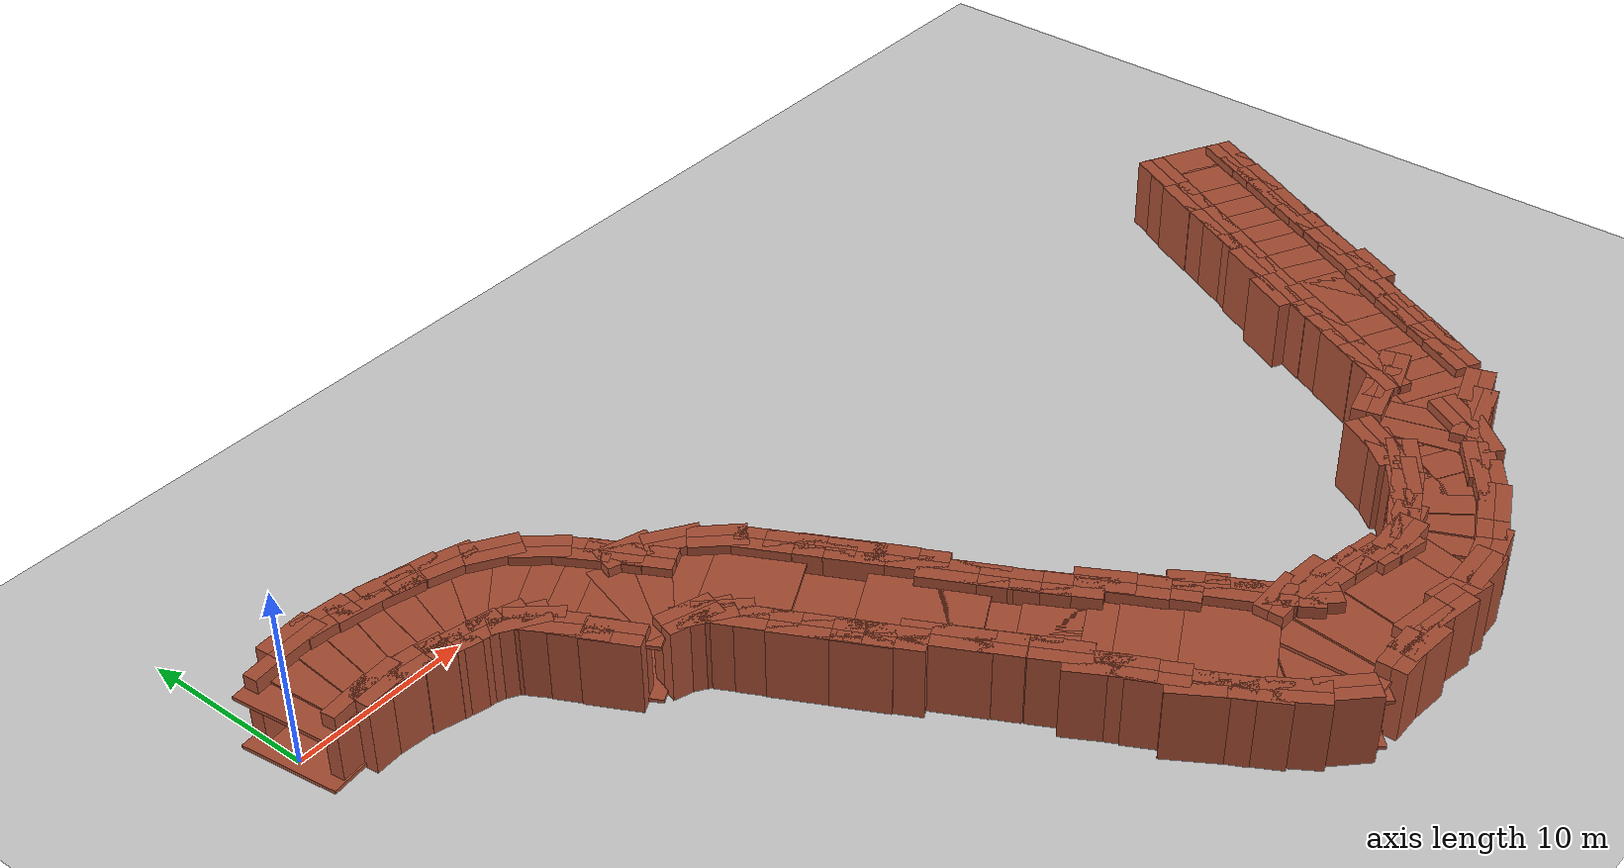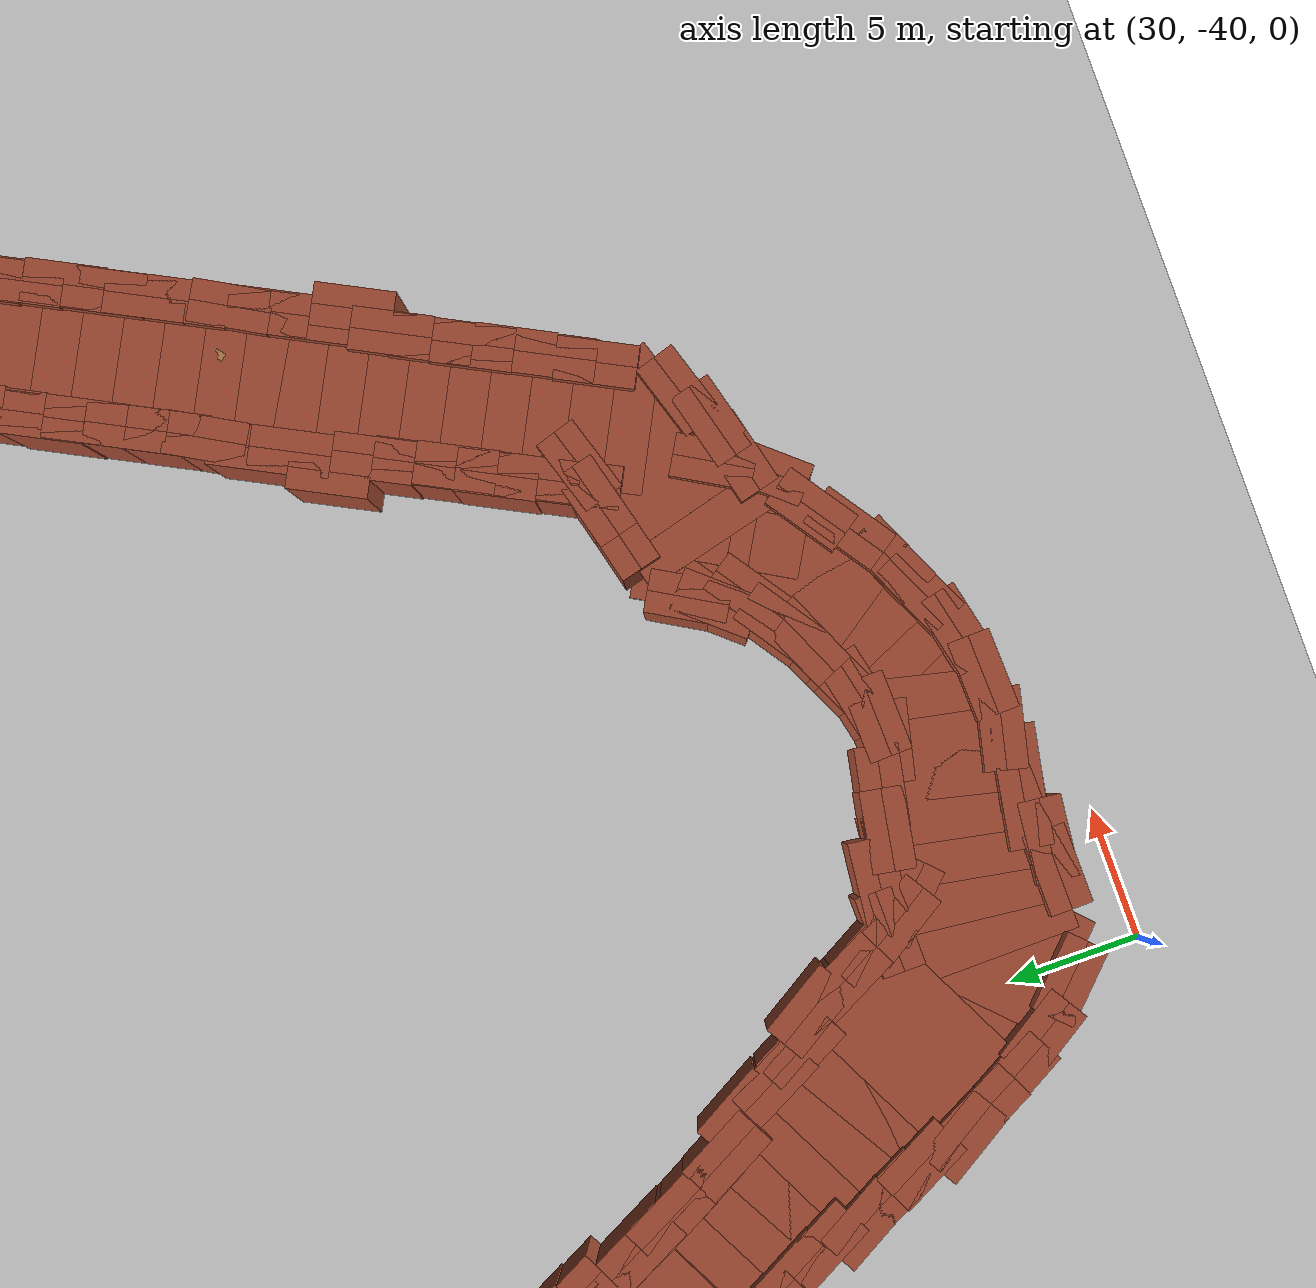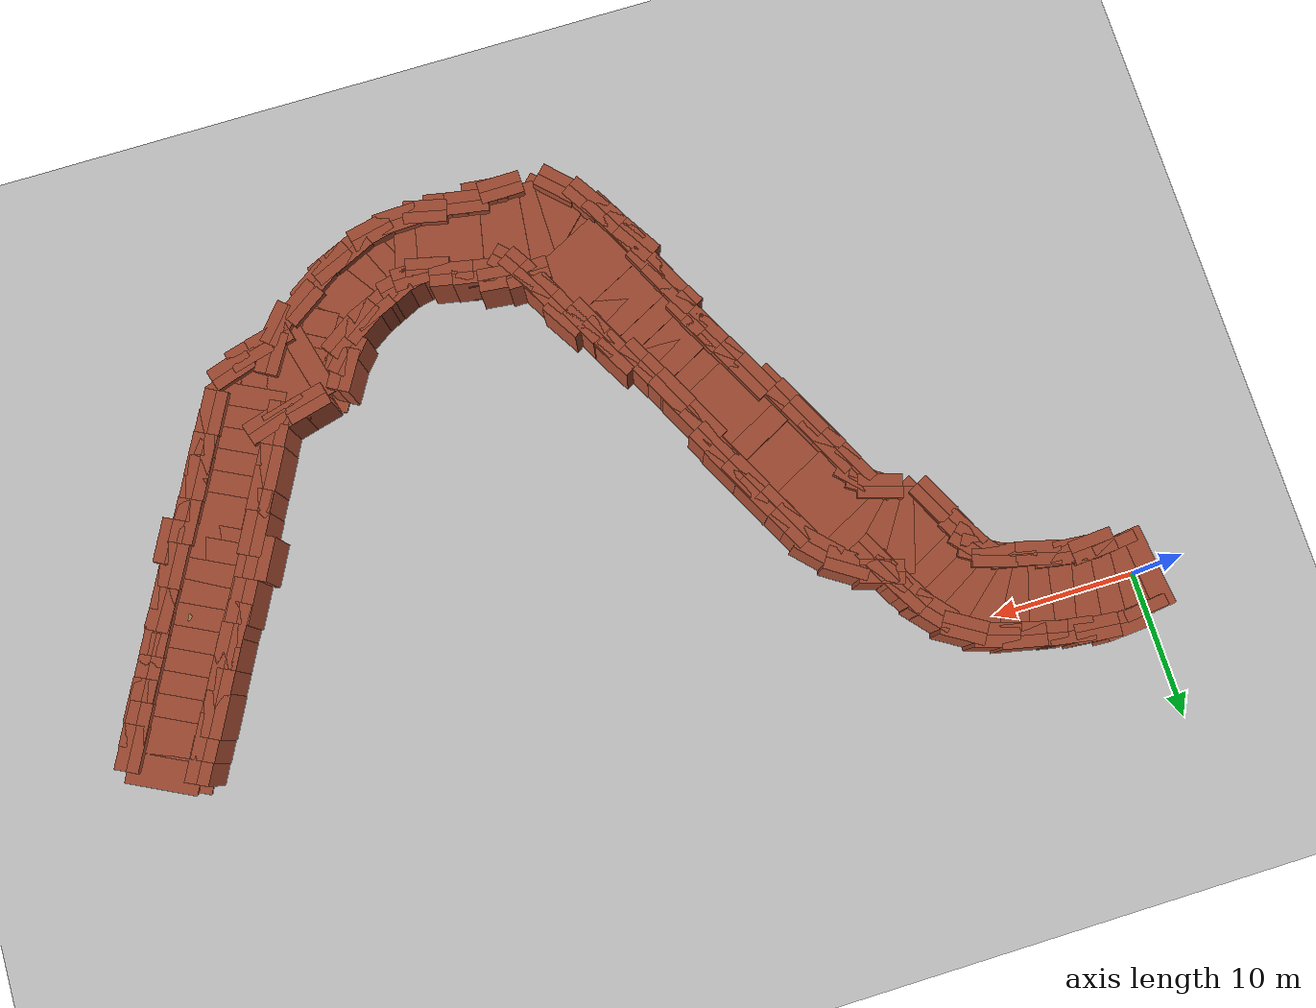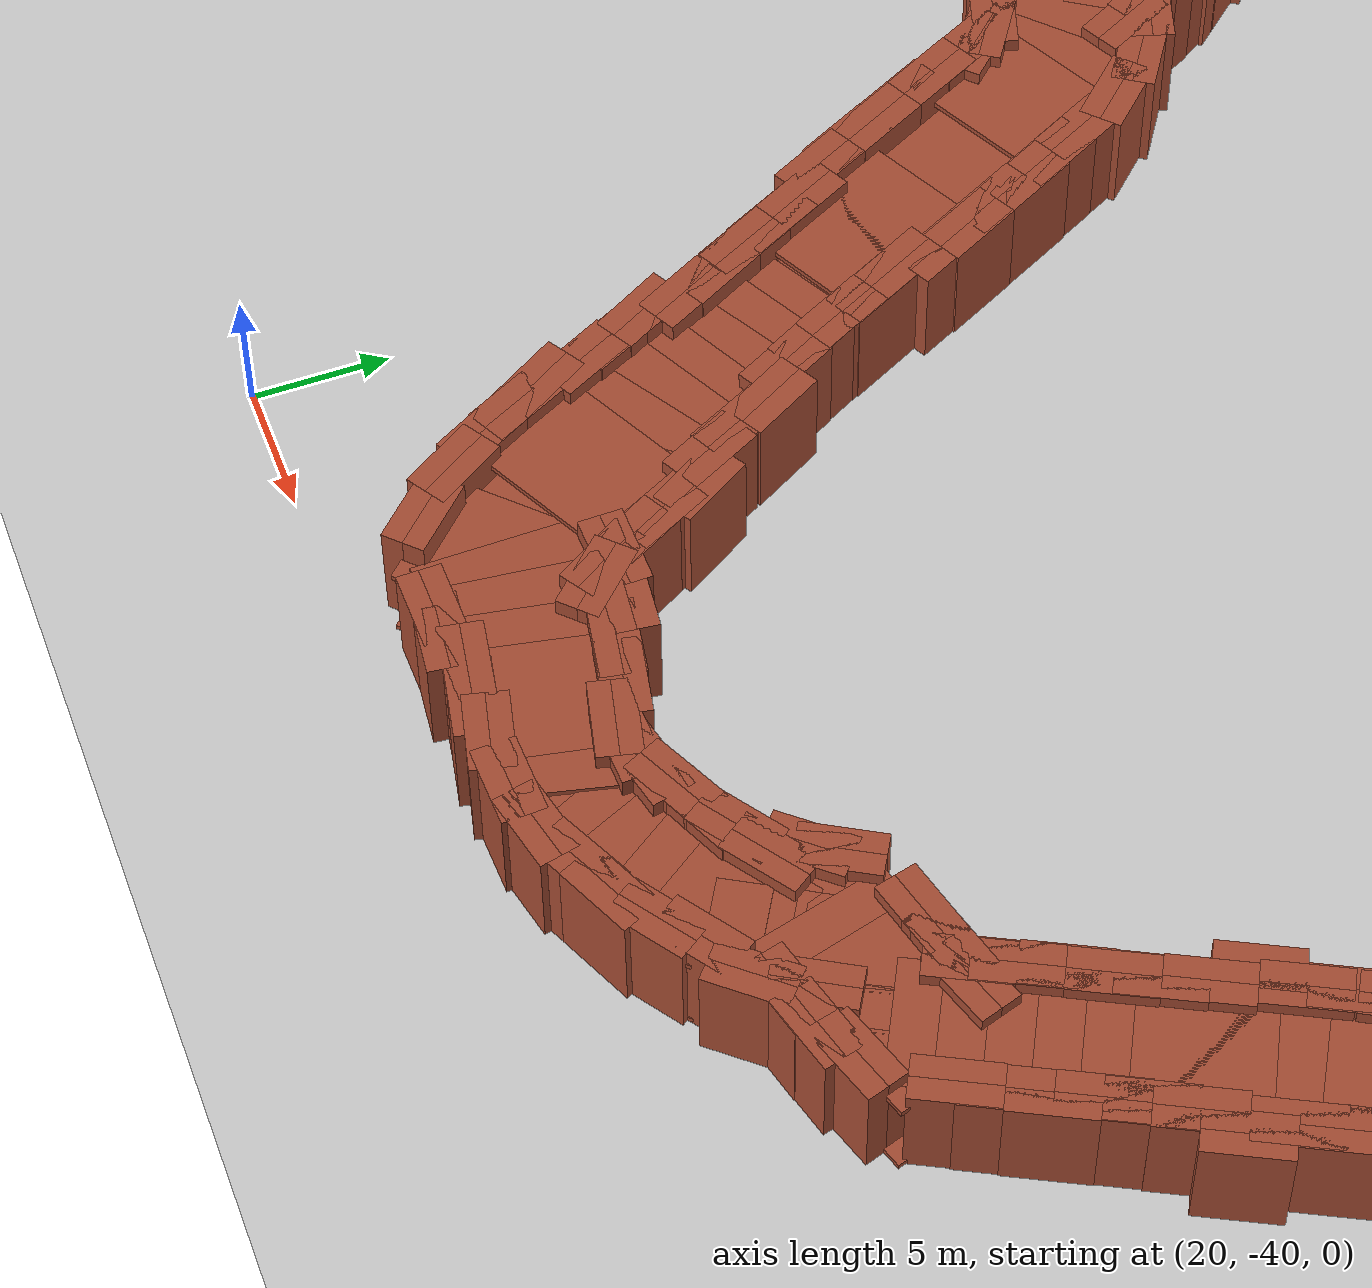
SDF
<?xml version="1.0" ?>
<sdf version="1.6">
  <world name="procedural_cave_world">
    <include><uri>model://sun</uri></include>
    <include><uri>model://ground_plane</uri></include>

    <!-- Gazebo ROS State Plugin (World level) -->
    <plugin name="gazebo_ros_state" filename="libgazebo_ros_state.so">
      <ros>
        <namespace>/gazebo</namespace>
      </ros>
      <update_rate>10.0</update_rate>
    </plugin>

    <physics type="ode">
      <real_time_update_rate>1000.0</real_time_update_rate>
      <max_step_size>0.001</max_step_size>
    </physics>
    <gui fullscreen='false'>
      <camera name='user_camera'>
        <pose>-6.0 0.0 4.0 0.0 0.5 0.0</pose>
        <view_controller>orbit</view_controller>
      </camera>
    </gui>
    <model name="procedural_cave">
      <static>true</static>

      <link name="left_wall_0">
        <pose>1.224523597467146 2.4564252081160305 1.5 0 0 0.11573853253283148</pose>
        <collision name="collision">
          <geometry><box><size>3.0 0.8 5.0</size></box></geometry>
        </collision>
        <visual name="visual">
          <geometry><box><size>3.0 0.8 5.0</size></box></geometry>
          <material><script><uri>file://media/materials/scripts/gazebo.material</uri><name>Gazebo/Bricks</name></script></material>
        </visual>
      </link>
      <link name="right_wall_0">
        <pose>1.7554057102699834 -2.109984273916111 1.5 0 0 0.11573853253283148</pose>
        <collision name="collision">
          <geometry><box><size>3.0 0.8 5.0</size></box></geometry>
        </collision>
        <visual name="visual">
          <geometry><box><size>3.0 0.8 5.0</size></box></geometry>
          <material><script><uri>file://media/materials/scripts/gazebo.material</uri><name>Gazebo/Bricks</name></script></material>
        </visual>
      </link>
      <link name="ceiling_0">
        <pose>1.4899646538685647 0.17322046709995959 3.1 0 0 0.11573853253283148</pose>
        <collision name="collision">
          <geometry><box><size>4.5 5.597165580581915 0.2</size></box></geometry>
        </collision>
        <visual name="visual">
          <geometry><box><size>4.5 5.597165580581915 0.2</size></box></geometry>
          <material><script><uri>file://media/materials/scripts/gazebo.material</uri><name>Gazebo/Bricks</name></script></material>
        </visual>
      </link>
      <link name="floor_0">
        <pose>1.4899646538685647 0.17322046709995959 0.1 0 0 0.11573853253283148</pose>
        <collision name="collision">
          <geometry><box><size>4.5 5.597165580581915 0.2</size></box></geometry>
        </collision>
        <visual name="visual">
          <geometry><box><size>4.5 5.597165580581915 0.2</size></box></geometry>
          <material><script><uri>file://media/materials/scripts/gazebo.material</uri><name>Gazebo/Bricks</name></script></material>
        </visual>
      </link>
      <link name="left_wall_1">
        <pose>2.8282510521473587 2.5573240663752075 1.5 0 0 0.06922987092913153</pose>
        <collision name="collision">
          <geometry><box><size>3.0 0.8 5.0</size></box></geometry>
        </collision>
        <visual name="visual">
          <geometry><box><size>3.0 0.8 5.0</size></box></geometry>
          <material><script><uri>file://media/materials/scripts/gazebo.material</uri><name>Gazebo/Bricks</name></script></material>
        </visual>
      </link>
      <link name="right_wall_1">
        <pose>3.144491963924351 -2.0033593812342985 1.5 0 0 0.06922987092913153</pose>
        <collision name="collision">
          <geometry><box><size>3.0 0.8 5.0</size></box></geometry>
        </collision>
        <visual name="visual">
          <geometry><box><size>3.0 0.8 5.0</size></box></geometry>
          <material><script><uri>file://media/materials/scripts/gazebo.material</uri><name>Gazebo/Bricks</name></script></material>
        </visual>
      </link>
      <link name="fill_left_1">
        <pose>2.7729113852297615 3.355407721931096 1.5 0 0 0.06922987092913153</pose>
        <collision name="collision">
          <geometry><box><size>3.0 0.8 5.0</size></box></geometry>
        </collision>
        <visual name="visual">
          <geometry><box><size>3.0 0.8 5.0</size></box></geometry>
          <material><script><uri>file://media/materials/scripts/gazebo.material</uri><name>Gazebo/Bricks</name></script></material>
        </visual>
      </link>
      <link name="fill_right_1">
        <pose>3.199831630841948 -2.801443036790187 1.5 0 0 0.06922987092913153</pose>
        <collision name="collision">
          <geometry><box><size>3.0 0.8 5.0</size></box></geometry>
        </collision>
        <visual name="visual">
          <geometry><box><size>3.0 0.8 5.0</size></box></geometry>
          <material><script><uri>file://media/materials/scripts/gazebo.material</uri><name>Gazebo/Bricks</name></script></material>
        </visual>
      </link>
      <link name="ceiling_1">
        <pose>2.986371508035855 0.27698234257045445 3.22 0 0 0.06922987092913153</pose>
        <collision name="collision">
          <geometry><box><size>4.5 5.5716344805311016 0.2</size></box></geometry>
        </collision>
        <visual name="visual">
          <geometry><box><size>4.5 5.5716344805311016 0.2</size></box></geometry>
          <material><script><uri>file://media/materials/scripts/gazebo.material</uri><name>Gazebo/Bricks</name></script></material>
        </visual>
      </link>
      <link name="floor_1">
        <pose>2.986371508035855 0.27698234257045445 0.1 0 0 0.06922987092913153</pose>
        <collision name="collision">
          <geometry><box><size>4.5 5.5716344805311016 0.2</size></box></geometry>
        </collision>
        <visual name="visual">
          <geometry><box><size>4.5 5.5716344805311016 0.2</size></box></geometry>
          <material><script><uri>file://media/materials/scripts/gazebo.material</uri><name>Gazebo/Bricks</name></script></material>
        </visual>
      </link>
      <link name="left_wall_2">
        <pose>4.67265879498337 2.382047039975188 1.5 0 0 -0.08566222407151684</pose>
        <collision name="collision">
          <geometry><box><size>3.0 0.8 5.0</size></box></geometry>
        </collision>
        <visual name="visual">
          <geometry><box><size>3.0 0.8 5.0</size></box></geometry>
          <material><script><uri>file://media/materials/scripts/gazebo.material</uri><name>Gazebo/Bricks</name></script></material>
        </visual>
      </link>
      <link name="right_wall_2">
        <pose>4.28908392530389 -2.0847548469314092 1.5 0 0 -0.08566222407151684</pose>
        <collision name="collision">
          <geometry><box><size>3.0 0.8 5.0</size></box></geometry>
        </collision>
        <visual name="visual">
          <geometry><box><size>3.0 0.8 5.0</size></box></geometry>
          <material><script><uri>file://media/materials/scripts/gazebo.material</uri><name>Gazebo/Bricks</name></script></material>
        </visual>
      </link>
      <link name="fill_left_2">
        <pose>4.741104792875937 3.179113627766001 1.5 0 0 -0.08566222407151684</pose>
        <collision name="collision">
          <geometry><box><size>3.0 0.8 5.0</size></box></geometry>
        </collision>
        <visual name="visual">
          <geometry><box><size>3.0 0.8 5.0</size></box></geometry>
          <material><script><uri>file://media/materials/scripts/gazebo.material</uri><name>Gazebo/Bricks</name></script></material>
        </visual>
      </link>
      <link name="fill_right_2">
        <pose>4.220637927411323 -2.881821434722222 1.5 0 0 -0.08566222407151684</pose>
        <collision name="collision">
          <geometry><box><size>3.0 0.8 5.0</size></box></geometry>
        </collision>
        <visual name="visual">
          <geometry><box><size>3.0 0.8 5.0</size></box></geometry>
          <material><script><uri>file://media/materials/scripts/gazebo.material</uri><name>Gazebo/Bricks</name></script></material>
        </visual>
      </link>
      <link name="ceiling_2">
        <pose>4.48087136014363 0.14864609652188923 3.2920000000000003 0 0 -0.08566222407151684</pose>
        <collision name="collision">
          <geometry><box><size>4.5 5.483240878819915 0.2</size></box></geometry>
        </collision>
        <visual name="visual">
          <geometry><box><size>4.5 5.483240878819915 0.2</size></box></geometry>
          <material><script><uri>file://media/materials/scripts/gazebo.material</uri><name>Gazebo/Bricks</name></script></material>
        </visual>
      </link>
      <link name="floor_2">
        <pose>4.48087136014363 0.14864609652188923 0.1 0 0 -0.08566222407151684</pose>
        <collision name="collision">
          <geometry><box><size>4.5 5.483240878819915 0.2</size></box></geometry>
        </collision>
        <visual name="visual">
          <geometry><box><size>4.5 5.483240878819915 0.2</size></box></geometry>
          <material><script><uri>file://media/materials/scripts/gazebo.material</uri><name>Gazebo/Bricks</name></script></material>
        </visual>
      </link>
      <link name="left_wall_3">
        <pose>6.301181151216998 2.0507735075568085 1.5 0 0 -0.15723699775955097</pose>
        <collision name="collision">
          <geometry><box><size>3.0 0.8 5.0</size></box></geometry>
        </collision>
        <visual name="visual">
          <geometry><box><size>3.0 0.8 5.0</size></box></geometry>
          <material><script><uri>file://media/materials/scripts/gazebo.material</uri><name>Gazebo/Bricks</name></script></material>
        </visual>
      </link>
      <link name="right_wall_3">
        <pose>5.623552702201307 -2.2232509867853176 1.5 0 0 -0.15723699775955097</pose>
        <collision name="collision">
          <geometry><box><size>3.0 0.8 5.0</size></box></geometry>
        </collision>
        <visual name="visual">
          <geometry><box><size>3.0 0.8 5.0</size></box></geometry>
          <material><script><uri>file://media/materials/scripts/gazebo.material</uri><name>Gazebo/Bricks</name></script></material>
        </visual>
      </link>
      <link name="fill_left_3">
        <pose>6.426453063822941 2.8409044763917537 1.5 0 0 -0.15723699775955097</pose>
        <collision name="collision">
          <geometry><box><size>3.0 0.8 5.0</size></box></geometry>
        </collision>
        <visual name="visual">
          <geometry><box><size>3.0 0.8 5.0</size></box></geometry>
          <material><script><uri>file://media/materials/scripts/gazebo.material</uri><name>Gazebo/Bricks</name></script></material>
        </visual>
      </link>
      <link name="fill_right_3">
        <pose>5.498280789595364 -3.013381955620263 1.5 0 0 -0.15723699775955097</pose>
        <collision name="collision">
          <geometry><box><size>3.0 0.8 5.0</size></box></geometry>
        </collision>
        <visual name="visual">
          <geometry><box><size>3.0 0.8 5.0</size></box></geometry>
          <material><script><uri>file://media/materials/scripts/gazebo.material</uri><name>Gazebo/Bricks</name></script></material>
        </visual>
      </link>
      <link name="ceiling_3">
        <pose>5.962366926709152 -0.08623873961425474 3.3352 0 0 -0.15723699775955097</pose>
        <collision name="collision">
          <geometry><box><size>4.5 5.3274086579790305 0.2</size></box></geometry>
        </collision>
        <visual name="visual">
          <geometry><box><size>4.5 5.3274086579790305 0.2</size></box></geometry>
          <material><script><uri>file://media/materials/scripts/gazebo.material</uri><name>Gazebo/Bricks</name></script></material>
        </visual>
      </link>
      <link name="floor_3">
        <pose>5.962366926709152 -0.08623873961425474 0.1 0 0 -0.15723699775955097</pose>
        <collision name="collision">
          <geometry><box><size>4.5 5.3274086579790305 0.2</size></box></geometry>
        </collision>
        <visual name="visual">
          <geometry><box><size>4.5 5.3274086579790305 0.2</size></box></geometry>
          <material><script><uri>file://media/materials/scripts/gazebo.material</uri><name>Gazebo/Bricks</name></script></material>
        </visual>
      </link>
      <link name="left_wall_4">
        <pose>7.972160272781874 1.7032153339422207 1.5 0 0 -0.25205845697423085</pose>
        <collision name="collision">
          <geometry><box><size>3.0 0.8 5.0</size></box></geometry>
        </collision>
        <visual name="visual">
          <geometry><box><size>3.0 0.8 5.0</size></box></geometry>
          <material><script><uri>file://media/materials/scripts/gazebo.material</uri><name>Gazebo/Bricks</name></script></material>
        </visual>
      </link>
      <link name="right_wall_4">
        <pose>6.857776877354214 -2.6238865078381783 1.5 0 0 -0.25205845697423085</pose>
        <collision name="collision">
          <geometry><box><size>3.0 0.8 5.0</size></box></geometry>
        </collision>
        <visual name="visual">
          <geometry><box><size>3.0 0.8 5.0</size></box></geometry>
          <material><script><uri>file://media/materials/scripts/gazebo.material</uri><name>Gazebo/Bricks</name></script></material>
        </visual>
      </link>
      <link name="fill_left_4">
        <pose>8.17167859135986 2.477936213066963 1.5 0 0 -0.25205845697423085</pose>
        <collision name="collision">
          <geometry><box><size>3.0 0.8 5.0</size></box></geometry>
        </collision>
        <visual name="visual">
          <geometry><box><size>3.0 0.8 5.0</size></box></geometry>
          <material><script><uri>file://media/materials/scripts/gazebo.material</uri><name>Gazebo/Bricks</name></script></material>
        </visual>
      </link>
      <link name="fill_right_4">
        <pose>6.658258558776227 -3.3986073869629205 1.5 0 0 -0.25205845697423085</pose>
        <collision name="collision">
          <geometry><box><size>3.0 0.8 5.0</size></box></geometry>
        </collision>
        <visual name="visual">
          <geometry><box><size>3.0 0.8 5.0</size></box></geometry>
          <material><script><uri>file://media/materials/scripts/gazebo.material</uri><name>Gazebo/Bricks</name></script></material>
        </visual>
      </link>
      <link name="ceiling_4">
        <pose>7.414968575068044 -0.46033558694797894 3.36112 0 0 -0.25205845697423085</pose>
        <collision name="collision">
          <geometry><box><size>4.5 5.468295055291694 0.2</size></box></geometry>
        </collision>
        <visual name="visual">
          <geometry><box><size>4.5 5.468295055291694 0.2</size></box></geometry>
          <material><script><uri>file://media/materials/scripts/gazebo.material</uri><name>Gazebo/Bricks</name></script></material>
        </visual>
      </link>
      <link name="floor_4">
        <pose>7.414968575068044 -0.46033558694797894 0.1 0 0 -0.25205845697423085</pose>
        <collision name="collision">
          <geometry><box><size>4.5 5.468295055291694 0.2</size></box></geometry>
        </collision>
        <visual name="visual">
          <geometry><box><size>4.5 5.468295055291694 0.2</size></box></geometry>
          <material><script><uri>file://media/materials/scripts/gazebo.material</uri><name>Gazebo/Bricks</name></script></material>
        </visual>
      </link>
      <link name="left_wall_5">
        <pose>9.345226092274107 1.4388276682660393 1.5 0 0 -0.2064345163576541</pose>
        <collision name="collision">
          <geometry><box><size>3.0 0.8 5.0</size></box></geometry>
        </collision>
        <visual name="visual">
          <geometry><box><size>3.0 0.8 5.0</size></box></geometry>
          <material><script><uri>file://media/materials/scripts/gazebo.material</uri><name>Gazebo/Bricks</name></script></material>
        </visual>
      </link>
      <link name="right_wall_5">
        <pose>8.42101492833704 -2.9744131290615416 1.5 0 0 -0.2064345163576541</pose>
        <collision name="collision">
          <geometry><box><size>3.0 0.8 5.0</size></box></geometry>
        </collision>
        <visual name="visual">
          <geometry><box><size>3.0 0.8 5.0</size></box></geometry>
          <material><script><uri>file://media/materials/scripts/gazebo.material</uri><name>Gazebo/Bricks</name></script></material>
        </visual>
      </link>
      <link name="fill_left_5">
        <pose>9.509203235447318 2.221842033726056 1.5 0 0 -0.2064345163576541</pose>
        <collision name="collision">
          <geometry><box><size>3.0 0.8 5.0</size></box></geometry>
        </collision>
        <visual name="visual">
          <geometry><box><size>3.0 0.8 5.0</size></box></geometry>
          <material><script><uri>file://media/materials/scripts/gazebo.material</uri><name>Gazebo/Bricks</name></script></material>
        </visual>
      </link>
      <link name="fill_right_5">
        <pose>8.25703778516383 -3.757427494521558 1.5 0 0 -0.2064345163576541</pose>
        <collision name="collision">
          <geometry><box><size>3.0 0.8 5.0</size></box></geometry>
        </collision>
        <visual name="visual">
          <geometry><box><size>3.0 0.8 5.0</size></box></geometry>
          <material><script><uri>file://media/materials/scripts/gazebo.material</uri><name>Gazebo/Bricks</name></script></material>
        </visual>
      </link>
      <link name="ceiling_5">
        <pose>8.883120510305574 -0.7677927303977511 3.3766719999999997 0 0 -0.2064345163576541</pose>
        <collision name="collision">
          <geometry><box><size>4.5 5.508975561116126 0.2</size></box></geometry>
        </collision>
        <visual name="visual">
          <geometry><box><size>4.5 5.508975561116126 0.2</size></box></geometry>
          <material><script><uri>file://media/materials/scripts/gazebo.material</uri><name>Gazebo/Bricks</name></script></material>
        </visual>
      </link>
      <link name="floor_5">
        <pose>8.883120510305574 -0.7677927303977511 0.1 0 0 -0.2064345163576541</pose>
        <collision name="collision">
          <geometry><box><size>4.5 5.508975561116126 0.2</size></box></geometry>
        </collision>
        <visual name="visual">
          <geometry><box><size>4.5 5.508975561116126 0.2</size></box></geometry>
          <material><script><uri>file://media/materials/scripts/gazebo.material</uri><name>Gazebo/Bricks</name></script></material>
        </visual>
      </link>
      <link name="left_wall_6">
        <pose>10.975940479146093 0.9026414170754393 1.5 0 0 -0.30257204073432453</pose>
        <collision name="collision">
          <geometry><box><size>3.0 0.8 5.0</size></box></geometry>
        </collision>
        <visual name="visual">
          <geometry><box><size>3.0 0.8 5.0</size></box></geometry>
          <material><script><uri>file://media/materials/scripts/gazebo.material</uri><name>Gazebo/Bricks</name></script></material>
        </visual>
      </link>
      <link name="right_wall_6">
        <pose>9.654020261442941 -3.3321560503503793 1.5 0 0 -0.30257204073432453</pose>
        <collision name="collision">
          <geometry><box><size>3.0 0.8 5.0</size></box></geometry>
        </collision>
        <visual name="visual">
          <geometry><box><size>3.0 0.8 5.0</size></box></geometry>
          <material><script><uri>file://media/materials/scripts/gazebo.material</uri><name>Gazebo/Bricks</name></script></material>
        </visual>
      </link>
      <link name="fill_left_6">
        <pose>11.214321591807277 1.6663000090695428 1.5 0 0 -0.30257204073432453</pose>
        <collision name="collision">
          <geometry><box><size>3.0 0.8 5.0</size></box></geometry>
        </collision>
        <visual name="visual">
          <geometry><box><size>3.0 0.8 5.0</size></box></geometry>
          <material><script><uri>file://media/materials/scripts/gazebo.material</uri><name>Gazebo/Bricks</name></script></material>
        </visual>
      </link>
      <link name="fill_right_6">
        <pose>9.415639148781757 -4.095814642344482 1.5 0 0 -0.30257204073432453</pose>
        <collision name="collision">
          <geometry><box><size>3.0 0.8 5.0</size></box></geometry>
        </collision>
        <visual name="visual">
          <geometry><box><size>3.0 0.8 5.0</size></box></geometry>
          <material><script><uri>file://media/materials/scripts/gazebo.material</uri><name>Gazebo/Bricks</name></script></material>
        </visual>
      </link>
      <link name="ceiling_6">
        <pose>10.314980370294517 -1.2147573166374699 3.3860031999999998 0 0 -0.30257204073432453</pose>
        <collision name="collision">
          <geometry><box><size>4.5 5.436325354624983 0.2</size></box></geometry>
        </collision>
        <visual name="visual">
          <geometry><box><size>4.5 5.436325354624983 0.2</size></box></geometry>
          <material><script><uri>file://media/materials/scripts/gazebo.material</uri><name>Gazebo/Bricks</name></script></material>
        </visual>
      </link>
      <link name="floor_6">
        <pose>10.314980370294517 -1.2147573166374699 0.1 0 0 -0.30257204073432453</pose>
        <collision name="collision">
          <geometry><box><size>4.5 5.436325354624983 0.2</size></box></geometry>
        </collision>
        <visual name="visual">
          <geometry><box><size>4.5 5.436325354624983 0.2</size></box></geometry>
          <material><script><uri>file://media/materials/scripts/gazebo.material</uri><name>Gazebo/Bricks</name></script></material>
        </visual>
      </link>
      <link name="left_wall_7">
        <pose>12.760485039966003 -0.1009287404537409 1.5 0 0 -0.5511974372785724</pose>
        <collision name="collision">
          <geometry><box><size>3.0 0.8 5.0</size></box></geometry>
        </collision>
        <visual name="visual">
          <geometry><box><size>3.0 0.8 5.0</size></box></geometry>
          <material><script><uri>file://media/materials/scripts/gazebo.material</uri><name>Gazebo/Bricks</name></script></material>
        </visual>
      </link>
      <link name="right_wall_7">
        <pose>10.42516977813547 -3.8997089886249157 1.5 0 0 -0.5511974372785724</pose>
        <collision name="collision">
          <geometry><box><size>3.0 0.8 5.0</size></box></geometry>
        </collision>
        <visual name="visual">
          <geometry><box><size>3.0 0.8 5.0</size></box></geometry>
          <material><script><uri>file://media/materials/scripts/gazebo.material</uri><name>Gazebo/Bricks</name></script></material>
        </visual>
      </link>
      <link name="fill_left_7">
        <pose>13.179451198846994 0.5805896802162422 1.5 0 0 -0.5511974372785724</pose>
        <collision name="collision">
          <geometry><box><size>3.0 0.8 5.0</size></box></geometry>
        </collision>
        <visual name="visual">
          <geometry><box><size>3.0 0.8 5.0</size></box></geometry>
          <material><script><uri>file://media/materials/scripts/gazebo.material</uri><name>Gazebo/Bricks</name></script></material>
        </visual>
      </link>
      <link name="fill_right_7">
        <pose>10.006203619254478 -4.581227409294899 1.5 0 0 -0.5511974372785724</pose>
        <collision name="collision">
          <geometry><box><size>3.0 0.8 5.0</size></box></geometry>
        </collision>
        <visual name="visual">
          <geometry><box><size>3.0 0.8 5.0</size></box></geometry>
          <material><script><uri>file://media/materials/scripts/gazebo.material</uri><name>Gazebo/Bricks</name></script></material>
        </visual>
      </link>
      <link name="ceiling_7">
        <pose>11.592827409050736 -2.000318864539328 3.39160192 0 0 -0.5511974372785724</pose>
        <collision name="collision">
          <geometry><box><size>4.5 5.459195975289051 0.2</size></box></geometry>
        </collision>
        <visual name="visual">
          <geometry><box><size>4.5 5.459195975289051 0.2</size></box></geometry>
          <material><script><uri>file://media/materials/scripts/gazebo.material</uri><name>Gazebo/Bricks</name></script></material>
        </visual>
      </link>
      <link name="floor_7">
        <pose>11.592827409050736 -2.000318864539328 0.1 0 0 -0.5511974372785724</pose>
        <collision name="collision">
          <geometry><box><size>4.5 5.459195975289051 0.2</size></box></geometry>
        </collision>
        <visual name="visual">
          <geometry><box><size>4.5 5.459195975289051 0.2</size></box></geometry>
          <material><script><uri>file://media/materials/scripts/gazebo.material</uri><name>Gazebo/Bricks</name></script></material>
        </visual>
      </link>
      <link name="left_wall_8">
        <pose>14.23462658148497 -1.6995367598341604 1.5 0 0 -0.858025921734783</pose>
        <collision name="collision">
          <geometry><box><size>3.0 0.8 5.0</size></box></geometry>
        </collision>
        <visual name="visual">
          <geometry><box><size>3.0 0.8 5.0</size></box></geometry>
          <material><script><uri>file://media/materials/scripts/gazebo.material</uri><name>Gazebo/Bricks</name></script></material>
        </visual>
      </link>
      <link name="right_wall_8">
        <pose>10.912824945981939 -4.570760342613756 1.5 0 0 -0.858025921734783</pose>
        <collision name="collision">
          <geometry><box><size>3.0 0.8 5.0</size></box></geometry>
        </collision>
        <visual name="visual">
          <geometry><box><size>3.0 0.8 5.0</size></box></geometry>
          <material><script><uri>file://media/materials/scripts/gazebo.material</uri><name>Gazebo/Bricks</name></script></material>
        </visual>
      </link>
      <link name="fill_left_8">
        <pose>14.839869081050107 -1.176390970670044 1.5 0 0 -0.858025921734783</pose>
        <collision name="collision">
          <geometry><box><size>3.0 0.8 5.0</size></box></geometry>
        </collision>
        <visual name="visual">
          <geometry><box><size>3.0 0.8 5.0</size></box></geometry>
          <material><script><uri>file://media/materials/scripts/gazebo.material</uri><name>Gazebo/Bricks</name></script></material>
        </visual>
      </link>
      <link name="fill_right_8">
        <pose>10.307582446416802 -5.093906131777873 1.5 0 0 -0.858025921734783</pose>
        <collision name="collision">
          <geometry><box><size>3.0 0.8 5.0</size></box></geometry>
        </collision>
        <visual name="visual">
          <geometry><box><size>3.0 0.8 5.0</size></box></geometry>
          <material><script><uri>file://media/materials/scripts/gazebo.material</uri><name>Gazebo/Bricks</name></script></material>
        </visual>
      </link>
      <link name="ceiling_8">
        <pose>12.573725763733455 -3.135148551223958 3.394961152 0 0 -0.858025921734783</pose>
        <collision name="collision">
          <geometry><box><size>4.5 5.3907050650140835 0.2</size></box></geometry>
        </collision>
        <visual name="visual">
          <geometry><box><size>4.5 5.3907050650140835 0.2</size></box></geometry>
          <material><script><uri>file://media/materials/scripts/gazebo.material</uri><name>Gazebo/Bricks</name></script></material>
        </visual>
      </link>
      <link name="floor_8">
        <pose>12.573725763733455 -3.135148551223958 0.1 0 0 -0.858025921734783</pose>
        <collision name="collision">
          <geometry><box><size>4.5 5.3907050650140835 0.2</size></box></geometry>
        </collision>
        <visual name="visual">
          <geometry><box><size>4.5 5.3907050650140835 0.2</size></box></geometry>
          <material><script><uri>file://media/materials/scripts/gazebo.material</uri><name>Gazebo/Bricks</name></script></material>
        </visual>
      </link>
      <link name="left_wall_9">
        <pose>15.289900548992929 -3.307481750077197 1.5 0 0 -1.0504297247273167</pose>
        <collision name="collision">
          <geometry><box><size>3.0 0.8 5.0</size></box></geometry>
        </collision>
        <visual name="visual">
          <geometry><box><size>3.0 0.8 5.0</size></box></geometry>
          <material><script><uri>file://media/materials/scripts/gazebo.material</uri><name>Gazebo/Bricks</name></script></material>
        </visual>
      </link>
      <link name="right_wall_9">
        <pose>11.349145724731624 -5.5657262446097535 1.5 0 0 -1.0504297247273167</pose>
        <collision name="collision">
          <geometry><box><size>3.0 0.8 5.0</size></box></geometry>
        </collision>
        <visual name="visual">
          <geometry><box><size>3.0 0.8 5.0</size></box></geometry>
          <material><script><uri>file://media/materials/scripts/gazebo.material</uri><name>Gazebo/Bricks</name></script></material>
        </visual>
      </link>
      <link name="fill_left_9">
        <pose>15.984010120256672 -2.909723151075159 1.5 0 0 -1.0504297247273167</pose>
        <collision name="collision">
          <geometry><box><size>3.0 0.8 5.0</size></box></geometry>
        </collision>
        <visual name="visual">
          <geometry><box><size>3.0 0.8 5.0</size></box></geometry>
          <material><script><uri>file://media/materials/scripts/gazebo.material</uri><name>Gazebo/Bricks</name></script></material>
        </visual>
      </link>
      <link name="fill_right_9">
        <pose>10.655036153467881 -5.963484843611791 1.5 0 0 -1.0504297247273167</pose>
        <collision name="collision">
          <geometry><box><size>3.0 0.8 5.0</size></box></geometry>
        </collision>
        <visual name="visual">
          <geometry><box><size>3.0 0.8 5.0</size></box></geometry>
          <material><script><uri>file://media/materials/scripts/gazebo.material</uri><name>Gazebo/Bricks</name></script></material>
        </visual>
      </link>
      <link name="ceiling_9">
        <pose>13.319523136862276 -4.436603997343475 3.3969766912000003 0 0 -1.0504297247273167</pose>
        <collision name="collision">
          <geometry><box><size>4.5 5.541939759841092 0.2</size></box></geometry>
        </collision>
        <visual name="visual">
          <geometry><box><size>4.5 5.541939759841092 0.2</size></box></geometry>
          <material><script><uri>file://media/materials/scripts/gazebo.material</uri><name>Gazebo/Bricks</name></script></material>
        </visual>
      </link>
      <link name="floor_9">
        <pose>13.319523136862276 -4.436603997343475 0.1 0 0 -1.0504297247273167</pose>
        <collision name="collision">
          <geometry><box><size>4.5 5.541939759841092 0.2</size></box></geometry>
        </collision>
        <visual name="visual">
          <geometry><box><size>4.5 5.541939759841092 0.2</size></box></geometry>
          <material><script><uri>file://media/materials/scripts/gazebo.material</uri><name>Gazebo/Bricks</name></script></material>
        </visual>
      </link>
      <link name="left_wall_10">
        <pose>16.071593146358804 -4.718998116915573 1.5 0 0 -1.1</pose>
        <collision name="collision">
          <geometry><box><size>3.0 0.8 5.0</size></box></geometry>
        </collision>
        <visual name="visual">
          <geometry><box><size>3.0 0.8 5.0</size></box></geometry>
          <material><script><uri>file://media/materials/scripts/gazebo.material</uri><name>Gazebo/Bricks</name></script></material>
        </visual>
      </link>
      <link name="right_wall_10">
        <pose>11.92824149164248 -6.8278319579556825 1.5 0 0 -1.1</pose>
        <collision name="collision">
          <geometry><box><size>3.0 0.8 5.0</size></box></geometry>
        </collision>
        <visual name="visual">
          <geometry><box><size>3.0 0.8 5.0</size></box></geometry>
          <material><script><uri>file://media/materials/scripts/gazebo.material</uri><name>Gazebo/Bricks</name></script></material>
        </visual>
      </link>
      <link name="fill_left_10">
        <pose>16.784559034407955 -4.356121219775111 1.5 0 0 -1.1</pose>
        <collision name="collision">
          <geometry><box><size>3.0 0.8 5.0</size></box></geometry>
        </collision>
        <visual name="visual">
          <geometry><box><size>3.0 0.8 5.0</size></box></geometry>
          <material><script><uri>file://media/materials/scripts/gazebo.material</uri><name>Gazebo/Bricks</name></script></material>
        </visual>
      </link>
      <link name="fill_right_10">
        <pose>11.215275603593332 -7.190708855096145 1.5 0 0 -1.1</pose>
        <collision name="collision">
          <geometry><box><size>3.0 0.8 5.0</size></box></geometry>
        </collision>
        <visual name="visual">
          <geometry><box><size>3.0 0.8 5.0</size></box></geometry>
          <material><script><uri>file://media/materials/scripts/gazebo.material</uri><name>Gazebo/Bricks</name></script></material>
        </visual>
      </link>
      <link name="ceiling_10">
        <pose>13.999917319000643 -5.773415037435628 3.39818601472 0 0 -1.1</pose>
        <collision name="collision">
          <geometry><box><size>4.5 5.649144341032713 0.2</size></box></geometry>
        </collision>
        <visual name="visual">
          <geometry><box><size>4.5 5.649144341032713 0.2</size></box></geometry>
          <material><script><uri>file://media/materials/scripts/gazebo.material</uri><name>Gazebo/Bricks</name></script></material>
        </visual>
      </link>
      <link name="floor_10">
        <pose>13.999917319000643 -5.773415037435628 0.1 0 0 -1.1</pose>
        <collision name="collision">
          <geometry><box><size>4.5 5.649144341032713 0.2</size></box></geometry>
        </collision>
        <visual name="visual">
          <geometry><box><size>4.5 5.649144341032713 0.2</size></box></geometry>
          <material><script><uri>file://media/materials/scripts/gazebo.material</uri><name>Gazebo/Bricks</name></script></material>
        </visual>
      </link>
      <link name="left_wall_11">
        <pose>16.80622322821062 -6.028204813894637 1.5 0 0 -1.1</pose>
        <collision name="collision">
          <geometry><box><size>3.0 0.8 5.0</size></box></geometry>
        </collision>
        <visual name="visual">
          <geometry><box><size>3.0 0.8 5.0</size></box></geometry>
          <material><script><uri>file://media/materials/scripts/gazebo.material</uri><name>Gazebo/Bricks</name></script></material>
        </visual>
      </link>
      <link name="right_wall_11">
        <pose>12.554399774067399 -8.192247341160924 1.5 0 0 -1.1</pose>
        <collision name="collision">
          <geometry><box><size>3.0 0.8 5.0</size></box></geometry>
        </collision>
        <visual name="visual">
          <geometry><box><size>3.0 0.8 5.0</size></box></geometry>
          <material><script><uri>file://media/materials/scripts/gazebo.material</uri><name>Gazebo/Bricks</name></script></material>
        </visual>
      </link>
      <link name="fill_left_11">
        <pose>17.519189116259767 -5.665327916754175 1.5 0 0 -1.1</pose>
        <collision name="collision">
          <geometry><box><size>3.0 0.8 5.0</size></box></geometry>
        </collision>
        <visual name="visual">
          <geometry><box><size>3.0 0.8 5.0</size></box></geometry>
          <material><script><uri>file://media/materials/scripts/gazebo.material</uri><name>Gazebo/Bricks</name></script></material>
        </visual>
      </link>
      <link name="fill_right_11">
        <pose>11.841433886018251 -8.555124238301387 1.5 0 0 -1.1</pose>
        <collision name="collision">
          <geometry><box><size>3.0 0.8 5.0</size></box></geometry>
        </collision>
        <visual name="visual">
          <geometry><box><size>3.0 0.8 5.0</size></box></geometry>
          <material><script><uri>file://media/materials/scripts/gazebo.material</uri><name>Gazebo/Bricks</name></script></material>
        </visual>
      </link>
      <link name="ceiling_11">
        <pose>14.680311501139009 -7.110226077527781 3.3989116088319995 0 0 -1.1</pose>
        <collision name="collision">
          <geometry><box><size>4.5 5.770857652982263 0.2</size></box></geometry>
        </collision>
        <visual name="visual">
          <geometry><box><size>4.5 5.770857652982263 0.2</size></box></geometry>
          <material><script><uri>file://media/materials/scripts/gazebo.material</uri><name>Gazebo/Bricks</name></script></material>
        </visual>
      </link>
      <link name="floor_11">
        <pose>14.680311501139009 -7.110226077527781 0.1 0 0 -1.1</pose>
        <collision name="collision">
          <geometry><box><size>4.5 5.770857652982263 0.2</size></box></geometry>
        </collision>
        <visual name="visual">
          <geometry><box><size>4.5 5.770857652982263 0.2</size></box></geometry>
          <material><script><uri>file://media/materials/scripts/gazebo.material</uri><name>Gazebo/Bricks</name></script></material>
        </visual>
      </link>
      <link name="left_wall_12">
        <pose>16.83460122444862 -5.221788101895491 1.5 0 0 -0.30000000000000004</pose>
        <collision name="collision">
          <geometry><box><size>3.0 0.8 5.0</size></box></geometry>
        </collision>
        <visual name="visual">
          <geometry><box><size>3.0 0.8 5.0</size></box></geometry>
          <material><script><uri>file://media/materials/scripts/gazebo.material</uri><name>Gazebo/Bricks</name></script></material>
        </visual>
      </link>
      <link name="right_wall_12">
        <pose>15.39203124520622 -9.885224673144089 1.5 0 0 -0.30000000000000004</pose>
        <collision name="collision">
          <geometry><box><size>3.0 0.8 5.0</size></box></geometry>
        </collision>
        <visual name="visual">
          <geometry><box><size>3.0 0.8 5.0</size></box></geometry>
          <material><script><uri>file://media/materials/scripts/gazebo.material</uri><name>Gazebo/Bricks</name></script></material>
        </visual>
      </link>
      <link name="fill_left_12">
        <pose>17.07101738977769 -4.457518910595008 1.5 0 0 -0.30000000000000004</pose>
        <collision name="collision">
          <geometry><box><size>3.0 0.8 5.0</size></box></geometry>
        </collision>
        <visual name="visual">
          <geometry><box><size>3.0 0.8 5.0</size></box></geometry>
          <material><script><uri>file://media/materials/scripts/gazebo.material</uri><name>Gazebo/Bricks</name></script></material>
        </visual>
      </link>
      <link name="fill_right_12">
        <pose>15.155615079877146 -10.649493864444572 1.5 0 0 -0.30000000000000004</pose>
        <collision name="collision">
          <geometry><box><size>3.0 0.8 5.0</size></box></geometry>
        </collision>
        <visual name="visual">
          <geometry><box><size>3.0 0.8 5.0</size></box></geometry>
          <material><script><uri>file://media/materials/scripts/gazebo.material</uri><name>Gazebo/Bricks</name></script></material>
        </visual>
      </link>
      <link name="ceiling_12">
        <pose>16.11331623482742 -7.55350638751979 3.3993469652991997 0 0 -0.30000000000000004</pose>
        <collision name="collision">
          <geometry><box><size>4.5 5.881459699625747 0.2</size></box></geometry>
        </collision>
        <visual name="visual">
          <geometry><box><size>4.5 5.881459699625747 0.2</size></box></geometry>
          <material><script><uri>file://media/materials/scripts/gazebo.material</uri><name>Gazebo/Bricks</name></script></material>
        </visual>
      </link>
      <link name="floor_12">
        <pose>16.11331623482742 -7.55350638751979 0.1 0 0 -0.30000000000000004</pose>
        <collision name="collision">
          <geometry><box><size>4.5 5.881459699625747 0.2</size></box></geometry>
        </collision>
        <visual name="visual">
          <geometry><box><size>4.5 5.881459699625747 0.2</size></box></geometry>
          <material><script><uri>file://media/materials/scripts/gazebo.material</uri><name>Gazebo/Bricks</name></script></material>
        </visual>
      </link>
      <link name="obs_stone_12">
        <pose>16.11331623482742 -9.206904686108583 2.309884093677302 0 0 1.8203498281922732</pose>
        <collision name="collision">
          <geometry><box><size>0.3128656533789459 0.4193718879768795 2.378925743243795</size></box></geometry>
        </collision>
        <visual name="visual">
          <geometry><box><size>0.44880358449901336 0.3698835056550585 2.378925743243795</size></box></geometry>
          <material><script><uri>file://media/materials/scripts/gazebo.material</uri><name>Gazebo/Wood</name></script></material>
        </visual>
      </link>
      <link name="left_wall_13">
        <pose>18.692086865937224 -6.3543426534960155 1.5 0 0 -0.5799482193392328</pose>
        <collision name="collision">
          <geometry><box><size>3.0 0.8 5.0</size></box></geometry>
        </collision>
        <visual name="visual">
          <geometry><box><size>3.0 0.8 5.0</size></box></geometry>
          <material><script><uri>file://media/materials/scripts/gazebo.material</uri><name>Gazebo/Bricks</name></script></material>
        </visual>
      </link>
      <link name="right_wall_13">
        <pose>16.044018681223694 -10.396611991949012 1.5 0 0 -0.5799482193392328</pose>
        <collision name="collision">
          <geometry><box><size>3.0 0.8 5.0</size></box></geometry>
        </collision>
        <visual name="visual">
          <geometry><box><size>3.0 0.8 5.0</size></box></geometry>
          <material><script><uri>file://media/materials/scripts/gazebo.material</uri><name>Gazebo/Bricks</name></script></material>
        </visual>
      </link>
      <link name="fill_left_13">
        <pose>19.130471364712008 -5.685149832827728 1.5 0 0 -0.5799482193392328</pose>
        <collision name="collision">
          <geometry><box><size>3.0 0.8 5.0</size></box></geometry>
        </collision>
        <visual name="visual">
          <geometry><box><size>3.0 0.8 5.0</size></box></geometry>
          <material><script><uri>file://media/materials/scripts/gazebo.material</uri><name>Gazebo/Bricks</name></script></material>
        </visual>
      </link>
      <link name="fill_right_13">
        <pose>15.605634182448908 -11.0658048126173 1.5 0 0 -0.5799482193392328</pose>
        <collision name="collision">
          <geometry><box><size>3.0 0.8 5.0</size></box></geometry>
        </collision>
        <visual name="visual">
          <geometry><box><size>3.0 0.8 5.0</size></box></geometry>
          <material><script><uri>file://media/materials/scripts/gazebo.material</uri><name>Gazebo/Bricks</name></script></material>
        </visual>
      </link>
      <link name="ceiling_13">
        <pose>17.36805277358046 -8.375477322722514 3.3996081791795194 0 0 -0.5799482193392328</pose>
        <collision name="collision">
          <geometry><box><size>4.5 5.832412080471743 0.2</size></box></geometry>
        </collision>
        <visual name="visual">
          <geometry><box><size>4.5 5.832412080471743 0.2</size></box></geometry>
          <material><script><uri>file://media/materials/scripts/gazebo.material</uri><name>Gazebo/Bricks</name></script></material>
        </visual>
      </link>
      <link name="floor_13">
        <pose>17.36805277358046 -8.375477322722514 0.1 0 0 -0.5799482193392328</pose>
        <collision name="collision">
          <geometry><box><size>4.5 5.832412080471743 0.2</size></box></geometry>
        </collision>
        <visual name="visual">
          <geometry><box><size>4.5 5.832412080471743 0.2</size></box></geometry>
          <material><script><uri>file://media/materials/scripts/gazebo.material</uri><name>Gazebo/Bricks</name></script></material>
        </visual>
      </link>
      <link name="left_wall_14">
        <pose>20.116610353974398 -7.824920602855085 1.5 0 0 -0.8084657183683084</pose>
        <collision name="collision">
          <geometry><box><size>3.0 0.8 5.0</size></box></geometry>
        </collision>
        <visual name="visual">
          <geometry><box><size>3.0 0.8 5.0</size></box></geometry>
          <material><script><uri>file://media/materials/scripts/gazebo.material</uri><name>Gazebo/Bricks</name></script></material>
        </visual>
      </link>
      <link name="right_wall_14">
        <pose>16.69132183761761 -11.09571935512386 1.5 0 0 -0.8084657183683084</pose>
        <collision name="collision">
          <geometry><box><size>3.0 0.8 5.0</size></box></geometry>
        </collision>
        <visual name="visual">
          <geometry><box><size>3.0 0.8 5.0</size></box></geometry>
          <material><script><uri>file://media/materials/scripts/gazebo.material</uri><name>Gazebo/Bricks</name></script></material>
        </visual>
      </link>
      <link name="fill_left_14">
        <pose>20.695193103983442 -7.272433497673461 1.5 0 0 -0.8084657183683084</pose>
        <collision name="collision">
          <geometry><box><size>3.0 0.8 5.0</size></box></geometry>
        </collision>
        <visual name="visual">
          <geometry><box><size>3.0 0.8 5.0</size></box></geometry>
          <material><script><uri>file://media/materials/scripts/gazebo.material</uri><name>Gazebo/Bricks</name></script></material>
        </visual>
      </link>
      <link name="fill_right_14">
        <pose>16.112739087608567 -11.648206460305484 1.5 0 0 -0.8084657183683084</pose>
        <collision name="collision">
          <geometry><box><size>3.0 0.8 5.0</size></box></geometry>
        </collision>
        <visual name="visual">
          <geometry><box><size>3.0 0.8 5.0</size></box></geometry>
          <material><script><uri>file://media/materials/scripts/gazebo.material</uri><name>Gazebo/Bricks</name></script></material>
        </visual>
      </link>
      <link name="ceiling_14">
        <pose>18.403966095796005 -9.460319978989473 3.3997649075077114 0 0 -0.8084657183683084</pose>
        <collision name="collision">
          <geometry><box><size>4.5 5.736108729550944 0.2</size></box></geometry>
        </collision>
        <visual name="visual">
          <geometry><box><size>4.5 5.736108729550944 0.2</size></box></geometry>
          <material><script><uri>file://media/materials/scripts/gazebo.material</uri><name>Gazebo/Bricks</name></script></material>
        </visual>
      </link>
      <link name="floor_14">
        <pose>18.403966095796005 -9.460319978989473 0.1 0 0 -0.8084657183683084</pose>
        <collision name="collision">
          <geometry><box><size>4.5 5.736108729550944 0.2</size></box></geometry>
        </collision>
        <visual name="visual">
          <geometry><box><size>4.5 5.736108729550944 0.2</size></box></geometry>
          <material><script><uri>file://media/materials/scripts/gazebo.material</uri><name>Gazebo/Bricks</name></script></material>
        </visual>
      </link>
      <link name="left_wall_15">
        <pose>21.229944795965153 -9.705096932309226 1.5 0 0 -1.1</pose>
        <collision name="collision">
          <geometry><box><size>3.0 0.8 5.0</size></box></geometry>
        </collision>
        <visual name="visual">
          <geometry><box><size>3.0 0.8 5.0</size></box></geometry>
          <material><script><uri>file://media/materials/scripts/gazebo.material</uri><name>Gazebo/Bricks</name></script></material>
        </visual>
      </link>
      <link name="right_wall_15">
        <pose>16.938775759903585 -11.889165105854024 1.5 0 0 -1.1</pose>
        <collision name="collision">
          <geometry><box><size>3.0 0.8 5.0</size></box></geometry>
        </collision>
        <visual name="visual">
          <geometry><box><size>3.0 0.8 5.0</size></box></geometry>
          <material><script><uri>file://media/materials/scripts/gazebo.material</uri><name>Gazebo/Bricks</name></script></material>
        </visual>
      </link>
      <link name="fill_left_15">
        <pose>21.9429106840143 -9.342220035168765 1.5 0 0 -1.1</pose>
        <collision name="collision">
          <geometry><box><size>3.0 0.8 5.0</size></box></geometry>
        </collision>
        <visual name="visual">
          <geometry><box><size>3.0 0.8 5.0</size></box></geometry>
          <material><script><uri>file://media/materials/scripts/gazebo.material</uri><name>Gazebo/Bricks</name></script></material>
        </visual>
      </link>
      <link name="fill_right_15">
        <pose>16.225809871854437 -12.252042002994486 1.5 0 0 -1.1</pose>
        <collision name="collision">
          <geometry><box><size>3.0 0.8 5.0</size></box></geometry>
        </collision>
        <visual name="visual">
          <geometry><box><size>3.0 0.8 5.0</size></box></geometry>
          <material><script><uri>file://media/materials/scripts/gazebo.material</uri><name>Gazebo/Bricks</name></script></material>
        </visual>
      </link>
      <link name="ceiling_15">
        <pose>19.08436027793437 -10.797131019081625 3.399858944504627 0 0 -1.1</pose>
        <collision name="collision">
          <geometry><box><size>4.5 5.815006280654769 0.2</size></box></geometry>
        </collision>
        <visual name="visual">
          <geometry><box><size>4.5 5.815006280654769 0.2</size></box></geometry>
          <material><script><uri>file://media/materials/scripts/gazebo.material</uri><name>Gazebo/Bricks</name></script></material>
        </visual>
      </link>
      <link name="floor_15">
        <pose>19.08436027793437 -10.797131019081625 0.1 0 0 -1.1</pose>
        <collision name="collision">
          <geometry><box><size>4.5 5.815006280654769 0.2</size></box></geometry>
        </collision>
        <visual name="visual">
          <geometry><box><size>4.5 5.815006280654769 0.2</size></box></geometry>
          <material><script><uri>file://media/materials/scripts/gazebo.material</uri><name>Gazebo/Bricks</name></script></material>
        </visual>
      </link>
      <link name="left_wall_16">
        <pose>21.924622003105284 -11.034638368229148 1.5 0 0 -1.1</pose>
        <collision name="collision">
          <geometry><box><size>3.0 0.8 5.0</size></box></geometry>
        </collision>
        <visual name="visual">
          <geometry><box><size>3.0 0.8 5.0</size></box></geometry>
          <material><script><uri>file://media/materials/scripts/gazebo.material</uri><name>Gazebo/Bricks</name></script></material>
        </visual>
      </link>
      <link name="right_wall_16">
        <pose>17.604886917040183 -13.233245750118408 1.5 0 0 -1.1</pose>
        <collision name="collision">
          <geometry><box><size>3.0 0.8 5.0</size></box></geometry>
        </collision>
        <visual name="visual">
          <geometry><box><size>3.0 0.8 5.0</size></box></geometry>
          <material><script><uri>file://media/materials/scripts/gazebo.material</uri><name>Gazebo/Bricks</name></script></material>
        </visual>
      </link>
      <link name="fill_left_16">
        <pose>22.637587891154432 -10.671761471088686 1.5 0 0 -1.1</pose>
        <collision name="collision">
          <geometry><box><size>3.0 0.8 5.0</size></box></geometry>
        </collision>
        <visual name="visual">
          <geometry><box><size>3.0 0.8 5.0</size></box></geometry>
          <material><script><uri>file://media/materials/scripts/gazebo.material</uri><name>Gazebo/Bricks</name></script></material>
        </visual>
      </link>
      <link name="fill_right_16">
        <pose>16.891921028991035 -13.59612264725887 1.5 0 0 -1.1</pose>
        <collision name="collision">
          <geometry><box><size>3.0 0.8 5.0</size></box></geometry>
        </collision>
        <visual name="visual">
          <geometry><box><size>3.0 0.8 5.0</size></box></geometry>
          <material><script><uri>file://media/materials/scripts/gazebo.material</uri><name>Gazebo/Bricks</name></script></material>
        </visual>
      </link>
      <link name="ceiling_16">
        <pose>19.764754460072734 -12.133942059173778 2.3920610211163402 0 0 -1.1</pose>
        <collision name="collision">
          <geometry><box><size>4.5 5.847059483179449 0.2</size></box></geometry>
        </collision>
        <visual name="visual">
          <geometry><box><size>4.5 5.847059483179449 0.2</size></box></geometry>
          <material><script><uri>file://media/materials/scripts/gazebo.material</uri><name>Gazebo/Bricks</name></script></material>
        </visual>
      </link>
      <link name="floor_16">
        <pose>19.764754460072734 -12.133942059173778 0.1 0 0 -1.1</pose>
        <collision name="collision">
          <geometry><box><size>4.5 5.847059483179449 0.2</size></box></geometry>
        </collision>
        <visual name="visual">
          <geometry><box><size>4.5 5.847059483179449 0.2</size></box></geometry>
          <material><script><uri>file://media/materials/scripts/gazebo.material</uri><name>Gazebo/Bricks</name></script></material>
        </visual>
      </link>
      <link name="left_wall_17">
        <pose>22.64378268813697 -12.351718494796941 1.5 0 0 -1.1</pose>
        <collision name="collision">
          <geometry><box><size>3.0 0.8 5.0</size></box></geometry>
        </collision>
        <visual name="visual">
          <geometry><box><size>3.0 0.8 5.0</size></box></geometry>
          <material><script><uri>file://media/materials/scripts/gazebo.material</uri><name>Gazebo/Bricks</name></script></material>
        </visual>
      </link>
      <link name="right_wall_17">
        <pose>18.246514596285227 -14.58978770373492 1.5 0 0 -1.1</pose>
        <collision name="collision">
          <geometry><box><size>3.0 0.8 5.0</size></box></geometry>
        </collision>
        <visual name="visual">
          <geometry><box><size>3.0 0.8 5.0</size></box></geometry>
          <material><script><uri>file://media/materials/scripts/gazebo.material</uri><name>Gazebo/Bricks</name></script></material>
        </visual>
      </link>
      <link name="fill_left_17">
        <pose>23.35674857618612 -11.98884159765648 1.5 0 0 -1.1</pose>
        <collision name="collision">
          <geometry><box><size>3.0 0.8 5.0</size></box></geometry>
        </collision>
        <visual name="visual">
          <geometry><box><size>3.0 0.8 5.0</size></box></geometry>
          <material><script><uri>file://media/materials/scripts/gazebo.material</uri><name>Gazebo/Bricks</name></script></material>
        </visual>
      </link>
      <link name="fill_right_17">
        <pose>17.533548708236076 -14.952664600875382 1.5 0 0 -1.1</pose>
        <collision name="collision">
          <geometry><box><size>3.0 0.8 5.0</size></box></geometry>
        </collision>
        <visual name="visual">
          <geometry><box><size>3.0 0.8 5.0</size></box></geometry>
          <material><script><uri>file://media/materials/scripts/gazebo.material</uri><name>Gazebo/Bricks</name></script></material>
        </visual>
      </link>
      <link name="ceiling_17">
        <pose>20.445148642211098 -13.47075309926593 2.7952366126698043 0 0 -1.1</pose>
        <collision name="collision">
          <geometry><box><size>4.5 5.934057200277855 0.2</size></box></geometry>
        </collision>
        <visual name="visual">
          <geometry><box><size>4.5 5.934057200277855 0.2</size></box></geometry>
          <material><script><uri>file://media/materials/scripts/gazebo.material</uri><name>Gazebo/Bricks</name></script></material>
        </visual>
      </link>
      <link name="floor_17">
        <pose>20.445148642211098 -13.47075309926593 0.1 0 0 -1.1</pose>
        <collision name="collision">
          <geometry><box><size>4.5 5.934057200277855 0.2</size></box></geometry>
        </collision>
        <visual name="visual">
          <geometry><box><size>4.5 5.934057200277855 0.2</size></box></geometry>
          <material><script><uri>file://media/materials/scripts/gazebo.material</uri><name>Gazebo/Bricks</name></script></material>
        </visual>
      </link>
      <link name="left_wall_18">
        <pose>23.27407605606168 -13.714029251370354 1.5 0 0 -1.1</pose>
        <collision name="collision">
          <geometry><box><size>3.0 0.8 5.0</size></box></geometry>
        </collision>
        <visual name="visual">
          <geometry><box><size>3.0 0.8 5.0</size></box></geometry>
          <material><script><uri>file://media/materials/scripts/gazebo.material</uri><name>Gazebo/Bricks</name></script></material>
        </visual>
      </link>
      <link name="right_wall_18">
        <pose>18.977009592637245 -15.901099027345813 1.5 0 0 -1.1</pose>
        <collision name="collision">
          <geometry><box><size>3.0 0.8 5.0</size></box></geometry>
        </collision>
        <visual name="visual">
          <geometry><box><size>3.0 0.8 5.0</size></box></geometry>
          <material><script><uri>file://media/materials/scripts/gazebo.material</uri><name>Gazebo/Bricks</name></script></material>
        </visual>
      </link>
      <link name="fill_left_18">
        <pose>23.98704194411083 -13.35115235422989 1.5 0 0 -1.1</pose>
        <collision name="collision">
          <geometry><box><size>3.0 0.8 5.0</size></box></geometry>
        </collision>
        <visual name="visual">
          <geometry><box><size>3.0 0.8 5.0</size></box></geometry>
          <material><script><uri>file://media/materials/scripts/gazebo.material</uri><name>Gazebo/Bricks</name></script></material>
        </visual>
      </link>
      <link name="fill_right_18">
        <pose>18.264043704588097 -16.263975924486274 1.5 0 0 -1.1</pose>
        <collision name="collision">
          <geometry><box><size>3.0 0.8 5.0</size></box></geometry>
        </collision>
        <visual name="visual">
          <geometry><box><size>3.0 0.8 5.0</size></box></geometry>
          <material><script><uri>file://media/materials/scripts/gazebo.material</uri><name>Gazebo/Bricks</name></script></material>
        </visual>
      </link>
      <link name="ceiling_18">
        <pose>21.125542824349463 -14.807564139358083 2.0992315779937027 0 0 -1.1</pose>
        <collision name="collision">
          <geometry><box><size>4.5 5.821623626546592 0.2</size></box></geometry>
        </collision>
        <visual name="visual">
          <geometry><box><size>4.5 5.821623626546592 0.2</size></box></geometry>
          <material><script><uri>file://media/materials/scripts/gazebo.material</uri><name>Gazebo/Bricks</name></script></material>
        </visual>
      </link>
      <link name="floor_18">
        <pose>21.125542824349463 -14.807564139358083 0.737619824592124 0 0 -1.1</pose>
        <collision name="collision">
          <geometry><box><size>4.5 5.821623626546592 0.2</size></box></geometry>
        </collision>
        <visual name="visual">
          <geometry><box><size>4.5 5.821623626546592 0.2</size></box></geometry>
          <material><script><uri>file://media/materials/scripts/gazebo.material</uri><name>Gazebo/Bricks</name></script></material>
        </visual>
      </link>
      <link name="left_wall_19">
        <pose>24.018555482704706 -15.018222945993188 1.5 0 0 -1.1</pose>
        <collision name="collision">
          <geometry><box><size>3.0 0.8 5.0</size></box></geometry>
        </collision>
        <visual name="visual">
          <geometry><box><size>3.0 0.8 5.0</size></box></geometry>
          <material><script><uri>file://media/materials/scripts/gazebo.material</uri><name>Gazebo/Bricks</name></script></material>
        </visual>
      </link>
      <link name="right_wall_19">
        <pose>19.59331853027095 -17.270527412907285 1.5 0 0 -1.1</pose>
        <collision name="collision">
          <geometry><box><size>3.0 0.8 5.0</size></box></geometry>
        </collision>
        <visual name="visual">
          <geometry><box><size>3.0 0.8 5.0</size></box></geometry>
          <material><script><uri>file://media/materials/scripts/gazebo.material</uri><name>Gazebo/Bricks</name></script></material>
        </visual>
      </link>
      <link name="fill_left_19">
        <pose>24.731521370753853 -14.655346048852724 1.5 0 0 -1.1</pose>
        <collision name="collision">
          <geometry><box><size>3.0 0.8 5.0</size></box></geometry>
        </collision>
        <visual name="visual">
          <geometry><box><size>3.0 0.8 5.0</size></box></geometry>
          <material><script><uri>file://media/materials/scripts/gazebo.material</uri><name>Gazebo/Bricks</name></script></material>
        </visual>
      </link>
      <link name="fill_right_19">
        <pose>18.8803526422218 -17.633404310047748 1.5 0 0 -1.1</pose>
        <collision name="collision">
          <geometry><box><size>3.0 0.8 5.0</size></box></geometry>
        </collision>
        <visual name="visual">
          <geometry><box><size>3.0 0.8 5.0</size></box></geometry>
          <material><script><uri>file://media/materials/scripts/gazebo.material</uri><name>Gazebo/Bricks</name></script></material>
        </visual>
      </link>
      <link name="ceiling_19">
        <pose>21.805937006487827 -16.144375179450236 2.619538946796222 0 0 -1.1</pose>
        <collision name="collision">
          <geometry><box><size>4.5 5.965440312486535 0.2</size></box></geometry>
        </collision>
        <visual name="visual">
          <geometry><box><size>4.5 5.965440312486535 0.2</size></box></geometry>
          <material><script><uri>file://media/materials/scripts/gazebo.material</uri><name>Gazebo/Bricks</name></script></material>
        </visual>
      </link>
      <link name="floor_19">
        <pose>21.805937006487827 -16.144375179450236 0.4825718947552744 0 0 -1.1</pose>
        <collision name="collision">
          <geometry><box><size>4.5 5.965440312486535 0.2</size></box></geometry>
        </collision>
        <visual name="visual">
          <geometry><box><size>4.5 5.965440312486535 0.2</size></box></geometry>
          <material><script><uri>file://media/materials/scripts/gazebo.material</uri><name>Gazebo/Bricks</name></script></material>
        </visual>
      </link>
      <link name="left_wall_20">
        <pose>24.643169281528763 -16.383424422090332 1.5 0 0 -1.1</pose>
        <collision name="collision">
          <geometry><box><size>3.0 0.8 5.0</size></box></geometry>
        </collision>
        <visual name="visual">
          <geometry><box><size>3.0 0.8 5.0</size></box></geometry>
          <material><script><uri>file://media/materials/scripts/gazebo.material</uri><name>Gazebo/Bricks</name></script></material>
        </visual>
      </link>
      <link name="right_wall_20">
        <pose>20.32949309572362 -18.57894801699445 1.5 0 0 -1.1</pose>
        <collision name="collision">
          <geometry><box><size>3.0 0.8 5.0</size></box></geometry>
        </collision>
        <visual name="visual">
          <geometry><box><size>3.0 0.8 5.0</size></box></geometry>
          <material><script><uri>file://media/materials/scripts/gazebo.material</uri><name>Gazebo/Bricks</name></script></material>
        </visual>
      </link>
      <link name="fill_left_20">
        <pose>25.356135169577914 -16.02054752494987 1.5 0 0 -1.1</pose>
        <collision name="collision">
          <geometry><box><size>3.0 0.8 5.0</size></box></geometry>
        </collision>
        <visual name="visual">
          <geometry><box><size>3.0 0.8 5.0</size></box></geometry>
          <material><script><uri>file://media/materials/scripts/gazebo.material</uri><name>Gazebo/Bricks</name></script></material>
        </visual>
      </link>
      <link name="fill_right_20">
        <pose>19.61652720767447 -18.941824914134912 1.5 0 0 -1.1</pose>
        <collision name="collision">
          <geometry><box><size>3.0 0.8 5.0</size></box></geometry>
        </collision>
        <visual name="visual">
          <geometry><box><size>3.0 0.8 5.0</size></box></geometry>
          <material><script><uri>file://media/materials/scripts/gazebo.material</uri><name>Gazebo/Bricks</name></script></material>
        </visual>
      </link>
      <link name="ceiling_20">
        <pose>22.486331188626192 -17.48118621954239 3.321953894679622 0 0 -1.1</pose>
        <collision name="collision">
          <geometry><box><size>4.5 5.8402609528581335 0.2</size></box></geometry>
        </collision>
        <visual name="visual">
          <geometry><box><size>4.5 5.8402609528581335 0.2</size></box></geometry>
          <material><script><uri>file://media/materials/scripts/gazebo.material</uri><name>Gazebo/Bricks</name></script></material>
        </visual>
      </link>
      <link name="floor_20">
        <pose>22.486331188626192 -17.48118621954239 1.5314176031403701 0 0 -1.1</pose>
        <collision name="collision">
          <geometry><box><size>4.5 5.8402609528581335 0.2</size></box></geometry>
        </collision>
        <visual name="visual">
          <geometry><box><size>4.5 5.8402609528581335 0.2</size></box></geometry>
          <material><script><uri>file://media/materials/scripts/gazebo.material</uri><name>Gazebo/Bricks</name></script></material>
        </visual>
      </link>
      <link name="obs_slab_20">
        <pose>21.407912142174904 -18.03006711826842 2.914799115586254 0 0 -1.1</pose>
        <collision name="collision">
          <geometry><box><size>0.3 1.3716517431418356 0.1664580791618715</size></box></geometry>
        </collision>
        <visual name="visual">
          <geometry><box><size>0.3 1.3716517431418356 0.1664580791618715</size></box></geometry>
          <material><script><uri>file://media/materials/scripts/gazebo.material</uri><name>Gazebo/Wood</name></script></material>
        </visual>
      </link>
      <link name="left_wall_21">
        <pose>24.876625357091875 -17.947712703445227 1.5 0 0 -1.1</pose>
        <collision name="collision">
          <geometry><box><size>3.0 0.8 5.0</size></box></geometry>
        </collision>
        <visual name="visual">
          <geometry><box><size>3.0 0.8 5.0</size></box></geometry>
          <material><script><uri>file://media/materials/scripts/gazebo.material</uri><name>Gazebo/Bricks</name></script></material>
        </visual>
      </link>
      <link name="right_wall_21">
        <pose>21.456825384437238 -19.688281815823863 1.5 0 0 -1.1</pose>
        <collision name="collision">
          <geometry><box><size>3.0 0.8 5.0</size></box></geometry>
        </collision>
        <visual name="visual">
          <geometry><box><size>3.0 0.8 5.0</size></box></geometry>
          <material><script><uri>file://media/materials/scripts/gazebo.material</uri><name>Gazebo/Bricks</name></script></material>
        </visual>
      </link>
      <link name="fill_left_21">
        <pose>25.589591245141023 -17.584835806304767 1.5 0 0 -1.1</pose>
        <collision name="collision">
          <geometry><box><size>3.0 0.8 5.0</size></box></geometry>
        </collision>
        <visual name="visual">
          <geometry><box><size>3.0 0.8 5.0</size></box></geometry>
          <material><script><uri>file://media/materials/scripts/gazebo.material</uri><name>Gazebo/Bricks</name></script></material>
        </visual>
      </link>
      <link name="fill_right_21">
        <pose>20.74385949638809 -20.051158712964323 1.5 0 0 -1.1</pose>
        <collision name="collision">
          <geometry><box><size>3.0 0.8 5.0</size></box></geometry>
        </collision>
        <visual name="visual">
          <geometry><box><size>3.0 0.8 5.0</size></box></geometry>
          <material><script><uri>file://media/materials/scripts/gazebo.material</uri><name>Gazebo/Bricks</name></script></material>
        </visual>
      </link>
      <link name="ceiling_21">
        <pose>23.166725370764556 -18.817997259634545 3.321953894679622 0 0 -1.1</pose>
        <collision name="collision">
          <geometry><box><size>4.5 4.837266304015817 0.2</size></box></geometry>
        </collision>
        <visual name="visual">
          <geometry><box><size>4.5 4.837266304015817 0.2</size></box></geometry>
          <material><script><uri>file://media/materials/scripts/gazebo.material</uri><name>Gazebo/Bricks</name></script></material>
        </visual>
      </link>
      <link name="floor_21">
        <pose>23.166725370764556 -18.817997259634545 0.958850561884222 0 0 -1.1</pose>
        <collision name="collision">
          <geometry><box><size>4.5 4.837266304015817 0.2</size></box></geometry>
        </collision>
        <visual name="visual">
          <geometry><box><size>4.5 4.837266304015817 0.2</size></box></geometry>
          <material><script><uri>file://media/materials/scripts/gazebo.material</uri><name>Gazebo/Bricks</name></script></material>
        </visual>
      </link>
      <link name="left_wall_22">
        <pose>25.57046740586334 -19.277679208337624 1.5 0 0 -1.1</pose>
        <collision name="collision">
          <geometry><box><size>3.0 0.8 5.0</size></box></geometry>
        </collision>
        <visual name="visual">
          <geometry><box><size>3.0 0.8 5.0</size></box></geometry>
          <material><script><uri>file://media/materials/scripts/gazebo.material</uri><name>Gazebo/Bricks</name></script></material>
        </visual>
      </link>
      <link name="right_wall_22">
        <pose>22.123771699942502 -21.031937391115775 1.5 0 0 -1.1</pose>
        <collision name="collision">
          <geometry><box><size>3.0 0.8 5.0</size></box></geometry>
        </collision>
        <visual name="visual">
          <geometry><box><size>3.0 0.8 5.0</size></box></geometry>
          <material><script><uri>file://media/materials/scripts/gazebo.material</uri><name>Gazebo/Bricks</name></script></material>
        </visual>
      </link>
      <link name="fill_left_22">
        <pose>26.28343329391249 -18.914802311197164 1.5 0 0 -1.1</pose>
        <collision name="collision">
          <geometry><box><size>3.0 0.8 5.0</size></box></geometry>
        </collision>
        <visual name="visual">
          <geometry><box><size>3.0 0.8 5.0</size></box></geometry>
          <material><script><uri>file://media/materials/scripts/gazebo.material</uri><name>Gazebo/Bricks</name></script></material>
        </visual>
      </link>
      <link name="fill_right_22">
        <pose>21.41080581189335 -21.394814288256235 1.5 0 0 -1.1</pose>
        <collision name="collision">
          <geometry><box><size>3.0 0.8 5.0</size></box></geometry>
        </collision>
        <visual name="visual">
          <geometry><box><size>3.0 0.8 5.0</size></box></geometry>
          <material><script><uri>file://media/materials/scripts/gazebo.material</uri><name>Gazebo/Bricks</name></script></material>
        </visual>
      </link>
      <link name="ceiling_22">
        <pose>23.84711955290292 -20.1548082997267 2.3043991705964637 0 0 -1.1</pose>
        <collision name="collision">
          <geometry><box><size>4.5 4.8674452886960475 0.2</size></box></geometry>
        </collision>
        <visual name="visual">
          <geometry><box><size>4.5 4.8674452886960475 0.2</size></box></geometry>
          <material><script><uri>file://media/materials/scripts/gazebo.material</uri><name>Gazebo/Bricks</name></script></material>
        </visual>
      </link>
      <link name="floor_22">
        <pose>23.84711955290292 -20.1548082997267 0.1858850561884222 0 0 -1.1</pose>
        <collision name="collision">
          <geometry><box><size>4.5 4.8674452886960475 0.2</size></box></geometry>
        </collision>
        <visual name="visual">
          <geometry><box><size>4.5 4.8674452886960475 0.2</size></box></geometry>
          <material><script><uri>file://media/materials/scripts/gazebo.material</uri><name>Gazebo/Bricks</name></script></material>
        </visual>
      </link>
      <link name="left_wall_23">
        <pose>26.219070178581536 -20.63067106184524 1.5 0 0 -1.1</pose>
        <collision name="collision">
          <geometry><box><size>3.0 0.8 5.0</size></box></geometry>
        </collision>
        <visual name="visual">
          <geometry><box><size>3.0 0.8 5.0</size></box></geometry>
          <material><script><uri>file://media/materials/scripts/gazebo.material</uri><name>Gazebo/Bricks</name></script></material>
        </visual>
      </link>
      <link name="right_wall_23">
        <pose>22.835957291501035 -22.352567617792467 1.5 0 0 -1.1</pose>
        <collision name="collision">
          <geometry><box><size>3.0 0.8 5.0</size></box></geometry>
        </collision>
        <visual name="visual">
          <geometry><box><size>3.0 0.8 5.0</size></box></geometry>
          <material><script><uri>file://media/materials/scripts/gazebo.material</uri><name>Gazebo/Bricks</name></script></material>
        </visual>
      </link>
      <link name="fill_left_23">
        <pose>26.932036066630687 -20.26779416470478 1.5 0 0 -1.1</pose>
        <collision name="collision">
          <geometry><box><size>3.0 0.8 5.0</size></box></geometry>
        </collision>
        <visual name="visual">
          <geometry><box><size>3.0 0.8 5.0</size></box></geometry>
          <material><script><uri>file://media/materials/scripts/gazebo.material</uri><name>Gazebo/Bricks</name></script></material>
        </visual>
      </link>
      <link name="fill_right_23">
        <pose>22.122991403451884 -22.715444514932926 1.5 0 0 -1.1</pose>
        <collision name="collision">
          <geometry><box><size>3.0 0.8 5.0</size></box></geometry>
        </collision>
        <visual name="visual">
          <geometry><box><size>3.0 0.8 5.0</size></box></geometry>
          <material><script><uri>file://media/materials/scripts/gazebo.material</uri><name>Gazebo/Bricks</name></script></material>
        </visual>
      </link>
      <link name="ceiling_23">
        <pose>24.527513735041286 -21.491619339818854 2.742639502357878 0 0 -1.1</pose>
        <collision name="collision">
          <geometry><box><size>4.5 4.7961007041585555 0.2</size></box></geometry>
        </collision>
        <visual name="visual">
          <geometry><box><size>4.5 4.7961007041585555 0.2</size></box></geometry>
          <material><script><uri>file://media/materials/scripts/gazebo.material</uri><name>Gazebo/Bricks</name></script></material>
        </visual>
      </link>
      <link name="floor_23">
        <pose>24.527513735041286 -21.491619339818854 0.15153103371305332 0 0 -1.1</pose>
        <collision name="collision">
          <geometry><box><size>4.5 4.7961007041585555 0.2</size></box></geometry>
        </collision>
        <visual name="visual">
          <geometry><box><size>4.5 4.7961007041585555 0.2</size></box></geometry>
          <material><script><uri>file://media/materials/scripts/gazebo.material</uri><name>Gazebo/Bricks</name></script></material>
        </visual>
      </link>
      <link name="left_wall_24">
        <pose>26.903741842064512 -21.922781020664537 1.5 0 0 -1.080132154325896</pose>
        <collision name="collision">
          <geometry><box><size>3.0 0.8 5.0</size></box></geometry>
        </collision>
        <visual name="visual">
          <geometry><box><size>3.0 0.8 5.0</size></box></geometry>
          <material><script><uri>file://media/materials/scripts/gazebo.material</uri><name>Gazebo/Bricks</name></script></material>
        </visual>
      </link>
      <link name="right_wall_24">
        <pose>23.564921044574525 -23.70651792076942 1.5 0 0 -1.080132154325896</pose>
        <collision name="collision">
          <geometry><box><size>3.0 0.8 5.0</size></box></geometry>
        </collision>
        <visual name="visual">
          <geometry><box><size>3.0 0.8 5.0</size></box></geometry>
          <material><script><uri>file://media/materials/scripts/gazebo.material</uri><name>Gazebo/Bricks</name></script></material>
        </visual>
      </link>
      <link name="fill_left_24">
        <pose>27.60935791187685 -21.54581157624948 1.5 0 0 -1.080132154325896</pose>
        <collision name="collision">
          <geometry><box><size>3.0 0.8 5.0</size></box></geometry>
        </collision>
        <visual name="visual">
          <geometry><box><size>3.0 0.8 5.0</size></box></geometry>
          <material><script><uri>file://media/materials/scripts/gazebo.material</uri><name>Gazebo/Bricks</name></script></material>
        </visual>
      </link>
      <link name="fill_right_24">
        <pose>22.85930497476219 -24.083487365184478 1.5 0 0 -1.080132154325896</pose>
        <collision name="collision">
          <geometry><box><size>3.0 0.8 5.0</size></box></geometry>
        </collision>
        <visual name="visual">
          <geometry><box><size>3.0 0.8 5.0</size></box></geometry>
          <material><script><uri>file://media/materials/scripts/gazebo.material</uri><name>Gazebo/Bricks</name></script></material>
        </visual>
      </link>
      <link name="ceiling_24">
        <pose>25.23433144331952 -22.81464947071698 3.005583701414727 0 0 -1.080132154325896</pose>
        <collision name="collision">
          <geometry><box><size>4.5 4.785424896434675 0.2</size></box></geometry>
        </collision>
        <visual name="visual">
          <geometry><box><size>4.5 4.785424896434675 0.2</size></box></geometry>
          <material><script><uri>file://media/materials/scripts/gazebo.material</uri><name>Gazebo/Bricks</name></script></material>
        </visual>
      </link>
      <link name="floor_24">
        <pose>25.23433144331952 -22.81464947071698 0.130918620227832 0 0 -1.080132154325896</pose>
        <collision name="collision">
          <geometry><box><size>4.5 4.785424896434675 0.2</size></box></geometry>
        </collision>
        <visual name="visual">
          <geometry><box><size>4.5 4.785424896434675 0.2</size></box></geometry>
          <material><script><uri>file://media/materials/scripts/gazebo.material</uri><name>Gazebo/Bricks</name></script></material>
        </visual>
      </link>
      <link name="obs_stone_24">
        <pose>25.23433144331952 -21.411181294730195 0.3646310184900178 0 0 0.2579203049736199</pose>
        <collision name="collision">
          <geometry><box><size>0.4133074719976755 0.33324388598655535 0.6674247965243716</size></box></geometry>
        </collision>
        <visual name="visual">
          <geometry><box><size>0.40935521700590893 0.2726106311652099 0.6674247965243716</size></box></geometry>
          <material><script><uri>file://media/materials/scripts/gazebo.material</uri><name>Gazebo/Wood</name></script></material>
        </visual>
      </link>
      <link name="left_wall_25">
        <pose>27.63938718959602 -23.235862691191357 1.5 0 0 -1.0826308138403768</pose>
        <collision name="collision">
          <geometry><box><size>3.0 0.8 5.0</size></box></geometry>
        </collision>
        <visual name="visual">
          <geometry><box><size>3.0 0.8 5.0</size></box></geometry>
          <material><script><uri>file://media/materials/scripts/gazebo.material</uri><name>Gazebo/Bricks</name></script></material>
        </visual>
      </link>
      <link name="right_wall_25">
        <pose>24.2362951039579 -25.043020441878127 1.5 0 0 -1.0826308138403768</pose>
        <collision name="collision">
          <geometry><box><size>3.0 0.8 5.0</size></box></geometry>
        </collision>
        <visual name="visual">
          <geometry><box><size>3.0 0.8 5.0</size></box></geometry>
          <material><script><uri>file://media/materials/scripts/gazebo.material</uri><name>Gazebo/Bricks</name></script></material>
        </visual>
      </link>
      <link name="fill_left_25">
        <pose>28.345942974032162 -22.860657516014054 1.5 0 0 -1.0826308138403768</pose>
        <collision name="collision">
          <geometry><box><size>3.0 0.8 5.0</size></box></geometry>
        </collision>
        <visual name="visual">
          <geometry><box><size>3.0 0.8 5.0</size></box></geometry>
          <material><script><uri>file://media/materials/scripts/gazebo.material</uri><name>Gazebo/Bricks</name></script></material>
        </visual>
      </link>
      <link name="fill_right_25">
        <pose>23.52973931952176 -25.41822561705543 1.5 0 0 -1.0826308138403768</pose>
        <collision name="collision">
          <geometry><box><size>3.0 0.8 5.0</size></box></geometry>
        </collision>
        <visual name="visual">
          <geometry><box><size>3.0 0.8 5.0</size></box></geometry>
          <material><script><uri>file://media/materials/scripts/gazebo.material</uri><name>Gazebo/Bricks</name></script></material>
        </visual>
      </link>
      <link name="ceiling_25">
        <pose>25.93784114677696 -24.139441566534742 3.163350220848836 0 0 -1.0826308138403768</pose>
        <collision name="collision">
          <geometry><box><size>4.5 4.853161673119896 0.2</size></box></geometry>
        </collision>
        <visual name="visual">
          <geometry><box><size>4.5 4.853161673119896 0.2</size></box></geometry>
          <material><script><uri>file://media/materials/scripts/gazebo.material</uri><name>Gazebo/Bricks</name></script></material>
        </visual>
      </link>
      <link name="floor_25">
        <pose>25.93784114677696 -24.139441566534742 0.11855117213669919 0 0 -1.0826308138403768</pose>
        <collision name="collision">
          <geometry><box><size>4.5 4.853161673119896 0.2</size></box></geometry>
        </collision>
        <visual name="visual">
          <geometry><box><size>4.5 4.853161673119896 0.2</size></box></geometry>
          <material><script><uri>file://media/materials/scripts/gazebo.material</uri><name>Gazebo/Bricks</name></script></material>
        </visual>
      </link>
      <link name="left_wall_26">
        <pose>28.8562329743785 -24.21798552494969 1.5 0 0 -1.0581000183696452</pose>
        <collision name="collision">
          <geometry><box><size>3.0 0.8 5.0</size></box></geometry>
        </collision>
        <visual name="visual">
          <geometry><box><size>3.0 0.8 5.0</size></box></geometry>
          <material><script><uri>file://media/materials/scripts/gazebo.material</uri><name>Gazebo/Bricks</name></script></material>
        </visual>
      </link>
      <link name="right_wall_26">
        <pose>24.491035292749793 -26.67517278919373 1.5 0 0 -1.0581000183696452</pose>
        <collision name="collision">
          <geometry><box><size>3.0 0.8 5.0</size></box></geometry>
        </collision>
        <visual name="visual">
          <geometry><box><size>3.0 0.8 5.0</size></box></geometry>
          <material><script><uri>file://media/materials/scripts/gazebo.material</uri><name>Gazebo/Bricks</name></script></material>
        </visual>
      </link>
      <link name="fill_left_26">
        <pose>29.553373022664882 -23.82556259866319 1.5 0 0 -1.0581000183696452</pose>
        <collision name="collision">
          <geometry><box><size>3.0 0.8 5.0</size></box></geometry>
        </collision>
        <visual name="visual">
          <geometry><box><size>3.0 0.8 5.0</size></box></geometry>
          <material><script><uri>file://media/materials/scripts/gazebo.material</uri><name>Gazebo/Bricks</name></script></material>
        </visual>
      </link>
      <link name="fill_right_26">
        <pose>23.79389524446341 -27.06759571548023 1.5 0 0 -1.0581000183696452</pose>
        <collision name="collision">
          <geometry><box><size>3.0 0.8 5.0</size></box></geometry>
        </collision>
        <visual name="visual">
          <geometry><box><size>3.0 0.8 5.0</size></box></geometry>
          <material><script><uri>file://media/materials/scripts/gazebo.material</uri><name>Gazebo/Bricks</name></script></material>
        </visual>
      </link>
      <link name="ceiling_26">
        <pose>26.673634133564146 -25.44657915707171 3.163350220848836 0 0 -1.0581000183696452</pose>
        <collision name="collision">
          <geometry><box><size>4.5 6.00926342402351 0.2</size></box></geometry>
        </collision>
        <visual name="visual">
          <geometry><box><size>4.5 6.00926342402351 0.2</size></box></geometry>
          <material><script><uri>file://media/materials/scripts/gazebo.material</uri><name>Gazebo/Bricks</name></script></material>
        </visual>
      </link>
      <link name="floor_26">
        <pose>26.673634133564146 -25.44657915707171 0.11113070328201952 0 0 -1.0581000183696452</pose>
        <collision name="collision">
          <geometry><box><size>4.5 6.00926342402351 0.2</size></box></geometry>
        </collision>
        <visual name="visual">
          <geometry><box><size>4.5 6.00926342402351 0.2</size></box></geometry>
          <material><script><uri>file://media/materials/scripts/gazebo.material</uri><name>Gazebo/Bricks</name></script></material>
        </visual>
      </link>
      <link name="left_wall_27">
        <pose>29.5595926995758 -25.660828271721112 1.5 0 0 -1.1</pose>
        <collision name="collision">
          <geometry><box><size>3.0 0.8 5.0</size></box></geometry>
        </collision>
        <visual name="visual">
          <geometry><box><size>3.0 0.8 5.0</size></box></geometry>
          <material><script><uri>file://media/materials/scripts/gazebo.material</uri><name>Gazebo/Bricks</name></script></material>
        </visual>
      </link>
      <link name="right_wall_27">
        <pose>25.148463931829223 -27.905952122606617 1.5 0 0 -1.1</pose>
        <collision name="collision">
          <geometry><box><size>3.0 0.8 5.0</size></box></geometry>
        </collision>
        <visual name="visual">
          <geometry><box><size>3.0 0.8 5.0</size></box></geometry>
          <material><script><uri>file://media/materials/scripts/gazebo.material</uri><name>Gazebo/Bricks</name></script></material>
        </visual>
      </link>
      <link name="fill_left_27">
        <pose>30.272558587624946 -25.297951374580652 1.5 0 0 -1.1</pose>
        <collision name="collision">
          <geometry><box><size>3.0 0.8 5.0</size></box></geometry>
        </collision>
        <visual name="visual">
          <geometry><box><size>3.0 0.8 5.0</size></box></geometry>
          <material><script><uri>file://media/materials/scripts/gazebo.material</uri><name>Gazebo/Bricks</name></script></material>
        </visual>
      </link>
      <link name="fill_right_27">
        <pose>24.435498043780076 -28.268829019747077 1.5 0 0 -1.1</pose>
        <collision name="collision">
          <geometry><box><size>3.0 0.8 5.0</size></box></geometry>
        </collision>
        <visual name="visual">
          <geometry><box><size>3.0 0.8 5.0</size></box></geometry>
          <material><script><uri>file://media/materials/scripts/gazebo.material</uri><name>Gazebo/Bricks</name></script></material>
        </visual>
      </link>
      <link name="ceiling_27">
        <pose>27.35402831570251 -26.783390197163865 3.2580101325093014 0 0 -1.1</pose>
        <collision name="collision">
          <geometry><box><size>4.5 5.949609894876199 0.2</size></box></geometry>
        </collision>
        <visual name="visual">
          <geometry><box><size>4.5 5.949609894876199 0.2</size></box></geometry>
          <material><script><uri>file://media/materials/scripts/gazebo.material</uri><name>Gazebo/Bricks</name></script></material>
        </visual>
      </link>
      <link name="floor_27">
        <pose>27.35402831570251 -26.783390197163865 0.1066784219692117 0 0 -1.1</pose>
        <collision name="collision">
          <geometry><box><size>4.5 5.949609894876199 0.2</size></box></geometry>
        </collision>
        <visual name="visual">
          <geometry><box><size>4.5 5.949609894876199 0.2</size></box></geometry>
          <material><script><uri>file://media/materials/scripts/gazebo.material</uri><name>Gazebo/Bricks</name></script></material>
        </visual>
      </link>
      <link name="left_wall_28">
        <pose>30.30299372516277 -26.95112771901891 1.5 0 0 -1.0949488383519181</pose>
        <collision name="collision">
          <geometry><box><size>3.0 0.8 5.0</size></box></geometry>
        </collision>
        <visual name="visual">
          <geometry><box><size>3.0 0.8 5.0</size></box></geometry>
          <material><script><uri>file://media/materials/scripts/gazebo.material</uri><name>Gazebo/Bricks</name></script></material>
        </visual>
      </link>
      <link name="right_wall_28">
        <pose>25.779338750704632 -29.282367115088075 1.5 0 0 -1.0949488383519181</pose>
        <collision name="collision">
          <geometry><box><size>3.0 0.8 5.0</size></box></geometry>
        </collision>
        <visual name="visual">
          <geometry><box><size>3.0 0.8 5.0</size></box></geometry>
          <material><script><uri>file://media/materials/scripts/gazebo.material</uri><name>Gazebo/Bricks</name></script></material>
        </visual>
      </link>
      <link name="fill_left_28">
        <pose>31.014117575770577 -26.584654160495607 1.5 0 0 -1.0949488383519181</pose>
        <collision name="collision">
          <geometry><box><size>3.0 0.8 5.0</size></box></geometry>
        </collision>
        <visual name="visual">
          <geometry><box><size>3.0 0.8 5.0</size></box></geometry>
          <material><script><uri>file://media/materials/scripts/gazebo.material</uri><name>Gazebo/Bricks</name></script></material>
        </visual>
      </link>
      <link name="fill_right_28">
        <pose>25.068214900096827 -29.648840673611378 1.5 0 0 -1.0949488383519181</pose>
        <collision name="collision">
          <geometry><box><size>3.0 0.8 5.0</size></box></geometry>
        </collision>
        <visual name="visual">
          <geometry><box><size>3.0 0.8 5.0</size></box></geometry>
          <material><script><uri>file://media/materials/scripts/gazebo.material</uri><name>Gazebo/Bricks</name></script></material>
        </visual>
      </link>
      <link name="ceiling_28">
        <pose>28.0411662379337 -28.116747417053492 3.314806079505581 0 0 -1.0949488383519181</pose>
        <collision name="collision">
          <geometry><box><size>4.5 6.089020676881243 0.2</size></box></geometry>
        </collision>
        <visual name="visual">
          <geometry><box><size>4.5 6.089020676881243 0.2</size></box></geometry>
          <material><script><uri>file://media/materials/scripts/gazebo.material</uri><name>Gazebo/Bricks</name></script></material>
        </visual>
      </link>
      <link name="floor_28">
        <pose>28.0411662379337 -28.116747417053492 0.10400705318152703 0 0 -1.0949488383519181</pose>
        <collision name="collision">
          <geometry><box><size>4.5 6.089020676881243 0.2</size></box></geometry>
        </collision>
        <visual name="visual">
          <geometry><box><size>4.5 6.089020676881243 0.2</size></box></geometry>
          <material><script><uri>file://media/materials/scripts/gazebo.material</uri><name>Gazebo/Bricks</name></script></material>
        </visual>
      </link>
      <link name="left_wall_29">
        <pose>31.478518944601763 -27.76833989277283 1.5 0 0 -1.020678863927704</pose>
        <collision name="collision">
          <geometry><box><size>3.0 0.8 5.0</size></box></geometry>
        </collision>
        <visual name="visual">
          <geometry><box><size>3.0 0.8 5.0</size></box></geometry>
          <material><script><uri>file://media/materials/scripts/gazebo.material</uri><name>Gazebo/Bricks</name></script></material>
        </visual>
      </link>
      <link name="right_wall_29">
        <pose>26.17217562716338 -31.022544300847336 1.5 0 0 -1.020678863927704</pose>
        <collision name="collision">
          <geometry><box><size>3.0 0.8 5.0</size></box></geometry>
        </collision>
        <visual name="visual">
          <geometry><box><size>3.0 0.8 5.0</size></box></geometry>
          <material><script><uri>file://media/materials/scripts/gazebo.material</uri><name>Gazebo/Bricks</name></script></material>
        </visual>
      </link>
      <link name="fill_left_29">
        <pose>32.16048944047195 -27.350110000533434 1.5 0 0 -1.020678863927704</pose>
        <collision name="collision">
          <geometry><box><size>3.0 0.8 5.0</size></box></geometry>
        </collision>
        <visual name="visual">
          <geometry><box><size>3.0 0.8 5.0</size></box></geometry>
          <material><script><uri>file://media/materials/scripts/gazebo.material</uri><name>Gazebo/Bricks</name></script></material>
        </visual>
      </link>
      <link name="fill_right_29">
        <pose>25.490205131293198 -31.44077419308673 1.5 0 0 -1.020678863927704</pose>
        <collision name="collision">
          <geometry><box><size>3.0 0.8 5.0</size></box></geometry>
        </collision>
        <visual name="visual">
          <geometry><box><size>3.0 0.8 5.0</size></box></geometry>
          <material><script><uri>file://media/materials/scripts/gazebo.material</uri><name>Gazebo/Bricks</name></script></material>
        </visual>
      </link>
      <link name="ceiling_29">
        <pose>28.82534728588257 -29.395442096810083 3.314806079505581 0 0 -1.020678863927704</pose>
        <collision name="collision">
          <geometry><box><size>4.5 7.22471892795607 0.2</size></box></geometry>
        </collision>
        <visual name="visual">
          <geometry><box><size>4.5 7.22471892795607 0.2</size></box></geometry>
          <material><script><uri>file://media/materials/scripts/gazebo.material</uri><name>Gazebo/Bricks</name></script></material>
        </visual>
      </link>
      <link name="floor_29">
        <pose>28.82534728588257 -29.395442096810083 0.10240423190891622 0 0 -1.020678863927704</pose>
        <collision name="collision">
          <geometry><box><size>4.5 7.22471892795607 0.2</size></box></geometry>
        </collision>
        <visual name="visual">
          <geometry><box><size>4.5 7.22471892795607 0.2</size></box></geometry>
          <material><script><uri>file://media/materials/scripts/gazebo.material</uri><name>Gazebo/Bricks</name></script></material>
        </visual>
      </link>
      <link name="left_wall_30">
        <pose>32.15032416096097 -29.386244894528527 1.5 0 0 -1.1</pose>
        <collision name="collision">
          <geometry><box><size>3.0 0.8 5.0</size></box></geometry>
        </collision>
        <visual name="visual">
          <geometry><box><size>3.0 0.8 5.0</size></box></geometry>
          <material><script><uri>file://media/materials/scripts/gazebo.material</uri><name>Gazebo/Bricks</name></script></material>
        </visual>
      </link>
      <link name="right_wall_30">
        <pose>26.861158775080902 -32.07826137927595 1.5 0 0 -1.1</pose>
        <collision name="collision">
          <geometry><box><size>3.0 0.8 5.0</size></box></geometry>
        </collision>
        <visual name="visual">
          <geometry><box><size>3.0 0.8 5.0</size></box></geometry>
          <material><script><uri>file://media/materials/scripts/gazebo.material</uri><name>Gazebo/Bricks</name></script></material>
        </visual>
      </link>
      <link name="fill_left_30">
        <pose>32.86329004901012 -29.023367997388064 1.5 0 0 -1.1</pose>
        <collision name="collision">
          <geometry><box><size>3.0 0.8 5.0</size></box></geometry>
        </collision>
        <visual name="visual">
          <geometry><box><size>3.0 0.8 5.0</size></box></geometry>
          <material><script><uri>file://media/materials/scripts/gazebo.material</uri><name>Gazebo/Bricks</name></script></material>
        </visual>
      </link>
      <link name="fill_right_30">
        <pose>26.148192887031755 -32.44113827641641 1.5 0 0 -1.1</pose>
        <collision name="collision">
          <geometry><box><size>3.0 0.8 5.0</size></box></geometry>
        </collision>
        <visual name="visual">
          <geometry><box><size>3.0 0.8 5.0</size></box></geometry>
          <material><script><uri>file://media/materials/scripts/gazebo.material</uri><name>Gazebo/Bricks</name></script></material>
        </visual>
      </link>
      <link name="ceiling_30">
        <pose>29.505741468020936 -30.732253136902237 3.348883647703349 0 0 -1.1</pose>
        <collision name="collision">
          <geometry><box><size>4.5 6.934831356773643 0.2</size></box></geometry>
        </collision>
        <visual name="visual">
          <geometry><box><size>4.5 6.934831356773643 0.2</size></box></geometry>
          <material><script><uri>file://media/materials/scripts/gazebo.material</uri><name>Gazebo/Bricks</name></script></material>
        </visual>
      </link>
      <link name="floor_30">
        <pose>29.505741468020936 -30.732253136902237 0.10144253914534973 0 0 -1.1</pose>
        <collision name="collision">
          <geometry><box><size>4.5 6.934831356773643 0.2</size></box></geometry>
        </collision>
        <visual name="visual">
          <geometry><box><size>4.5 6.934831356773643 0.2</size></box></geometry>
          <material><script><uri>file://media/materials/scripts/gazebo.material</uri><name>Gazebo/Bricks</name></script></material>
        </visual>
      </link>
      <link name="left_wall_31">
        <pose>32.83592043621047 -30.60323145402377 1.5 0 0 -1.065208005046285</pose>
        <collision name="collision">
          <geometry><box><size>3.0 0.8 5.0</size></box></geometry>
        </collision>
        <visual name="visual">
          <geometry><box><size>3.0 0.8 5.0</size></box></geometry>
          <material><script><uri>file://media/materials/scripts/gazebo.material</uri><name>Gazebo/Bricks</name></script></material>
        </visual>
      </link>
      <link name="right_wall_31">
        <pose>27.62852922206064 -33.485943885414386 1.5 0 0 -1.065208005046285</pose>
        <collision name="collision">
          <geometry><box><size>3.0 0.8 5.0</size></box></geometry>
        </collision>
        <visual name="visual">
          <geometry><box><size>3.0 0.8 5.0</size></box></geometry>
          <material><script><uri>file://media/materials/scripts/gazebo.material</uri><name>Gazebo/Bricks</name></script></material>
        </visual>
      </link>
      <link name="fill_left_31">
        <pose>33.535832187046125 -30.215773661429306 1.5 0 0 -1.065208005046285</pose>
        <collision name="collision">
          <geometry><box><size>3.0 0.8 5.0</size></box></geometry>
        </collision>
        <visual name="visual">
          <geometry><box><size>3.0 0.8 5.0</size></box></geometry>
          <material><script><uri>file://media/materials/scripts/gazebo.material</uri><name>Gazebo/Bricks</name></script></material>
        </visual>
      </link>
      <link name="fill_right_31">
        <pose>26.92861747122499 -33.87340167800885 1.5 0 0 -1.065208005046285</pose>
        <collision name="collision">
          <geometry><box><size>3.0 0.8 5.0</size></box></geometry>
        </collision>
        <visual name="visual">
          <geometry><box><size>3.0 0.8 5.0</size></box></geometry>
          <material><script><uri>file://media/materials/scripts/gazebo.material</uri><name>Gazebo/Bricks</name></script></material>
        </visual>
      </link>
      <link name="ceiling_31">
        <pose>30.232224829135557 -32.04458766971908 2.045461689374546 0 0 -1.065208005046285</pose>
        <collision name="collision">
          <geometry><box><size>4.5 6.952054621666277 0.2</size></box></geometry>
        </collision>
        <visual name="visual">
          <geometry><box><size>4.5 6.952054621666277 0.2</size></box></geometry>
          <material><script><uri>file://media/materials/scripts/gazebo.material</uri><name>Gazebo/Bricks</name></script></material>
        </visual>
      </link>
      <link name="floor_31">
        <pose>30.232224829135557 -32.04458766971908 0.10014425391453498 0 0 -1.065208005046285</pose>
        <collision name="collision">
          <geometry><box><size>4.5 6.952054621666277 0.2</size></box></geometry>
        </collision>
        <visual name="visual">
          <geometry><box><size>4.5 6.952054621666277 0.2</size></box></geometry>
          <material><script><uri>file://media/materials/scripts/gazebo.material</uri><name>Gazebo/Bricks</name></script></material>
        </visual>
      </link>
      <link name="left_wall_32">
        <pose>33.4726057267246 -31.767615525674433 1.5 0 0 -1.0061511076324017</pose>
        <collision name="collision">
          <geometry><box><size>3.0 0.8 5.0</size></box></geometry>
        </collision>
        <visual name="visual">
          <geometry><box><size>3.0 0.8 5.0</size></box></geometry>
          <material><script><uri>file://media/materials/scripts/gazebo.material</uri><name>Gazebo/Bricks</name></script></material>
        </visual>
      </link>
      <link name="right_wall_32">
        <pose>28.597192346957176 -34.855895321374845 1.5 0 0 -1.0061511076324017</pose>
        <collision name="collision">
          <geometry><box><size>3.0 0.8 5.0</size></box></geometry>
        </collision>
        <visual name="visual">
          <geometry><box><size>3.0 0.8 5.0</size></box></geometry>
          <material><script><uri>file://media/materials/scripts/gazebo.material</uri><name>Gazebo/Bricks</name></script></material>
        </visual>
      </link>
      <link name="fill_left_32">
        <pose>34.14842852875423 -31.339522614898257 1.5 0 0 -1.0061511076324017</pose>
        <collision name="collision">
          <geometry><box><size>3.0 0.8 5.0</size></box></geometry>
        </collision>
        <visual name="visual">
          <geometry><box><size>3.0 0.8 5.0</size></box></geometry>
          <material><script><uri>file://media/materials/scripts/gazebo.material</uri><name>Gazebo/Bricks</name></script></material>
        </visual>
      </link>
      <link name="fill_right_32">
        <pose>27.921369544927543 -35.28398823215102 1.5 0 0 -1.0061511076324017</pose>
        <collision name="collision">
          <geometry><box><size>3.0 0.8 5.0</size></box></geometry>
        </collision>
        <visual name="visual">
          <geometry><box><size>3.0 0.8 5.0</size></box></geometry>
          <material><script><uri>file://media/materials/scripts/gazebo.material</uri><name>Gazebo/Bricks</name></script></material>
        </visual>
      </link>
      <link name="ceiling_32">
        <pose>31.034899036840887 -33.31175542352464 2.587277013624728 0 0 -1.0061511076324017</pose>
        <collision name="collision">
          <geometry><box><size>4.5 6.771232772999767 0.2</size></box></geometry>
        </collision>
        <visual name="visual">
          <geometry><box><size>4.5 6.771232772999767 0.2</size></box></geometry>
          <material><script><uri>file://media/materials/scripts/gazebo.material</uri><name>Gazebo/Bricks</name></script></material>
        </visual>
      </link>
      <link name="floor_32">
        <pose>31.034899036840887 -33.31175542352464 0.10008655234872099 0 0 -1.0061511076324017</pose>
        <collision name="collision">
          <geometry><box><size>4.5 6.771232772999767 0.2</size></box></geometry>
        </collision>
        <visual name="visual">
          <geometry><box><size>4.5 6.771232772999767 0.2</size></box></geometry>
          <material><script><uri>file://media/materials/scripts/gazebo.material</uri><name>Gazebo/Bricks</name></script></material>
        </visual>
      </link>
      <link name="left_wall_33">
        <pose>34.09836089914805 -32.37268325207957 1.5 0 0 -0.7861648584952085</pose>
        <collision name="collision">
          <geometry><box><size>3.0 0.8 5.0</size></box></geometry>
        </collision>
        <visual name="visual">
          <geometry><box><size>3.0 0.8 5.0</size></box></geometry>
          <material><script><uri>file://media/materials/scripts/gazebo.material</uri><name>Gazebo/Bricks</name></script></material>
        </visual>
      </link>
      <link name="right_wall_33">
        <pose>30.09113048886583 -36.373773720799505 1.5 0 0 -0.7861648584952085</pose>
        <collision name="collision">
          <geometry><box><size>3.0 0.8 5.0</size></box></geometry>
        </collision>
        <visual name="visual">
          <geometry><box><size>3.0 0.8 5.0</size></box></geometry>
          <material><script><uri>file://media/materials/scripts/gazebo.material</uri><name>Gazebo/Bricks</name></script></material>
        </visual>
      </link>
      <link name="fill_left_33">
        <pose>34.664479866036 -31.807431701591007 1.5 0 0 -0.7861648584952085</pose>
        <collision name="collision">
          <geometry><box><size>3.0 0.8 5.0</size></box></geometry>
        </collision>
        <visual name="visual">
          <geometry><box><size>3.0 0.8 5.0</size></box></geometry>
          <material><script><uri>file://media/materials/scripts/gazebo.material</uri><name>Gazebo/Bricks</name></script></material>
        </visual>
      </link>
      <link name="fill_right_33">
        <pose>29.52501152197788 -36.93902527128807 1.5 0 0 -0.7861648584952085</pose>
        <collision name="collision">
          <geometry><box><size>3.0 0.8 5.0</size></box></geometry>
        </collision>
        <visual name="visual">
          <geometry><box><size>3.0 0.8 5.0</size></box></geometry>
          <material><script><uri>file://media/materials/scripts/gazebo.material</uri><name>Gazebo/Bricks</name></script></material>
        </visual>
      </link>
      <link name="ceiling_33">
        <pose>32.09474569400694 -34.37322848643954 2.9123662081748365 0 0 -0.7861648584952085</pose>
        <collision name="collision">
          <geometry><box><size>4.5 6.66273966379986 0.2</size></box></geometry>
        </collision>
        <visual name="visual">
          <geometry><box><size>4.5 6.66273966379986 0.2</size></box></geometry>
          <material><script><uri>file://media/materials/scripts/gazebo.material</uri><name>Gazebo/Bricks</name></script></material>
        </visual>
      </link>
      <link name="floor_33">
        <pose>32.09474569400694 -34.37322848643954 0.10005193140923259 0 0 -0.7861648584952085</pose>
        <collision name="collision">
          <geometry><box><size>4.5 6.66273966379986 0.2</size></box></geometry>
        </collision>
        <visual name="visual">
          <geometry><box><size>4.5 6.66273966379986 0.2</size></box></geometry>
          <material><script><uri>file://media/materials/scripts/gazebo.material</uri><name>Gazebo/Bricks</name></script></material>
        </visual>
      </link>
      <link name="left_wall_34">
        <pose>33.55600100441066 -31.562575762615385 1.5 0 0 0.013835141504791593</pose>
        <collision name="collision">
          <geometry><box><size>3.0 0.8 5.0</size></box></geometry>
        </collision>
        <visual name="visual">
          <geometry><box><size>3.0 0.8 5.0</size></box></geometry>
          <material><script><uri>file://media/materials/scripts/gazebo.material</uri><name>Gazebo/Bricks</name></script></material>
        </visual>
      </link>
      <link name="right_wall_34">
        <pose>33.63320327147228 -37.14237710983676 1.5 0 0 0.013835141504791593</pose>
        <collision name="collision">
          <geometry><box><size>3.0 0.8 5.0</size></box></geometry>
        </collision>
        <visual name="visual">
          <geometry><box><size>3.0 0.8 5.0</size></box></geometry>
          <material><script><uri>file://media/materials/scripts/gazebo.material</uri><name>Gazebo/Bricks</name></script></material>
        </visual>
      </link>
      <link name="fill_left_34">
        <pose>33.544933244296814 -30.7626523258503 1.5 0 0 0.013835141504791593</pose>
        <collision name="collision">
          <geometry><box><size>3.0 0.8 5.0</size></box></geometry>
        </collision>
        <visual name="visual">
          <geometry><box><size>3.0 0.8 5.0</size></box></geometry>
          <material><script><uri>file://media/materials/scripts/gazebo.material</uri><name>Gazebo/Bricks</name></script></material>
        </visual>
      </link>
      <link name="fill_right_34">
        <pose>33.64427103158613 -37.942300546601835 1.5 0 0 0.013835141504791593</pose>
        <collision name="collision">
          <geometry><box><size>3.0 0.8 5.0</size></box></geometry>
        </collision>
        <visual name="visual">
          <geometry><box><size>3.0 0.8 5.0</size></box></geometry>
          <material><script><uri>file://media/materials/scripts/gazebo.material</uri><name>Gazebo/Bricks</name></script></material>
        </visual>
      </link>
      <link name="ceiling_34">
        <pose>33.59460213794147 -34.35247643622607 3.107419724904902 0 0 0.013835141504791593</pose>
        <collision name="collision">
          <geometry><box><size>4.5 6.580335407884805 0.2</size></box></geometry>
        </collision>
        <visual name="visual">
          <geometry><box><size>4.5 6.580335407884805 0.2</size></box></geometry>
          <material><script><uri>file://media/materials/scripts/gazebo.material</uri><name>Gazebo/Bricks</name></script></material>
        </visual>
      </link>
      <link name="floor_34">
        <pose>33.59460213794147 -34.35247643622607 0.10003115884553956 0 0 0.013835141504791593</pose>
        <collision name="collision">
          <geometry><box><size>4.5 6.580335407884805 0.2</size></box></geometry>
        </collision>
        <visual name="visual">
          <geometry><box><size>4.5 6.580335407884805 0.2</size></box></geometry>
          <material><script><uri>file://media/materials/scripts/gazebo.material</uri><name>Gazebo/Bricks</name></script></material>
        </visual>
      </link>
      <link name="left_wall_35">
        <pose>35.36895618886256 -31.803181548685064 1.5 0 0 -0.10404338566855457</pose>
        <collision name="collision">
          <geometry><box><size>3.0 0.8 5.0</size></box></geometry>
        </collision>
        <visual name="visual">
          <geometry><box><size>3.0 0.8 5.0</size></box></geometry>
          <material><script><uri>file://media/materials/scripts/gazebo.material</uri><name>Gazebo/Bricks</name></script></material>
        </visual>
      </link>
      <link name="right_wall_35">
        <pose>34.80402519023273 -37.21333864930962 1.5 0 0 -0.10404338566855457</pose>
        <collision name="collision">
          <geometry><box><size>3.0 0.8 5.0</size></box></geometry>
        </collision>
        <visual name="visual">
          <geometry><box><size>3.0 0.8 5.0</size></box></geometry>
          <material><script><uri>file://media/materials/scripts/gazebo.material</uri><name>Gazebo/Bricks</name></script></material>
        </visual>
      </link>
      <link name="fill_left_35">
        <pose>35.452040809007244 -31.007507654495104 1.5 0 0 -0.10404338566855457</pose>
        <collision name="collision">
          <geometry><box><size>3.0 0.8 5.0</size></box></geometry>
        </collision>
        <visual name="visual">
          <geometry><box><size>3.0 0.8 5.0</size></box></geometry>
          <material><script><uri>file://media/materials/scripts/gazebo.material</uri><name>Gazebo/Bricks</name></script></material>
        </visual>
      </link>
      <link name="fill_right_35">
        <pose>34.72094057008805 -38.00901254349957 1.5 0 0 -0.10404338566855457</pose>
        <collision name="collision">
          <geometry><box><size>3.0 0.8 5.0</size></box></geometry>
        </collision>
        <visual name="visual">
          <geometry><box><size>3.0 0.8 5.0</size></box></geometry>
          <material><script><uri>file://media/materials/scripts/gazebo.material</uri><name>Gazebo/Bricks</name></script></material>
        </visual>
      </link>
      <link name="ceiling_35">
        <pose>35.086490689547645 -34.50826009899734 3.224451834942941 0 0 -0.10404338566855457</pose>
        <collision name="collision">
          <geometry><box><size>4.5 6.439572307328138 0.2</size></box></geometry>
        </collision>
        <visual name="visual">
          <geometry><box><size>4.5 6.439572307328138 0.2</size></box></geometry>
          <material><script><uri>file://media/materials/scripts/gazebo.material</uri><name>Gazebo/Bricks</name></script></material>
        </visual>
      </link>
      <link name="floor_35">
        <pose>35.086490689547645 -34.50826009899734 0.10001869530732374 0 0 -0.10404338566855457</pose>
        <collision name="collision">
          <geometry><box><size>4.5 6.439572307328138 0.2</size></box></geometry>
        </collision>
        <visual name="visual">
          <geometry><box><size>4.5 6.439572307328138 0.2</size></box></geometry>
          <material><script><uri>file://media/materials/scripts/gazebo.material</uri><name>Gazebo/Bricks</name></script></material>
        </visual>
      </link>
      <link name="left_wall_36">
        <pose>36.91781205847238 -32.6998183389718 1.5 0 0 -0.16950570509807528</pose>
        <collision name="collision">
          <geometry><box><size>3.0 0.8 5.0</size></box></geometry>
        </collision>
        <visual name="visual">
          <geometry><box><size>3.0 0.8 5.0</size></box></geometry>
          <material><script><uri>file://media/materials/scripts/gazebo.material</uri><name>Gazebo/Bricks</name></script></material>
        </visual>
      </link>
      <link name="right_wall_36">
        <pose>36.21217413805118 -36.82278733570245 1.5 0 0 -0.16950570509807528</pose>
        <collision name="collision">
          <geometry><box><size>3.0 0.8 5.0</size></box></geometry>
        </collision>
        <visual name="visual">
          <geometry><box><size>3.0 0.8 5.0</size></box></geometry>
          <material><script><uri>file://media/materials/scripts/gazebo.material</uri><name>Gazebo/Bricks</name></script></material>
        </visual>
      </link>
      <link name="fill_left_36">
        <pose>37.05276818558693 -31.91128372099093 1.5 0 0 -0.16950570509807528</pose>
        <collision name="collision">
          <geometry><box><size>3.0 0.8 5.0</size></box></geometry>
        </collision>
        <visual name="visual">
          <geometry><box><size>3.0 0.8 5.0</size></box></geometry>
          <material><script><uri>file://media/materials/scripts/gazebo.material</uri><name>Gazebo/Bricks</name></script></material>
        </visual>
      </link>
      <link name="fill_right_36">
        <pose>36.07721801093663 -37.61132195368332 1.5 0 0 -0.16950570509807528</pose>
        <collision name="collision">
          <geometry><box><size>3.0 0.8 5.0</size></box></geometry>
        </collision>
        <visual name="visual">
          <geometry><box><size>3.0 0.8 5.0</size></box></geometry>
          <material><script><uri>file://media/materials/scripts/gazebo.material</uri><name>Gazebo/Bricks</name></script></material>
        </visual>
      </link>
      <link name="ceiling_36">
        <pose>36.56499309826178 -34.76130283733713 3.224451834942941 0 0 -0.16950570509807528</pose>
        <collision name="collision">
          <geometry><box><size>4.5 5.1829174295864915 0.2</size></box></geometry>
        </collision>
        <visual name="visual">
          <geometry><box><size>4.5 5.1829174295864915 0.2</size></box></geometry>
          <material><script><uri>file://media/materials/scripts/gazebo.material</uri><name>Gazebo/Bricks</name></script></material>
        </visual>
      </link>
      <link name="floor_36">
        <pose>36.56499309826178 -34.76130283733713 0.10001121718439425 0 0 -0.16950570509807528</pose>
        <collision name="collision">
          <geometry><box><size>4.5 5.1829174295864915 0.2</size></box></geometry>
        </collision>
        <visual name="visual">
          <geometry><box><size>4.5 5.1829174295864915 0.2</size></box></geometry>
          <material><script><uri>file://media/materials/scripts/gazebo.material</uri><name>Gazebo/Bricks</name></script></material>
        </visual>
      </link>
      <link name="obs_stone_36">
        <pose>36.56499309826178 -33.31774183240853 2.459444653825659 0 0 0.25410097743737253</pose>
        <collision name="collision">
          <geometry><box><size>0.29066881377573595 0.43163452077056574 1.730014362234565</size></box></geometry>
        </collision>
        <visual name="visual">
          <geometry><box><size>0.3442364409108007 0.3147673034360941 1.730014362234565</size></box></geometry>
          <material><script><uri>file://media/materials/scripts/gazebo.material</uri><name>Gazebo/Wood</name></script></material>
        </visual>
      </link>
      <link name="left_wall_37">
        <pose>38.42962490688922 -33.014526292654885 1.5 0 0 -0.19057160972268686</pose>
        <collision name="collision">
          <geometry><box><size>3.0 0.8 5.0</size></box></geometry>
        </collision>
        <visual name="visual">
          <geometry><box><size>3.0 0.8 5.0</size></box></geometry>
          <material><script><uri>file://media/materials/scripts/gazebo.material</uri><name>Gazebo/Bricks</name></script></material>
        </visual>
      </link>
      <link name="right_wall_37">
        <pose>37.64604965297538 -37.076339943801734 1.5 0 0 -0.19057160972268686</pose>
        <collision name="collision">
          <geometry><box><size>3.0 0.8 5.0</size></box></geometry>
        </collision>
        <visual name="visual">
          <geometry><box><size>3.0 0.8 5.0</size></box></geometry>
          <material><script><uri>file://media/materials/scripts/gazebo.material</uri><name>Gazebo/Bricks</name></script></material>
        </visual>
      </link>
      <link name="fill_left_37">
        <pose>38.581161056697844 -32.22900939576394 1.5 0 0 -0.19057160972268686</pose>
        <collision name="collision">
          <geometry><box><size>3.0 0.8 5.0</size></box></geometry>
        </collision>
        <visual name="visual">
          <geometry><box><size>3.0 0.8 5.0</size></box></geometry>
          <material><script><uri>file://media/materials/scripts/gazebo.material</uri><name>Gazebo/Bricks</name></script></material>
        </visual>
      </link>
      <link name="fill_right_37">
        <pose>37.49451350316675 -37.86185684069268 1.5 0 0 -0.19057160972268686</pose>
        <collision name="collision">
          <geometry><box><size>3.0 0.8 5.0</size></box></geometry>
        </collision>
        <visual name="visual">
          <geometry><box><size>3.0 0.8 5.0</size></box></geometry>
          <material><script><uri>file://media/materials/scripts/gazebo.material</uri><name>Gazebo/Bricks</name></script></material>
        </visual>
      </link>
      <link name="ceiling_37">
        <pose>38.0378372799323 -35.04543311822831 3.2946711009657648 0 0 -0.19057160972268686</pose>
        <collision name="collision">
          <geometry><box><size>4.5 5.1367040400769595 0.2</size></box></geometry>
        </collision>
        <visual name="visual">
          <geometry><box><size>4.5 5.1367040400769595 0.2</size></box></geometry>
          <material><script><uri>file://media/materials/scripts/gazebo.material</uri><name>Gazebo/Bricks</name></script></material>
        </visual>
      </link>
      <link name="floor_37">
        <pose>38.0378372799323 -35.04543311822831 0.10000673031063655 0 0 -0.19057160972268686</pose>
        <collision name="collision">
          <geometry><box><size>4.5 5.1367040400769595 0.2</size></box></geometry>
        </collision>
        <visual name="visual">
          <geometry><box><size>4.5 5.1367040400769595 0.2</size></box></geometry>
          <material><script><uri>file://media/materials/scripts/gazebo.material</uri><name>Gazebo/Bricks</name></script></material>
        </visual>
      </link>
      <link name="left_wall_38">
        <pose>39.87197050682966 -33.77894391313046 1.5 0 0 -0.2282440915338912</pose>
        <collision name="collision">
          <geometry><box><size>3.0 0.8 5.0</size></box></geometry>
        </collision>
        <visual name="visual">
          <geometry><box><size>3.0 0.8 5.0</size></box></geometry>
          <material><script><uri>file://media/materials/scripts/gazebo.material</uri><name>Gazebo/Bricks</name></script></material>
        </visual>
      </link>
      <link name="right_wall_38">
        <pose>39.12589965739249 -36.99072483501374 1.5 0 0 -0.2282440915338912</pose>
        <collision name="collision">
          <geometry><box><size>3.0 0.8 5.0</size></box></geometry>
        </collision>
        <visual name="visual">
          <geometry><box><size>3.0 0.8 5.0</size></box></geometry>
          <material><script><uri>file://media/materials/scripts/gazebo.material</uri><name>Gazebo/Bricks</name></script></material>
        </visual>
      </link>
      <link name="fill_left_38">
        <pose>40.052984509946356 -32.99969175196844 1.5 0 0 -0.2282440915338912</pose>
        <collision name="collision">
          <geometry><box><size>3.0 0.8 5.0</size></box></geometry>
        </collision>
        <visual name="visual">
          <geometry><box><size>3.0 0.8 5.0</size></box></geometry>
          <material><script><uri>file://media/materials/scripts/gazebo.material</uri><name>Gazebo/Bricks</name></script></material>
        </visual>
      </link>
      <link name="fill_right_38">
        <pose>38.944885654275794 -37.76997699617576 1.5 0 0 -0.2282440915338912</pose>
        <collision name="collision">
          <geometry><box><size>3.0 0.8 5.0</size></box></geometry>
        </collision>
        <visual name="visual">
          <geometry><box><size>3.0 0.8 5.0</size></box></geometry>
          <material><script><uri>file://media/materials/scripts/gazebo.material</uri><name>Gazebo/Bricks</name></script></material>
        </visual>
      </link>
      <link name="ceiling_38">
        <pose>39.498935082111075 -35.3848343740721 3.2946711009657648 0 0 -0.2282440915338912</pose>
        <collision name="collision">
          <geometry><box><size>4.5 4.297295619527212 0.2</size></box></geometry>
        </collision>
        <visual name="visual">
          <geometry><box><size>4.5 4.297295619527212 0.2</size></box></geometry>
          <material><script><uri>file://media/materials/scripts/gazebo.material</uri><name>Gazebo/Bricks</name></script></material>
        </visual>
      </link>
      <link name="floor_38">
        <pose>39.498935082111075 -35.3848343740721 0.10000403818638193 0 0 -0.2282440915338912</pose>
        <collision name="collision">
          <geometry><box><size>4.5 4.297295619527212 0.2</size></box></geometry>
        </collision>
        <visual name="visual">
          <geometry><box><size>4.5 4.297295619527212 0.2</size></box></geometry>
          <material><script><uri>file://media/materials/scripts/gazebo.material</uri><name>Gazebo/Bricks</name></script></material>
        </visual>
      </link>
      <link name="left_wall_39">
        <pose>40.94242864555196 -33.672613371974464 1.5 0 0 0.03348055570823566</pose>
        <collision name="collision">
          <geometry><box><size>3.0 0.8 5.0</size></box></geometry>
        </collision>
        <visual name="visual">
          <geometry><box><size>3.0 0.8 5.0</size></box></geometry>
          <material><script><uri>file://media/materials/scripts/gazebo.material</uri><name>Gazebo/Bricks</name></script></material>
        </visual>
      </link>
      <link name="right_wall_39">
        <pose>41.053760254313964 -36.99663247296779 1.5 0 0 0.03348055570823566</pose>
        <collision name="collision">
          <geometry><box><size>3.0 0.8 5.0</size></box></geometry>
        </collision>
        <visual name="visual">
          <geometry><box><size>3.0 0.8 5.0</size></box></geometry>
          <material><script><uri>file://media/materials/scripts/gazebo.material</uri><name>Gazebo/Bricks</name></script></material>
        </visual>
      </link>
      <link name="fill_left_39">
        <pose>40.91564920469811 -32.873061709136124 1.5 0 0 0.03348055570823566</pose>
        <collision name="collision">
          <geometry><box><size>3.0 0.8 5.0</size></box></geometry>
        </collision>
        <visual name="visual">
          <geometry><box><size>3.0 0.8 5.0</size></box></geometry>
          <material><script><uri>file://media/materials/scripts/gazebo.material</uri><name>Gazebo/Bricks</name></script></material>
        </visual>
      </link>
      <link name="fill_right_39">
        <pose>41.080539695167815 -37.79618413580613 1.5 0 0 0.03348055570823566</pose>
        <collision name="collision">
          <geometry><box><size>3.0 0.8 5.0</size></box></geometry>
        </collision>
        <visual name="visual">
          <geometry><box><size>3.0 0.8 5.0</size></box></geometry>
          <material><script><uri>file://media/materials/scripts/gazebo.material</uri><name>Gazebo/Bricks</name></script></material>
        </visual>
      </link>
      <link name="ceiling_39">
        <pose>40.998094449932964 -35.33462292247113 2.7325772908850654 0 0 0.03348055570823566</pose>
        <collision name="collision">
          <geometry><box><size>4.5 4.325882997172032 0.2</size></box></geometry>
        </collision>
        <visual name="visual">
          <geometry><box><size>4.5 4.325882997172032 0.2</size></box></geometry>
          <material><script><uri>file://media/materials/scripts/gazebo.material</uri><name>Gazebo/Bricks</name></script></material>
        </visual>
      </link>
      <link name="floor_39">
        <pose>40.998094449932964 -35.33462292247113 0.45736044668029163 0 0 0.03348055570823566</pose>
        <collision name="collision">
          <geometry><box><size>4.5 4.325882997172032 0.2</size></box></geometry>
        </collision>
        <visual name="visual">
          <geometry><box><size>4.5 4.325882997172032 0.2</size></box></geometry>
          <material><script><uri>file://media/materials/scripts/gazebo.material</uri><name>Gazebo/Bricks</name></script></material>
        </visual>
      </link>
      <link name="left_wall_40">
        <pose>42.07693247839063 -33.3320221090095 1.5 0 0 0.22591309134500118</pose>
        <collision name="collision">
          <geometry><box><size>3.0 0.8 5.0</size></box></geometry>
        </collision>
        <visual name="visual">
          <geometry><box><size>3.0 0.8 5.0</size></box></geometry>
          <material><script><uri>file://media/materials/scripts/gazebo.material</uri><name>Gazebo/Bricks</name></script></material>
        </visual>
      </link>
      <link name="right_wall_40">
        <pose>42.84302637422118 -36.66523470073922 1.5 0 0 0.22591309134500118</pose>
        <collision name="collision">
          <geometry><box><size>3.0 0.8 5.0</size></box></geometry>
        </collision>
        <visual name="visual">
          <geometry><box><size>3.0 0.8 5.0</size></box></geometry>
          <material><script><uri>file://media/materials/scripts/gazebo.material</uri><name>Gazebo/Bricks</name></script></material>
        </visual>
      </link>
      <link name="fill_left_40">
        <pose>41.89773540233902 -32.5523501216106 1.5 0 0 0.22591309134500118</pose>
        <collision name="collision">
          <geometry><box><size>3.0 0.8 5.0</size></box></geometry>
        </collision>
        <visual name="visual">
          <geometry><box><size>3.0 0.8 5.0</size></box></geometry>
          <material><script><uri>file://media/materials/scripts/gazebo.material</uri><name>Gazebo/Bricks</name></script></material>
        </visual>
      </link>
      <link name="fill_right_40">
        <pose>43.02222345027279 -37.44490668813812 1.5 0 0 0.22591309134500118</pose>
        <collision name="collision">
          <geometry><box><size>3.0 0.8 5.0</size></box></geometry>
        </collision>
        <visual name="visual">
          <geometry><box><size>3.0 0.8 5.0</size></box></geometry>
          <material><script><uri>file://media/materials/scripts/gazebo.material</uri><name>Gazebo/Bricks</name></script></material>
        </visual>
      </link>
      <link name="ceiling_40">
        <pose>42.45997942630591 -34.99862840487436 2.999546374531039 0 0 0.22591309134500118</pose>
        <collision name="collision">
          <geometry><box><size>4.5 4.42011783991347 0.2</size></box></geometry>
        </collision>
        <visual name="visual">
          <geometry><box><size>4.5 4.42011783991347 0.2</size></box></geometry>
          <material><script><uri>file://media/materials/scripts/gazebo.material</uri><name>Gazebo/Bricks</name></script></material>
        </visual>
      </link>
      <link name="floor_40">
        <pose>42.45997942630591 -34.99862840487436 0.314416268008175 0 0 0.22591309134500118</pose>
        <collision name="collision">
          <geometry><box><size>4.5 4.42011783991347 0.2</size></box></geometry>
        </collision>
        <visual name="visual">
          <geometry><box><size>4.5 4.42011783991347 0.2</size></box></geometry>
          <material><script><uri>file://media/materials/scripts/gazebo.material</uri><name>Gazebo/Bricks</name></script></material>
        </visual>
      </link>
      <link name="obs_slab_40">
        <pose>42.651502900263544 -35.831931552806786 0.9904191813266537 0 0 0.22591309134500118</pose>
        <collision name="collision">
          <geometry><box><size>0.3 0.8296286318725195 0.11065076611069069</size></box></geometry>
        </collision>
        <visual name="visual">
          <geometry><box><size>0.3 0.8296286318725195 0.11065076611069069</size></box></geometry>
          <material><script><uri>file://media/materials/scripts/gazebo.material</uri><name>Gazebo/Wood</name></script></material>
        </visual>
      </link>
      <link name="left_wall_41">
        <pose>43.07100946039234 -32.79503126979987 1.5 0 0 0.444954821912642</pose>
        <collision name="collision">
          <geometry><box><size>3.0 0.8 5.0</size></box></geometry>
        </collision>
        <visual name="visual">
          <geometry><box><size>3.0 0.8 5.0</size></box></geometry>
          <material><script><uri>file://media/materials/scripts/gazebo.material</uri><name>Gazebo/Bricks</name></script></material>
        </visual>
      </link>
      <link name="right_wall_41">
        <pose>44.556839727435595 -35.91097423503444 1.5 0 0 0.444954821912642</pose>
        <collision name="collision">
          <geometry><box><size>3.0 0.8 5.0</size></box></geometry>
        </collision>
        <visual name="visual">
          <geometry><box><size>3.0 0.8 5.0</size></box></geometry>
          <material><script><uri>file://media/materials/scripts/gazebo.material</uri><name>Gazebo/Bricks</name></script></material>
        </visual>
      </link>
      <link name="fill_left_41">
        <pose>42.72667577908183 -32.07292718040891 1.5 0 0 0.444954821912642</pose>
        <collision name="collision">
          <geometry><box><size>3.0 0.8 5.0</size></box></geometry>
        </collision>
        <visual name="visual">
          <geometry><box><size>3.0 0.8 5.0</size></box></geometry>
          <material><script><uri>file://media/materials/scripts/gazebo.material</uri><name>Gazebo/Bricks</name></script></material>
        </visual>
      </link>
      <link name="fill_right_41">
        <pose>44.901173408746104 -36.6330783244254 1.5 0 0 0.444954821912642</pose>
        <collision name="collision">
          <geometry><box><size>3.0 0.8 5.0</size></box></geometry>
        </collision>
        <visual name="visual">
          <geometry><box><size>3.0 0.8 5.0</size></box></geometry>
          <material><script><uri>file://media/materials/scripts/gazebo.material</uri><name>Gazebo/Bricks</name></script></material>
        </visual>
      </link>
      <link name="ceiling_41">
        <pose>43.81392459391397 -34.353002752417154 3.159727824718624 0 0 0.444954821912642</pose>
        <collision name="collision">
          <geometry><box><size>4.5 4.452070703948082 0.2</size></box></geometry>
        </collision>
        <visual name="visual">
          <geometry><box><size>4.5 4.452070703948082 0.2</size></box></geometry>
          <material><script><uri>file://media/materials/scripts/gazebo.material</uri><name>Gazebo/Bricks</name></script></material>
        </visual>
      </link>
      <link name="floor_41">
        <pose>43.81392459391397 -34.353002752417154 0.22864976080490498 0 0 0.444954821912642</pose>
        <collision name="collision">
          <geometry><box><size>4.5 4.452070703948082 0.2</size></box></geometry>
        </collision>
        <visual name="visual">
          <geometry><box><size>4.5 4.452070703948082 0.2</size></box></geometry>
          <material><script><uri>file://media/materials/scripts/gazebo.material</uri><name>Gazebo/Bricks</name></script></material>
        </visual>
      </link>
      <link name="left_wall_42">
        <pose>44.46812420741609 -32.15427497153864 1.5 0 0 0.4235111913891356</pose>
        <collision name="collision">
          <geometry><box><size>3.0 0.8 5.0</size></box></geometry>
        </collision>
        <visual name="visual">
          <geometry><box><size>3.0 0.8 5.0</size></box></geometry>
          <material><script><uri>file://media/materials/scripts/gazebo.material</uri><name>Gazebo/Bricks</name></script></material>
        </visual>
      </link>
      <link name="right_wall_42">
        <pose>45.89467974973923 -35.31883864438839 1.5 0 0 0.4235111913891356</pose>
        <collision name="collision">
          <geometry><box><size>3.0 0.8 5.0</size></box></geometry>
        </collision>
        <visual name="visual">
          <geometry><box><size>3.0 0.8 5.0</size></box></geometry>
          <material><script><uri>file://media/materials/scripts/gazebo.material</uri><name>Gazebo/Bricks</name></script></material>
        </visual>
      </link>
      <link name="fill_left_42">
        <pose>44.13935303704082 -31.424953699718003 1.5 0 0 0.4235111913891356</pose>
        <collision name="collision">
          <geometry><box><size>3.0 0.8 5.0</size></box></geometry>
        </collision>
        <visual name="visual">
          <geometry><box><size>3.0 0.8 5.0</size></box></geometry>
          <material><script><uri>file://media/materials/scripts/gazebo.material</uri><name>Gazebo/Bricks</name></script></material>
        </visual>
      </link>
      <link name="fill_right_42">
        <pose>46.2234509201145 -36.04815991620903 1.5 0 0 0.4235111913891356</pose>
        <collision name="collision">
          <geometry><box><size>3.0 0.8 5.0</size></box></geometry>
        </collision>
        <visual name="visual">
          <geometry><box><size>3.0 0.8 5.0</size></box></geometry>
          <material><script><uri>file://media/materials/scripts/gazebo.material</uri><name>Gazebo/Bricks</name></script></material>
        </visual>
      </link>
      <link name="ceiling_42">
        <pose>45.18140197857766 -33.73655680796352 3.2558366948311743 0 0 0.4235111913891356</pose>
        <collision name="collision">
          <geometry><box><size>4.5 4.471242422368849 0.2</size></box></geometry>
        </collision>
        <visual name="visual">
          <geometry><box><size>4.5 4.471242422368849 0.2</size></box></geometry>
          <material><script><uri>file://media/materials/scripts/gazebo.material</uri><name>Gazebo/Bricks</name></script></material>
        </visual>
      </link>
      <link name="floor_42">
        <pose>45.18140197857766 -33.73655680796352 0.177189856482943 0 0 0.4235111913891356</pose>
        <collision name="collision">
          <geometry><box><size>4.5 4.471242422368849 0.2</size></box></geometry>
        </collision>
        <visual name="visual">
          <geometry><box><size>4.5 4.471242422368849 0.2</size></box></geometry>
          <material><script><uri>file://media/materials/scripts/gazebo.material</uri><name>Gazebo/Bricks</name></script></material>
        </visual>
      </link>
      <link name="left_wall_43">
        <pose>45.42564844501193 -31.451229120964104 1.5 0 0 0.6045974022430027</pose>
        <collision name="collision">
          <geometry><box><size>3.0 0.8 5.0</size></box></geometry>
        </collision>
        <visual name="visual">
          <geometry><box><size>3.0 0.8 5.0</size></box></geometry>
          <material><script><uri>file://media/materials/scripts/gazebo.material</uri><name>Gazebo/Bricks</name></script></material>
        </visual>
      </link>
      <link name="right_wall_43">
        <pose>47.40534855205766 -34.31659181693995 1.5 0 0 0.6045974022430027</pose>
        <collision name="collision">
          <geometry><box><size>3.0 0.8 5.0</size></box></geometry>
        </collision>
        <visual name="visual">
          <geometry><box><size>3.0 0.8 5.0</size></box></geometry>
          <material><script><uri>file://media/materials/scripts/gazebo.material</uri><name>Gazebo/Bricks</name></script></material>
        </visual>
      </link>
      <link name="fill_left_43">
        <pose>44.97090373087247 -30.793044310320298 1.5 0 0 0.6045974022430027</pose>
        <collision name="collision">
          <geometry><box><size>3.0 0.8 5.0</size></box></geometry>
        </collision>
        <visual name="visual">
          <geometry><box><size>3.0 0.8 5.0</size></box></geometry>
          <material><script><uri>file://media/materials/scripts/gazebo.material</uri><name>Gazebo/Bricks</name></script></material>
        </visual>
      </link>
      <link name="fill_right_43">
        <pose>47.86009326619712 -34.97477662758375 1.5 0 0 0.6045974022430027</pose>
        <collision name="collision">
          <geometry><box><size>3.0 0.8 5.0</size></box></geometry>
        </collision>
        <visual name="visual">
          <geometry><box><size>3.0 0.8 5.0</size></box></geometry>
          <material><script><uri>file://media/materials/scripts/gazebo.material</uri><name>Gazebo/Bricks</name></script></material>
        </visual>
      </link>
      <link name="ceiling_43">
        <pose>46.415498498534795 -32.883910468952024 3.313502016898705 0 0 0.6045974022430027</pose>
        <collision name="collision">
          <geometry><box><size>4.5 4.48274545342131 0.2</size></box></geometry>
        </collision>
        <visual name="visual">
          <geometry><box><size>4.5 4.48274545342131 0.2</size></box></geometry>
          <material><script><uri>file://media/materials/scripts/gazebo.material</uri><name>Gazebo/Bricks</name></script></material>
        </visual>
      </link>
      <link name="floor_43">
        <pose>46.415498498534795 -32.883910468952024 0.14631391388976578 0 0 0.6045974022430027</pose>
        <collision name="collision">
          <geometry><box><size>4.5 4.48274545342131 0.2</size></box></geometry>
        </collision>
        <visual name="visual">
          <geometry><box><size>4.5 4.48274545342131 0.2</size></box></geometry>
          <material><script><uri>file://media/materials/scripts/gazebo.material</uri><name>Gazebo/Bricks</name></script></material>
        </visual>
      </link>
      <link name="left_wall_44">
        <pose>46.78834209818656 -30.79333187945832 1.5 0 0 0.6078522600656097</pose>
        <collision name="collision">
          <geometry><box><size>3.0 0.8 5.0</size></box></geometry>
        </collision>
        <visual name="visual">
          <geometry><box><size>3.0 0.8 5.0</size></box></geometry>
          <material><script><uri>file://media/materials/scripts/gazebo.material</uri><name>Gazebo/Bricks</name></script></material>
        </visual>
      </link>
      <link name="right_wall_44">
        <pose>48.50528438925508 -33.26117181019603 1.5 0 0 0.6078522600656097</pose>
        <collision name="collision">
          <geometry><box><size>3.0 0.8 5.0</size></box></geometry>
        </collision>
        <visual name="visual">
          <geometry><box><size>3.0 0.8 5.0</size></box></geometry>
          <material><script><uri>file://media/materials/scripts/gazebo.material</uri><name>Gazebo/Bricks</name></script></material>
        </visual>
      </link>
      <link name="fill_left_44">
        <pose>46.33145749865331 -30.136630682025775 1.5 0 0 0.6078522600656097</pose>
        <collision name="collision">
          <geometry><box><size>3.0 0.8 5.0</size></box></geometry>
        </collision>
        <visual name="visual">
          <geometry><box><size>3.0 0.8 5.0</size></box></geometry>
          <material><script><uri>file://media/materials/scripts/gazebo.material</uri><name>Gazebo/Bricks</name></script></material>
        </visual>
      </link>
      <link name="fill_right_44">
        <pose>48.962168988788335 -33.91787300762858 1.5 0 0 0.6078522600656097</pose>
        <collision name="collision">
          <geometry><box><size>3.0 0.8 5.0</size></box></geometry>
        </collision>
        <visual name="visual">
          <geometry><box><size>3.0 0.8 5.0</size></box></geometry>
          <material><script><uri>file://media/materials/scripts/gazebo.material</uri><name>Gazebo/Bricks</name></script></material>
        </visual>
      </link>
      <link name="ceiling_44">
        <pose>47.64681324372082 -32.02725184482718 3.313502016898705 0 0 0.6078522600656097</pose>
        <collision name="collision">
          <geometry><box><size>4.5 4.006347410829813 0.2</size></box></geometry>
        </collision>
        <visual name="visual">
          <geometry><box><size>4.5 4.006347410829813 0.2</size></box></geometry>
          <material><script><uri>file://media/materials/scripts/gazebo.material</uri><name>Gazebo/Bricks</name></script></material>
        </visual>
      </link>
      <link name="floor_44">
        <pose>47.64681324372082 -32.02725184482718 0.1277883483338595 0 0 0.6078522600656097</pose>
        <collision name="collision">
          <geometry><box><size>4.5 4.006347410829813 0.2</size></box></geometry>
        </collision>
        <visual name="visual">
          <geometry><box><size>4.5 4.006347410829813 0.2</size></box></geometry>
          <material><script><uri>file://media/materials/scripts/gazebo.material</uri><name>Gazebo/Bricks</name></script></material>
        </visual>
      </link>
      <link name="left_wall_45">
        <pose>46.981716945197654 -29.47959427127254 1.5 0 0 0.861482785032095</pose>
        <collision name="collision">
          <geometry><box><size>3.0 0.8 5.0</size></box></geometry>
        </collision>
        <visual name="visual">
          <geometry><box><size>3.0 0.8 5.0</size></box></geometry>
          <material><script><uri>file://media/materials/scripts/gazebo.material</uri><name>Gazebo/Bricks</name></script></material>
        </visual>
      </link>
      <link name="right_wall_45">
        <pose>50.26584864342116 -32.29848195657 1.5 0 0 0.861482785032095</pose>
        <collision name="collision">
          <geometry><box><size>3.0 0.8 5.0</size></box></geometry>
        </collision>
        <visual name="visual">
          <geometry><box><size>3.0 0.8 5.0</size></box></geometry>
          <material><script><uri>file://media/materials/scripts/gazebo.material</uri><name>Gazebo/Bricks</name></script></material>
        </visual>
      </link>
      <link name="fill_left_45">
        <pose>46.37466962204783 -28.958543844291963 1.5 0 0 0.861482785032095</pose>
        <collision name="collision">
          <geometry><box><size>3.0 0.8 5.0</size></box></geometry>
        </collision>
        <visual name="visual">
          <geometry><box><size>3.0 0.8 5.0</size></box></geometry>
          <material><script><uri>file://media/materials/scripts/gazebo.material</uri><name>Gazebo/Bricks</name></script></material>
        </visual>
      </link>
      <link name="fill_right_45">
        <pose>50.87289596657098 -32.81953238355058 1.5 0 0 0.861482785032095</pose>
        <collision name="collision">
          <geometry><box><size>3.0 0.8 5.0</size></box></geometry>
        </collision>
        <visual name="visual">
          <geometry><box><size>3.0 0.8 5.0</size></box></geometry>
          <material><script><uri>file://media/materials/scripts/gazebo.material</uri><name>Gazebo/Bricks</name></script></material>
        </visual>
      </link>
      <link name="ceiling_45">
        <pose>48.623782794309406 -30.88903811392127 3.313502016898705 0 0 0.861482785032095</pose>
        <collision name="collision">
          <geometry><box><size>4.5 5.328007485390718 0.2</size></box></geometry>
        </collision>
        <visual name="visual">
          <geometry><box><size>4.5 5.328007485390718 0.2</size></box></geometry>
          <material><script><uri>file://media/materials/scripts/gazebo.material</uri><name>Gazebo/Bricks</name></script></material>
        </visual>
      </link>
      <link name="floor_45">
        <pose>48.623782794309406 -30.88903811392127 0.11667300900031569 0 0 0.861482785032095</pose>
        <collision name="collision">
          <geometry><box><size>4.5 5.328007485390718 0.2</size></box></geometry>
        </collision>
        <visual name="visual">
          <geometry><box><size>4.5 5.328007485390718 0.2</size></box></geometry>
          <material><script><uri>file://media/materials/scripts/gazebo.material</uri><name>Gazebo/Bricks</name></script></material>
        </visual>
      </link>
      <link name="left_wall_46">
        <pose>47.54796760069818 -28.54219124389852 1.5 0 0 1.0498024858489399</pose>
        <collision name="collision">
          <geometry><box><size>3.0 0.8 5.0</size></box></geometry>
        </collision>
        <visual name="visual">
          <geometry><box><size>3.0 0.8 5.0</size></box></geometry>
          <material><script><uri>file://media/materials/scripts/gazebo.material</uri><name>Gazebo/Bricks</name></script></material>
        </visual>
      </link>
      <link name="right_wall_46">
        <pose>51.192825087561765 -30.633910189889065 1.5 0 0 1.0498024858489399</pose>
        <collision name="collision">
          <geometry><box><size>3.0 0.8 5.0</size></box></geometry>
        </collision>
        <visual name="visual">
          <geometry><box><size>3.0 0.8 5.0</size></box></geometry>
          <material><script><uri>file://media/materials/scripts/gazebo.material</uri><name>Gazebo/Bricks</name></script></material>
        </visual>
      </link>
      <link name="fill_left_46">
        <pose>46.85410765561686 -28.143997350660886 1.5 0 0 1.0498024858489399</pose>
        <collision name="collision">
          <geometry><box><size>3.0 0.8 5.0</size></box></geometry>
        </collision>
        <visual name="visual">
          <geometry><box><size>3.0 0.8 5.0</size></box></geometry>
          <material><script><uri>file://media/materials/scripts/gazebo.material</uri><name>Gazebo/Bricks</name></script></material>
        </visual>
      </link>
      <link name="fill_right_46">
        <pose>51.886685032643086 -31.0321040831267 1.5 0 0 1.0498024858489399</pose>
        <collision name="collision">
          <geometry><box><size>3.0 0.8 5.0</size></box></geometry>
        </collision>
        <visual name="visual">
          <geometry><box><size>3.0 0.8 5.0</size></box></geometry>
          <material><script><uri>file://media/materials/scripts/gazebo.material</uri><name>Gazebo/Bricks</name></script></material>
        </visual>
      </link>
      <link name="ceiling_hole_46_-1_-1">
        <pose>49.45780150989895 -29.43574566011059 3.3481012101392227 0 0 1.0498024858489399</pose>
        <collision name="collision">
          <geometry><box><size>1.85 2.2012064539545704 0.2</size></box></geometry>
        </collision>
        <visual name="visual">
          <geometry><box><size>1.85 2.2012064539545704 0.2</size></box></geometry>
          <material><script><uri>file://media/materials/scripts/gazebo.material</uri><name>Gazebo/Bricks</name></script></material>
        </visual>
      </link>
      <link name="ceiling_hole_46_-1_1">
        <pose>50.776818781248615 -27.137334592028715 3.3481012101392227 0 0 1.0498024858489399</pose>
        <collision name="collision">
          <geometry><box><size>1.85 2.2012064539545704 0.2</size></box></geometry>
        </collision>
        <visual name="visual">
          <geometry><box><size>1.85 2.2012064539545704 0.2</size></box></geometry>
          <material><script><uri>file://media/materials/scripts/gazebo.material</uri><name>Gazebo/Bricks</name></script></material>
        </visual>
      </link>
      <link name="ceiling_hole_46_1_-1">
        <pose>47.96397390701133 -32.03876684175887 3.3481012101392227 0 0 1.0498024858489399</pose>
        <collision name="collision">
          <geometry><box><size>1.85 2.2012064539545704 0.2</size></box></geometry>
        </collision>
        <visual name="visual">
          <geometry><box><size>1.85 2.2012064539545704 0.2</size></box></geometry>
          <material><script><uri>file://media/materials/scripts/gazebo.material</uri><name>Gazebo/Bricks</name></script></material>
        </visual>
      </link>
      <link name="ceiling_hole_46_1_1">
        <pose>49.282991178360994 -29.740355773676995 3.3481012101392227 0 0 1.0498024858489399</pose>
        <collision name="collision">
          <geometry><box><size>1.85 2.2012064539545704 0.2</size></box></geometry>
        </collision>
        <visual name="visual">
          <geometry><box><size>1.85 2.2012064539545704 0.2</size></box></geometry>
          <material><script><uri>file://media/materials/scripts/gazebo.material</uri><name>Gazebo/Bricks</name></script></material>
        </visual>
      </link>
      <link name="floor_46">
        <pose>49.37039634412997 -29.588050716893793 0.11000380540018942 0 0 1.0498024858489399</pose>
        <collision name="collision">
          <geometry><box><size>4.5 5.202412907909141 0.2</size></box></geometry>
        </collision>
        <visual name="visual">
          <geometry><box><size>4.5 5.202412907909141 0.2</size></box></geometry>
          <material><script><uri>file://media/materials/scripts/gazebo.material</uri><name>Gazebo/Bricks</name></script></material>
        </visual>
      </link>
      <link name="left_wall_47">
        <pose>50.28834598561086 -27.118344888766696 1.5 0 0 0.24980248584893983</pose>
        <collision name="collision">
          <geometry><box><size>3.0 0.8 5.0</size></box></geometry>
        </collision>
        <visual name="visual">
          <geometry><box><size>3.0 0.8 5.0</size></box></geometry>
          <material><script><uri>file://media/materials/scripts/gazebo.material</uri><name>Gazebo/Bricks</name></script></material>
        </visual>
      </link>
      <link name="right_wall_47">
        <pose>51.35933050843042 -31.316118803474392 1.5 0 0 0.24980248584893983</pose>
        <collision name="collision">
          <geometry><box><size>3.0 0.8 5.0</size></box></geometry>
        </collision>
        <visual name="visual">
          <geometry><box><size>3.0 0.8 5.0</size></box></geometry>
          <material><script><uri>file://media/materials/scripts/gazebo.material</uri><name>Gazebo/Bricks</name></script></material>
        </visual>
      </link>
      <link name="fill_left_47">
        <pose>50.090575921198464 -26.343175873891674 1.5 0 0 0.24980248584893983</pose>
        <collision name="collision">
          <geometry><box><size>3.0 0.8 5.0</size></box></geometry>
        </collision>
        <visual name="visual">
          <geometry><box><size>3.0 0.8 5.0</size></box></geometry>
          <material><script><uri>file://media/materials/scripts/gazebo.material</uri><name>Gazebo/Bricks</name></script></material>
        </visual>
      </link>
      <link name="fill_right_47">
        <pose>51.55710057284281 -32.091287818349414 1.5 0 0 0.24980248584893983</pose>
        <collision name="collision">
          <geometry><box><size>3.0 0.8 5.0</size></box></geometry>
        </collision>
        <visual name="visual">
          <geometry><box><size>3.0 0.8 5.0</size></box></geometry>
          <material><script><uri>file://media/materials/scripts/gazebo.material</uri><name>Gazebo/Bricks</name></script></material>
        </visual>
      </link>
      <link name="ceiling_47">
        <pose>50.82383824702064 -29.217231846120544 3.368860726083534 0 0 0.24980248584893983</pose>
        <collision name="collision">
          <geometry><box><size>4.5 5.332241185243428 0.2</size></box></geometry>
        </collision>
        <visual name="visual">
          <geometry><box><size>4.5 5.332241185243428 0.2</size></box></geometry>
          <material><script><uri>file://media/materials/scripts/gazebo.material</uri><name>Gazebo/Bricks</name></script></material>
        </visual>
      </link>
      <link name="floor_47">
        <pose>50.82383824702064 -29.217231846120544 0.10600228324011365 0 0 0.24980248584893983</pose>
        <collision name="collision">
          <geometry><box><size>4.5 5.332241185243428 0.2</size></box></geometry>
        </collision>
        <visual name="visual">
          <geometry><box><size>4.5 5.332241185243428 0.2</size></box></geometry>
          <material><script><uri>file://media/materials/scripts/gazebo.material</uri><name>Gazebo/Bricks</name></script></material>
        </visual>
      </link>
      <link name="left_wall_48">
        <pose>51.70787360607486 -26.74121079672464 1.5 0 0 0.26422693812294995</pose>
        <collision name="collision">
          <geometry><box><size>3.0 0.8 5.0</size></box></geometry>
        </collision>
        <visual name="visual">
          <geometry><box><size>3.0 0.8 5.0</size></box></geometry>
          <material><script><uri>file://media/materials/scripts/gazebo.material</uri><name>Gazebo/Bricks</name></script></material>
        </visual>
      </link>
      <link name="right_wall_48">
        <pose>52.83568694161668 -30.90976355429086 1.5 0 0 0.26422693812294995</pose>
        <collision name="collision">
          <geometry><box><size>3.0 0.8 5.0</size></box></geometry>
        </collision>
        <visual name="visual">
          <geometry><box><size>3.0 0.8 5.0</size></box></geometry>
          <material><script><uri>file://media/materials/scripts/gazebo.material</uri><name>Gazebo/Bricks</name></script></material>
        </visual>
      </link>
      <link name="fill_left_48">
        <pose>51.498943115081374 -25.96897504908457 1.5 0 0 0.26422693812294995</pose>
        <collision name="collision">
          <geometry><box><size>3.0 0.8 5.0</size></box></geometry>
        </collision>
        <visual name="visual">
          <geometry><box><size>3.0 0.8 5.0</size></box></geometry>
          <material><script><uri>file://media/materials/scripts/gazebo.material</uri><name>Gazebo/Bricks</name></script></material>
        </visual>
      </link>
      <link name="fill_right_48">
        <pose>53.04461743261017 -31.68199930193093 1.5 0 0 0.26422693812294995</pose>
        <collision name="collision">
          <geometry><box><size>3.0 0.8 5.0</size></box></geometry>
        </collision>
        <visual name="visual">
          <geometry><box><size>3.0 0.8 5.0</size></box></geometry>
          <material><script><uri>file://media/materials/scripts/gazebo.material</uri><name>Gazebo/Bricks</name></script></material>
        </visual>
      </link>
      <link name="ceiling_48">
        <pose>52.27178027384577 -28.82548717550775 3.38131643565012 0 0 0.26422693812294995</pose>
        <collision name="collision">
          <geometry><box><size>4.5 5.318425061574979 0.2</size></box></geometry>
        </collision>
        <visual name="visual">
          <geometry><box><size>4.5 5.318425061574979 0.2</size></box></geometry>
          <material><script><uri>file://media/materials/scripts/gazebo.material</uri><name>Gazebo/Bricks</name></script></material>
        </visual>
      </link>
      <link name="floor_48">
        <pose>52.27178027384577 -28.82548717550775 0.1036013699440682 0 0 0.26422693812294995</pose>
        <collision name="collision">
          <geometry><box><size>4.5 5.318425061574979 0.2</size></box></geometry>
        </collision>
        <visual name="visual">
          <geometry><box><size>4.5 5.318425061574979 0.2</size></box></geometry>
          <material><script><uri>file://media/materials/scripts/gazebo.material</uri><name>Gazebo/Bricks</name></script></material>
        </visual>
      </link>
      <link name="obs_stone_48">
        <pose>52.27178027384577 -27.574473223554087 0.8583242022994914 0 0 2.5932677471631704</pose>
        <collision name="collision">
          <geometry><box><size>0.2939351379249835 0.27430133806082174 1.7094456647108462</size></box></geometry>
        </collision>
        <visual name="visual">
          <geometry><box><size>0.36809919413052883 0.4206448488473191 1.7094456647108462</size></box></geometry>
          <material><script><uri>file://media/materials/scripts/gazebo.material</uri><name>Gazebo/Wood</name></script></material>
        </visual>
      </link>
      <link name="left_wall_49">
        <pose>53.13226088910903 -26.602033967526562 1.5 0 0 0.3112145332278831</pose>
        <collision name="collision">
          <geometry><box><size>3.0 0.8 5.0</size></box></geometry>
        </collision>
        <visual name="visual">
          <geometry><box><size>3.0 0.8 5.0</size></box></geometry>
          <material><script><uri>file://media/materials/scripts/gazebo.material</uri><name>Gazebo/Bricks</name></script></material>
        </visual>
      </link>
      <link name="right_wall_49">
        <pose>54.26718674979397 -30.13029522770149 1.5 0 0 0.3112145332278831</pose>
        <collision name="collision">
          <geometry><box><size>3.0 0.8 5.0</size></box></geometry>
        </collision>
        <visual name="visual">
          <geometry><box><size>3.0 0.8 5.0</size></box></geometry>
          <material><script><uri>file://media/materials/scripts/gazebo.material</uri><name>Gazebo/Bricks</name></script></material>
        </visual>
      </link>
      <link name="fill_left_49">
        <pose>52.887288847565706 -25.84046407653684 1.5 0 0 0.3112145332278831</pose>
        <collision name="collision">
          <geometry><box><size>3.0 0.8 5.0</size></box></geometry>
        </collision>
        <visual name="visual">
          <geometry><box><size>3.0 0.8 5.0</size></box></geometry>
          <material><script><uri>file://media/materials/scripts/gazebo.material</uri><name>Gazebo/Bricks</name></script></material>
        </visual>
      </link>
      <link name="fill_right_49">
        <pose>54.51215879133729 -30.891865118691214 1.5 0 0 0.3112145332278831</pose>
        <collision name="collision">
          <geometry><box><size>3.0 0.8 5.0</size></box></geometry>
        </collision>
        <visual name="visual">
          <geometry><box><size>3.0 0.8 5.0</size></box></geometry>
          <material><script><uri>file://media/materials/scripts/gazebo.material</uri><name>Gazebo/Bricks</name></script></material>
        </visual>
      </link>
      <link name="ceiling_49">
        <pose>53.6997238194515 -28.366164597614027 3.38131643565012 0 0 0.3112145332278831</pose>
        <collision name="collision">
          <geometry><box><size>4.5 4.706303310483728 0.2</size></box></geometry>
        </collision>
        <visual name="visual">
          <geometry><box><size>4.5 4.706303310483728 0.2</size></box></geometry>
          <material><script><uri>file://media/materials/scripts/gazebo.material</uri><name>Gazebo/Bricks</name></script></material>
        </visual>
      </link>
      <link name="floor_49">
        <pose>53.6997238194515 -28.366164597614027 0.10216082196644091 0 0 0.3112145332278831</pose>
        <collision name="collision">
          <geometry><box><size>4.5 4.706303310483728 0.2</size></box></geometry>
        </collision>
        <visual name="visual">
          <geometry><box><size>4.5 4.706303310483728 0.2</size></box></geometry>
          <material><script><uri>file://media/materials/scripts/gazebo.material</uri><name>Gazebo/Bricks</name></script></material>
        </visual>
      </link>
      <link name="left_wall_50">
        <pose>52.76534741286991 -26.20748683058531 1.5 0 0 1.1</pose>
        <collision name="collision">
          <geometry><box><size>3.0 0.8 5.0</size></box></geometry>
        </collision>
        <visual name="visual">
          <geometry><box><size>3.0 0.8 5.0</size></box></geometry>
          <material><script><uri>file://media/materials/scripts/gazebo.material</uri><name>Gazebo/Bricks</name></script></material>
        </visual>
      </link>
      <link name="right_wall_50">
        <pose>55.99488859030982 -27.851220284458435 1.5 0 0 1.1</pose>
        <collision name="collision">
          <geometry><box><size>3.0 0.8 5.0</size></box></geometry>
        </collision>
        <visual name="visual">
          <geometry><box><size>3.0 0.8 5.0</size></box></geometry>
          <material><script><uri>file://media/materials/scripts/gazebo.material</uri><name>Gazebo/Bricks</name></script></material>
        </visual>
      </link>
      <link name="fill_left_50">
        <pose>52.05238152482076 -25.844609933444847 1.5 0 0 1.1</pose>
        <collision name="collision">
          <geometry><box><size>3.0 0.8 5.0</size></box></geometry>
        </collision>
        <visual name="visual">
          <geometry><box><size>3.0 0.8 5.0</size></box></geometry>
          <material><script><uri>file://media/materials/scripts/gazebo.material</uri><name>Gazebo/Bricks</name></script></material>
        </visual>
      </link>
      <link name="fill_right_50">
        <pose>56.70785447835897 -28.2140971815989 1.5 0 0 1.1</pose>
        <collision name="collision">
          <geometry><box><size>3.0 0.8 5.0</size></box></geometry>
        </collision>
        <visual name="visual">
          <geometry><box><size>3.0 0.8 5.0</size></box></geometry>
          <material><script><uri>file://media/materials/scripts/gazebo.material</uri><name>Gazebo/Bricks</name></script></material>
        </visual>
      </link>
      <link name="ceiling_50">
        <pose>54.380118001589864 -27.029353557521873 3.3887898613900718 0 0 1.1</pose>
        <collision name="collision">
          <geometry><box><size>4.5 4.623781986290236 0.2</size></box></geometry>
        </collision>
        <visual name="visual">
          <geometry><box><size>4.5 4.623781986290236 0.2</size></box></geometry>
          <material><script><uri>file://media/materials/scripts/gazebo.material</uri><name>Gazebo/Bricks</name></script></material>
        </visual>
      </link>
      <link name="floor_50">
        <pose>54.380118001589864 -27.029353557521873 0.10129649317986456 0 0 1.1</pose>
        <collision name="collision">
          <geometry><box><size>4.5 4.623781986290236 0.2</size></box></geometry>
        </collision>
        <visual name="visual">
          <geometry><box><size>4.5 4.623781986290236 0.2</size></box></geometry>
          <material><script><uri>file://media/materials/scripts/gazebo.material</uri><name>Gazebo/Bricks</name></script></material>
        </visual>
      </link>
      <link name="left_wall_51">
        <pose>53.40734894825682 -24.851135157820952 1.5 0 0 1.1</pose>
        <collision name="collision">
          <geometry><box><size>3.0 0.8 5.0</size></box></geometry>
        </collision>
        <visual name="visual">
          <geometry><box><size>3.0 0.8 5.0</size></box></geometry>
          <material><script><uri>file://media/materials/scripts/gazebo.material</uri><name>Gazebo/Bricks</name></script></material>
        </visual>
      </link>
      <link name="right_wall_51">
        <pose>56.71367541919964 -26.533949877038484 1.5 0 0 1.1</pose>
        <collision name="collision">
          <geometry><box><size>3.0 0.8 5.0</size></box></geometry>
        </collision>
        <visual name="visual">
          <geometry><box><size>3.0 0.8 5.0</size></box></geometry>
          <material><script><uri>file://media/materials/scripts/gazebo.material</uri><name>Gazebo/Bricks</name></script></material>
        </visual>
      </link>
      <link name="fill_left_51">
        <pose>52.69438306020767 -24.488258260680492 1.5 0 0 1.1</pose>
        <collision name="collision">
          <geometry><box><size>3.0 0.8 5.0</size></box></geometry>
        </collision>
        <visual name="visual">
          <geometry><box><size>3.0 0.8 5.0</size></box></geometry>
          <material><script><uri>file://media/materials/scripts/gazebo.material</uri><name>Gazebo/Bricks</name></script></material>
        </visual>
      </link>
      <link name="fill_right_51">
        <pose>57.42664130724879 -26.896826774178944 1.5 0 0 1.1</pose>
        <collision name="collision">
          <geometry><box><size>3.0 0.8 5.0</size></box></geometry>
        </collision>
        <visual name="visual">
          <geometry><box><size>3.0 0.8 5.0</size></box></geometry>
          <material><script><uri>file://media/materials/scripts/gazebo.material</uri><name>Gazebo/Bricks</name></script></material>
        </visual>
      </link>
      <link name="ceiling_51">
        <pose>55.06051218372823 -25.692542517429718 3.3932739168340427 0 0 1.1</pose>
        <collision name="collision">
          <geometry><box><size>4.5 4.709940715385139 0.2</size></box></geometry>
        </collision>
        <visual name="visual">
          <geometry><box><size>4.5 4.709940715385139 0.2</size></box></geometry>
          <material><script><uri>file://media/materials/scripts/gazebo.material</uri><name>Gazebo/Bricks</name></script></material>
        </visual>
      </link>
      <link name="floor_51">
        <pose>55.06051218372823 -25.692542517429718 0.10077789590791873 0 0 1.1</pose>
        <collision name="collision">
          <geometry><box><size>4.5 4.709940715385139 0.2</size></box></geometry>
        </collision>
        <visual name="visual">
          <geometry><box><size>4.5 4.709940715385139 0.2</size></box></geometry>
          <material><script><uri>file://media/materials/scripts/gazebo.material</uri><name>Gazebo/Bricks</name></script></material>
        </visual>
      </link>
      <link name="left_wall_52">
        <pose>54.05314576381698 -23.496715161615228 1.5 0 0 1.1</pose>
        <collision name="collision">
          <geometry><box><size>3.0 0.8 5.0</size></box></geometry>
        </collision>
        <visual name="visual">
          <geometry><box><size>3.0 0.8 5.0</size></box></geometry>
          <material><script><uri>file://media/materials/scripts/gazebo.material</uri><name>Gazebo/Bricks</name></script></material>
        </visual>
      </link>
      <link name="right_wall_52">
        <pose>57.42866696791621 -25.2147477930599 1.5 0 0 1.1</pose>
        <collision name="collision">
          <geometry><box><size>3.0 0.8 5.0</size></box></geometry>
        </collision>
        <visual name="visual">
          <geometry><box><size>3.0 0.8 5.0</size></box></geometry>
          <material><script><uri>file://media/materials/scripts/gazebo.material</uri><name>Gazebo/Bricks</name></script></material>
        </visual>
      </link>
      <link name="fill_left_52">
        <pose>53.34017987576783 -23.133838264474768 1.5 0 0 1.1</pose>
        <collision name="collision">
          <geometry><box><size>3.0 0.8 5.0</size></box></geometry>
        </collision>
        <visual name="visual">
          <geometry><box><size>3.0 0.8 5.0</size></box></geometry>
          <material><script><uri>file://media/materials/scripts/gazebo.material</uri><name>Gazebo/Bricks</name></script></material>
        </visual>
      </link>
      <link name="fill_right_52">
        <pose>58.141632855965355 -25.57762469020036 1.5 0 0 1.1</pose>
        <collision name="collision">
          <geometry><box><size>3.0 0.8 5.0</size></box></geometry>
        </collision>
        <visual name="visual">
          <geometry><box><size>3.0 0.8 5.0</size></box></geometry>
          <material><script><uri>file://media/materials/scripts/gazebo.material</uri><name>Gazebo/Bricks</name></script></material>
        </visual>
      </link>
      <link name="ceiling_52">
        <pose>55.74090636586659 -24.355731477337564 3.3959643501004257 0 0 1.1</pose>
        <collision name="collision">
          <geometry><box><size>4.5 4.7875822792425495 0.2</size></box></geometry>
        </collision>
        <visual name="visual">
          <geometry><box><size>4.5 4.7875822792425495 0.2</size></box></geometry>
          <material><script><uri>file://media/materials/scripts/gazebo.material</uri><name>Gazebo/Bricks</name></script></material>
        </visual>
      </link>
      <link name="floor_52">
        <pose>55.74090636586659 -24.355731477337564 0.10046673754475124 0 0 1.1</pose>
        <collision name="collision">
          <geometry><box><size>4.5 4.7875822792425495 0.2</size></box></geometry>
        </collision>
        <visual name="visual">
          <geometry><box><size>4.5 4.7875822792425495 0.2</size></box></geometry>
          <material><script><uri>file://media/materials/scripts/gazebo.material</uri><name>Gazebo/Bricks</name></script></material>
        </visual>
      </link>
      <link name="left_wall_53">
        <pose>54.78479903473218 -22.185993362814106 1.5 0 0 1.1</pose>
        <collision name="collision">
          <geometry><box><size>3.0 0.8 5.0</size></box></geometry>
        </collision>
        <visual name="visual">
          <geometry><box><size>3.0 0.8 5.0</size></box></geometry>
          <material><script><uri>file://media/materials/scripts/gazebo.material</uri><name>Gazebo/Bricks</name></script></material>
        </visual>
      </link>
      <link name="right_wall_53">
        <pose>58.057802061277734 -23.851847511676713 1.5 0 0 1.1</pose>
        <collision name="collision">
          <geometry><box><size>3.0 0.8 5.0</size></box></geometry>
        </collision>
        <visual name="visual">
          <geometry><box><size>3.0 0.8 5.0</size></box></geometry>
          <material><script><uri>file://media/materials/scripts/gazebo.material</uri><name>Gazebo/Bricks</name></script></material>
        </visual>
      </link>
      <link name="fill_left_53">
        <pose>54.07183314668303 -21.823116465673642 1.5 0 0 1.1</pose>
        <collision name="collision">
          <geometry><box><size>3.0 0.8 5.0</size></box></geometry>
        </collision>
        <visual name="visual">
          <geometry><box><size>3.0 0.8 5.0</size></box></geometry>
          <material><script><uri>file://media/materials/scripts/gazebo.material</uri><name>Gazebo/Bricks</name></script></material>
        </visual>
      </link>
      <link name="fill_right_53">
        <pose>58.77076794932688 -24.214724408817176 1.5 0 0 1.1</pose>
        <collision name="collision">
          <geometry><box><size>3.0 0.8 5.0</size></box></geometry>
        </collision>
        <visual name="visual">
          <geometry><box><size>3.0 0.8 5.0</size></box></geometry>
          <material><script><uri>file://media/materials/scripts/gazebo.material</uri><name>Gazebo/Bricks</name></script></material>
        </visual>
      </link>
      <link name="ceiling_53">
        <pose>56.42130054800496 -23.01892043724541 3.3975786100602554 0 0 1.1</pose>
        <collision name="collision">
          <geometry><box><size>4.5 4.67254936754553 0.2</size></box></geometry>
        </collision>
        <visual name="visual">
          <geometry><box><size>4.5 4.67254936754553 0.2</size></box></geometry>
          <material><script><uri>file://media/materials/scripts/gazebo.material</uri><name>Gazebo/Bricks</name></script></material>
        </visual>
      </link>
      <link name="floor_53">
        <pose>56.42130054800496 -23.01892043724541 0.10028004252685074 0 0 1.1</pose>
        <collision name="collision">
          <geometry><box><size>4.5 4.67254936754553 0.2</size></box></geometry>
        </collision>
        <visual name="visual">
          <geometry><box><size>4.5 4.67254936754553 0.2</size></box></geometry>
          <material><script><uri>file://media/materials/scripts/gazebo.material</uri><name>Gazebo/Bricks</name></script></material>
        </visual>
      </link>
      <link name="left_wall_54">
        <pose>55.436701486994686 -20.834680940952047 1.5 0 0 1.1</pose>
        <collision name="collision">
          <geometry><box><size>3.0 0.8 5.0</size></box></geometry>
        </collision>
        <visual name="visual">
          <geometry><box><size>3.0 0.8 5.0</size></box></geometry>
          <material><script><uri>file://media/materials/scripts/gazebo.material</uri><name>Gazebo/Bricks</name></script></material>
        </visual>
      </link>
      <link name="right_wall_54">
        <pose>58.76668797329196 -22.529537853354462 1.5 0 0 1.1</pose>
        <collision name="collision">
          <geometry><box><size>3.0 0.8 5.0</size></box></geometry>
        </collision>
        <visual name="visual">
          <geometry><box><size>3.0 0.8 5.0</size></box></geometry>
          <material><script><uri>file://media/materials/scripts/gazebo.material</uri><name>Gazebo/Bricks</name></script></material>
        </visual>
      </link>
      <link name="fill_left_54">
        <pose>54.72373559894554 -20.471804043811588 1.5 0 0 1.1</pose>
        <collision name="collision">
          <geometry><box><size>3.0 0.8 5.0</size></box></geometry>
        </collision>
        <visual name="visual">
          <geometry><box><size>3.0 0.8 5.0</size></box></geometry>
          <material><script><uri>file://media/materials/scripts/gazebo.material</uri><name>Gazebo/Bricks</name></script></material>
        </visual>
      </link>
      <link name="fill_right_54">
        <pose>59.479653861341106 -22.892414750494922 1.5 0 0 1.1</pose>
        <collision name="collision">
          <geometry><box><size>3.0 0.8 5.0</size></box></geometry>
        </collision>
        <visual name="visual">
          <geometry><box><size>3.0 0.8 5.0</size></box></geometry>
          <material><script><uri>file://media/materials/scripts/gazebo.material</uri><name>Gazebo/Bricks</name></script></material>
        </visual>
      </link>
      <link name="ceiling_54">
        <pose>57.10169473014332 -21.682109397153255 3.398547166036153 0 0 1.1</pose>
        <collision name="collision">
          <geometry><box><size>4.5 4.7364889873303095 0.2</size></box></geometry>
        </collision>
        <visual name="visual">
          <geometry><box><size>4.5 4.7364889873303095 0.2</size></box></geometry>
          <material><script><uri>file://media/materials/scripts/gazebo.material</uri><name>Gazebo/Bricks</name></script></material>
        </visual>
      </link>
      <link name="floor_54">
        <pose>57.10169473014332 -21.682109397153255 0.10016802551611045 0 0 1.1</pose>
        <collision name="collision">
          <geometry><box><size>4.5 4.7364889873303095 0.2</size></box></geometry>
        </collision>
        <visual name="visual">
          <geometry><box><size>4.5 4.7364889873303095 0.2</size></box></geometry>
          <material><script><uri>file://media/materials/scripts/gazebo.material</uri><name>Gazebo/Bricks</name></script></material>
        </visual>
      </link>
      <link name="left_wall_55">
        <pose>56.08383753967703 -19.480942573726868 1.5 0 0 1.1</pose>
        <collision name="collision">
          <geometry><box><size>3.0 0.8 5.0</size></box></geometry>
        </collision>
        <visual name="visual">
          <geometry><box><size>3.0 0.8 5.0</size></box></geometry>
          <material><script><uri>file://media/materials/scripts/gazebo.material</uri><name>Gazebo/Bricks</name></script></material>
        </visual>
      </link>
      <link name="right_wall_55">
        <pose>59.480340284886346 -21.209654140395333 1.5 0 0 1.1</pose>
        <collision name="collision">
          <geometry><box><size>3.0 0.8 5.0</size></box></geometry>
        </collision>
        <visual name="visual">
          <geometry><box><size>3.0 0.8 5.0</size></box></geometry>
          <material><script><uri>file://media/materials/scripts/gazebo.material</uri><name>Gazebo/Bricks</name></script></material>
        </visual>
      </link>
      <link name="fill_left_55">
        <pose>55.37087165162788 -19.118065676586408 1.5 0 0 1.1</pose>
        <collision name="collision">
          <geometry><box><size>3.0 0.8 5.0</size></box></geometry>
        </collision>
        <visual name="visual">
          <geometry><box><size>3.0 0.8 5.0</size></box></geometry>
          <material><script><uri>file://media/materials/scripts/gazebo.material</uri><name>Gazebo/Bricks</name></script></material>
        </visual>
      </link>
      <link name="fill_right_55">
        <pose>60.19330617293549 -21.572531037535793 1.5 0 0 1.1</pose>
        <collision name="collision">
          <geometry><box><size>3.0 0.8 5.0</size></box></geometry>
        </collision>
        <visual name="visual">
          <geometry><box><size>3.0 0.8 5.0</size></box></geometry>
          <material><script><uri>file://media/materials/scripts/gazebo.material</uri><name>Gazebo/Bricks</name></script></material>
        </visual>
      </link>
      <link name="ceiling_55">
        <pose>57.78208891228169 -20.3452983570611 3.3991282996216916 0 0 1.1</pose>
        <collision name="collision">
          <geometry><box><size>4.5 4.8111251067037575 0.2</size></box></geometry>
        </collision>
        <visual name="visual">
          <geometry><box><size>4.5 4.8111251067037575 0.2</size></box></geometry>
          <material><script><uri>file://media/materials/scripts/gazebo.material</uri><name>Gazebo/Bricks</name></script></material>
        </visual>
      </link>
      <link name="floor_55">
        <pose>57.78208891228169 -20.3452983570611 0.10010081530966627 0 0 1.1</pose>
        <collision name="collision">
          <geometry><box><size>4.5 4.8111251067037575 0.2</size></box></geometry>
        </collision>
        <visual name="visual">
          <geometry><box><size>4.5 4.8111251067037575 0.2</size></box></geometry>
          <material><script><uri>file://media/materials/scripts/gazebo.material</uri><name>Gazebo/Bricks</name></script></material>
        </visual>
      </link>
      <link name="left_wall_56">
        <pose>56.145917548129425 -17.82942934021131 1.5 0 0 1.1</pose>
        <collision name="collision">
          <geometry><box><size>3.0 0.8 5.0</size></box></geometry>
        </collision>
        <visual name="visual">
          <geometry><box><size>3.0 0.8 5.0</size></box></geometry>
          <material><script><uri>file://media/materials/scripts/gazebo.material</uri><name>Gazebo/Bricks</name></script></material>
        </visual>
      </link>
      <link name="right_wall_56">
        <pose>60.77904864071068 -20.187545293726583 1.5 0 0 1.1</pose>
        <collision name="collision">
          <geometry><box><size>3.0 0.8 5.0</size></box></geometry>
        </collision>
        <visual name="visual">
          <geometry><box><size>3.0 0.8 5.0</size></box></geometry>
          <material><script><uri>file://media/materials/scripts/gazebo.material</uri><name>Gazebo/Bricks</name></script></material>
        </visual>
      </link>
      <link name="fill_left_56">
        <pose>55.43295166008028 -17.466552443070846 1.5 0 0 1.1</pose>
        <collision name="collision">
          <geometry><box><size>3.0 0.8 5.0</size></box></geometry>
        </collision>
        <visual name="visual">
          <geometry><box><size>3.0 0.8 5.0</size></box></geometry>
          <material><script><uri>file://media/materials/scripts/gazebo.material</uri><name>Gazebo/Bricks</name></script></material>
        </visual>
      </link>
      <link name="fill_right_56">
        <pose>61.492014528759825 -20.550422190867046 1.5 0 0 1.1</pose>
        <collision name="collision">
          <geometry><box><size>3.0 0.8 5.0</size></box></geometry>
        </collision>
        <visual name="visual">
          <geometry><box><size>3.0 0.8 5.0</size></box></geometry>
          <material><script><uri>file://media/materials/scripts/gazebo.material</uri><name>Gazebo/Bricks</name></script></material>
        </visual>
      </link>
      <link name="ceiling_56">
        <pose>58.46248309442005 -19.008487316968946 3.3991282996216916 0 0 1.1</pose>
        <collision name="collision">
          <geometry><box><size>4.5 6.198712780224191 0.2</size></box></geometry>
        </collision>
        <visual name="visual">
          <geometry><box><size>4.5 6.198712780224191 0.2</size></box></geometry>
          <material><script><uri>file://media/materials/scripts/gazebo.material</uri><name>Gazebo/Bricks</name></script></material>
        </visual>
      </link>
      <link name="floor_56">
        <pose>58.46248309442005 -19.008487316968946 0.10006048918579977 0 0 1.1</pose>
        <collision name="collision">
          <geometry><box><size>4.5 6.198712780224191 0.2</size></box></geometry>
        </collision>
        <visual name="visual">
          <geometry><box><size>4.5 6.198712780224191 0.2</size></box></geometry>
          <material><script><uri>file://media/materials/scripts/gazebo.material</uri><name>Gazebo/Bricks</name></script></material>
        </visual>
      </link>
      <link name="left_wall_57">
        <pose>57.315226292309845 -16.741460218385484 1.5 0 0 1.1</pose>
        <collision name="collision">
          <geometry><box><size>3.0 0.8 5.0</size></box></geometry>
        </collision>
        <visual name="visual">
          <geometry><box><size>3.0 0.8 5.0</size></box></geometry>
          <material><script><uri>file://media/materials/scripts/gazebo.material</uri><name>Gazebo/Bricks</name></script></material>
        </visual>
      </link>
      <link name="right_wall_57">
        <pose>60.97052826080699 -18.6018923353681 1.5 0 0 1.1</pose>
        <collision name="collision">
          <geometry><box><size>3.0 0.8 5.0</size></box></geometry>
        </collision>
        <visual name="visual">
          <geometry><box><size>3.0 0.8 5.0</size></box></geometry>
          <material><script><uri>file://media/materials/scripts/gazebo.material</uri><name>Gazebo/Bricks</name></script></material>
        </visual>
      </link>
      <link name="fill_left_57">
        <pose>56.6022604042607 -16.378583321245024 1.5 0 0 1.1</pose>
        <collision name="collision">
          <geometry><box><size>3.0 0.8 5.0</size></box></geometry>
        </collision>
        <visual name="visual">
          <geometry><box><size>3.0 0.8 5.0</size></box></geometry>
          <material><script><uri>file://media/materials/scripts/gazebo.material</uri><name>Gazebo/Bricks</name></script></material>
        </visual>
      </link>
      <link name="fill_right_57">
        <pose>61.683494148856134 -18.96476923250856 1.5 0 0 1.1</pose>
        <collision name="collision">
          <geometry><box><size>3.0 0.8 5.0</size></box></geometry>
        </collision>
        <visual name="visual">
          <geometry><box><size>3.0 0.8 5.0</size></box></geometry>
          <material><script><uri>file://media/materials/scripts/gazebo.material</uri><name>Gazebo/Bricks</name></script></material>
        </visual>
      </link>
      <link name="ceiling_57">
        <pose>59.142877276558416 -17.67167627687679 3.3991282996216916 0 0 1.1</pose>
        <collision name="collision">
          <geometry><box><size>4.5 5.101516810010594 0.2</size></box></geometry>
        </collision>
        <visual name="visual">
          <geometry><box><size>4.5 5.101516810010594 0.2</size></box></geometry>
          <material><script><uri>file://media/materials/scripts/gazebo.material</uri><name>Gazebo/Bricks</name></script></material>
        </visual>
      </link>
      <link name="floor_57">
        <pose>59.142877276558416 -17.67167627687679 0.10003629351147986 0 0 1.1</pose>
        <collision name="collision">
          <geometry><box><size>4.5 5.101516810010594 0.2</size></box></geometry>
        </collision>
        <visual name="visual">
          <geometry><box><size>4.5 5.101516810010594 0.2</size></box></geometry>
          <material><script><uri>file://media/materials/scripts/gazebo.material</uri><name>Gazebo/Bricks</name></script></material>
        </visual>
      </link>
      <link name="left_wall_58">
        <pose>57.94950404976077 -15.381177388999765 1.5 0 0 1.1</pose>
        <collision name="collision">
          <geometry><box><size>3.0 0.8 5.0</size></box></geometry>
        </collision>
        <visual name="visual">
          <geometry><box><size>3.0 0.8 5.0</size></box></geometry>
          <material><script><uri>file://media/materials/scripts/gazebo.material</uri><name>Gazebo/Bricks</name></script></material>
        </visual>
      </link>
      <link name="right_wall_58">
        <pose>61.69703886763279 -17.28855308456951 1.5 0 0 1.1</pose>
        <collision name="collision">
          <geometry><box><size>3.0 0.8 5.0</size></box></geometry>
        </collision>
        <visual name="visual">
          <geometry><box><size>3.0 0.8 5.0</size></box></geometry>
          <material><script><uri>file://media/materials/scripts/gazebo.material</uri><name>Gazebo/Bricks</name></script></material>
        </visual>
      </link>
      <link name="fill_left_58">
        <pose>57.23653816171162 -15.018300491859302 1.5 0 0 1.1</pose>
        <collision name="collision">
          <geometry><box><size>3.0 0.8 5.0</size></box></geometry>
        </collision>
        <visual name="visual">
          <geometry><box><size>3.0 0.8 5.0</size></box></geometry>
          <material><script><uri>file://media/materials/scripts/gazebo.material</uri><name>Gazebo/Bricks</name></script></material>
        </visual>
      </link>
      <link name="fill_right_58">
        <pose>62.41000475568194 -17.65142998170997 1.5 0 0 1.1</pose>
        <collision name="collision">
          <geometry><box><size>3.0 0.8 5.0</size></box></geometry>
        </collision>
        <visual name="visual">
          <geometry><box><size>3.0 0.8 5.0</size></box></geometry>
          <material><script><uri>file://media/materials/scripts/gazebo.material</uri><name>Gazebo/Bricks</name></script></material>
        </visual>
      </link>
      <link name="ceiling_58">
        <pose>59.82327145869678 -16.334865236784637 3.399476979773015 0 0 1.1</pose>
        <collision name="collision">
          <geometry><box><size>4.5 5.205008829385887 0.2</size></box></geometry>
        </collision>
        <visual name="visual">
          <geometry><box><size>4.5 5.205008829385887 0.2</size></box></geometry>
          <material><script><uri>file://media/materials/scripts/gazebo.material</uri><name>Gazebo/Bricks</name></script></material>
        </visual>
      </link>
      <link name="floor_58">
        <pose>59.82327145869678 -16.334865236784637 0.10002177610688792 0 0 1.1</pose>
        <collision name="collision">
          <geometry><box><size>4.5 5.205008829385887 0.2</size></box></geometry>
        </collision>
        <visual name="visual">
          <geometry><box><size>4.5 5.205008829385887 0.2</size></box></geometry>
          <material><script><uri>file://media/materials/scripts/gazebo.material</uri><name>Gazebo/Bricks</name></script></material>
        </visual>
      </link>
      <link name="left_wall_59">
        <pose>58.77586383853381 -14.029354279779069 1.5 0 0 1.0604034389329031</pose>
        <collision name="collision">
          <geometry><box><size>3.0 0.8 5.0</size></box></geometry>
        </collision>
        <visual name="visual">
          <geometry><box><size>3.0 0.8 5.0</size></box></geometry>
          <material><script><uri>file://media/materials/scripts/gazebo.material</uri><name>Gazebo/Bricks</name></script></material>
        </visual>
      </link>
      <link name="right_wall_59">
        <pose>62.33623937861984 -16.022718269658956 1.5 0 0 1.0604034389329031</pose>
        <collision name="collision">
          <geometry><box><size>3.0 0.8 5.0</size></box></geometry>
        </collision>
        <visual name="visual">
          <geometry><box><size>3.0 0.8 5.0</size></box></geometry>
          <material><script><uri>file://media/materials/scripts/gazebo.material</uri><name>Gazebo/Bricks</name></script></material>
        </visual>
      </link>
      <link name="fill_left_59">
        <pose>58.07782172543214 -13.638538199843046 1.5 0 0 1.0604034389329031</pose>
        <collision name="collision">
          <geometry><box><size>3.0 0.8 5.0</size></box></geometry>
        </collision>
        <visual name="visual">
          <geometry><box><size>3.0 0.8 5.0</size></box></geometry>
          <material><script><uri>file://media/materials/scripts/gazebo.material</uri><name>Gazebo/Bricks</name></script></material>
        </visual>
      </link>
      <link name="fill_right_59">
        <pose>63.03428149172151 -16.41353434959498 1.5 0 0 1.0604034389329031</pose>
        <collision name="collision">
          <geometry><box><size>3.0 0.8 5.0</size></box></geometry>
        </collision>
        <visual name="visual">
          <geometry><box><size>3.0 0.8 5.0</size></box></geometry>
          <material><script><uri>file://media/materials/scripts/gazebo.material</uri><name>Gazebo/Bricks</name></script></material>
        </visual>
      </link>
      <link name="ceiling_59">
        <pose>60.55605160857682 -15.026036274719011 3.3996861878638094 0 0 1.0604034389329031</pose>
        <collision name="collision">
          <geometry><box><size>4.5 5.080413457309536 0.2</size></box></geometry>
        </collision>
        <visual name="visual">
          <geometry><box><size>4.5 5.080413457309536 0.2</size></box></geometry>
          <material><script><uri>file://media/materials/scripts/gazebo.material</uri><name>Gazebo/Bricks</name></script></material>
        </visual>
      </link>
      <link name="floor_59">
        <pose>60.55605160857682 -15.026036274719011 0.10001306566413275 0 0 1.0604034389329031</pose>
        <collision name="collision">
          <geometry><box><size>4.5 5.080413457309536 0.2</size></box></geometry>
        </collision>
        <visual name="visual">
          <geometry><box><size>4.5 5.080413457309536 0.2</size></box></geometry>
          <material><script><uri>file://media/materials/scripts/gazebo.material</uri><name>Gazebo/Bricks</name></script></material>
        </visual>
      </link>
      <link name="left_wall_60">
        <pose>59.447888549153156 -12.778906644277424 1.5 0 0 1.1</pose>
        <collision name="collision">
          <geometry><box><size>3.0 0.8 5.0</size></box></geometry>
        </collision>
        <visual name="visual">
          <geometry><box><size>3.0 0.8 5.0</size></box></geometry>
          <material><script><uri>file://media/materials/scripts/gazebo.material</uri><name>Gazebo/Bricks</name></script></material>
        </visual>
      </link>
      <link name="right_wall_60">
        <pose>63.02500303227722 -14.599543824976294 1.5 0 0 1.1</pose>
        <collision name="collision">
          <geometry><box><size>3.0 0.8 5.0</size></box></geometry>
        </collision>
        <visual name="visual">
          <geometry><box><size>3.0 0.8 5.0</size></box></geometry>
          <material><script><uri>file://media/materials/scripts/gazebo.material</uri><name>Gazebo/Bricks</name></script></material>
        </visual>
      </link>
      <link name="fill_left_60">
        <pose>58.73492266110401 -12.416029747136962 1.5 0 0 1.1</pose>
        <collision name="collision">
          <geometry><box><size>3.0 0.8 5.0</size></box></geometry>
        </collision>
        <visual name="visual">
          <geometry><box><size>3.0 0.8 5.0</size></box></geometry>
          <material><script><uri>file://media/materials/scripts/gazebo.material</uri><name>Gazebo/Bricks</name></script></material>
        </visual>
      </link>
      <link name="fill_right_60">
        <pose>63.73796892032637 -14.962420722116756 1.5 0 0 1.1</pose>
        <collision name="collision">
          <geometry><box><size>3.0 0.8 5.0</size></box></geometry>
        </collision>
        <visual name="visual">
          <geometry><box><size>3.0 0.8 5.0</size></box></geometry>
          <material><script><uri>file://media/materials/scripts/gazebo.material</uri><name>Gazebo/Bricks</name></script></material>
        </visual>
      </link>
      <link name="ceiling_60">
        <pose>61.23644579071519 -13.689225234626859 3.3998117127182854 0 0 1.1</pose>
        <collision name="collision">
          <geometry><box><size>4.5 5.013784718830728 0.2</size></box></geometry>
        </collision>
        <visual name="visual">
          <geometry><box><size>4.5 5.013784718830728 0.2</size></box></geometry>
          <material><script><uri>file://media/materials/scripts/gazebo.material</uri><name>Gazebo/Bricks</name></script></material>
        </visual>
      </link>
      <link name="floor_60">
        <pose>61.23644579071519 -13.689225234626859 0.10000783939847965 0 0 1.1</pose>
        <collision name="collision">
          <geometry><box><size>4.5 5.013784718830728 0.2</size></box></geometry>
        </collision>
        <visual name="visual">
          <geometry><box><size>4.5 5.013784718830728 0.2</size></box></geometry>
          <material><script><uri>file://media/materials/scripts/gazebo.material</uri><name>Gazebo/Bricks</name></script></material>
        </visual>
      </link>
      <link name="obs_stone_60">
        <pose>61.23644579071519 -15.220914358436197 2.900454993988338 0 0 0.6770627912723663</pose>
        <collision name="collision">
          <geometry><box><size>0.3692639846833339 0.2940299884638253 1.1987134374598947</size></box></geometry>
        </collision>
        <visual name="visual">
          <geometry><box><size>0.39313987396649247 0.30034033094735185 1.1987134374598947</size></box></geometry>
          <material><script><uri>file://media/materials/scripts/gazebo.material</uri><name>Gazebo/Wood</name></script></material>
        </visual>
      </link>
      <link name="obs_slab_60">
        <pose>62.1307244114962 -14.144384529801576 2.7896143915840015 0 0 1.1</pose>
        <collision name="collision">
          <geometry><box><size>0.3 1.2316139662629788 0.11086240414656606</size></box></geometry>
        </collision>
        <visual name="visual">
          <geometry><box><size>0.3 1.2316139662629788 0.11086240414656606</size></box></geometry>
          <material><script><uri>file://media/materials/scripts/gazebo.material</uri><name>Gazebo/Wood</name></script></material>
        </visual>
      </link>
      <link name="left_wall_61">
        <pose>60.13424676746141 -11.445131108374238 1.5 0 0 1.1</pose>
        <collision name="collision">
          <geometry><box><size>3.0 0.8 5.0</size></box></geometry>
        </collision>
        <visual name="visual">
          <geometry><box><size>3.0 0.8 5.0</size></box></geometry>
          <material><script><uri>file://media/materials/scripts/gazebo.material</uri><name>Gazebo/Bricks</name></script></material>
        </visual>
      </link>
      <link name="right_wall_61">
        <pose>63.69943317824569 -13.259697280695175 1.5 0 0 1.1</pose>
        <collision name="collision">
          <geometry><box><size>3.0 0.8 5.0</size></box></geometry>
        </collision>
        <visual name="visual">
          <geometry><box><size>3.0 0.8 5.0</size></box></geometry>
          <material><script><uri>file://media/materials/scripts/gazebo.material</uri><name>Gazebo/Bricks</name></script></material>
        </visual>
      </link>
      <link name="fill_left_61">
        <pose>59.421280879412265 -11.082254211233776 1.5 0 0 1.1</pose>
        <collision name="collision">
          <geometry><box><size>3.0 0.8 5.0</size></box></geometry>
        </collision>
        <visual name="visual">
          <geometry><box><size>3.0 0.8 5.0</size></box></geometry>
          <material><script><uri>file://media/materials/scripts/gazebo.material</uri><name>Gazebo/Bricks</name></script></material>
        </visual>
      </link>
      <link name="fill_right_61">
        <pose>64.41239906629484 -13.622574177835636 1.5 0 0 1.1</pose>
        <collision name="collision">
          <geometry><box><size>3.0 0.8 5.0</size></box></geometry>
        </collision>
        <visual name="visual">
          <geometry><box><size>3.0 0.8 5.0</size></box></geometry>
          <material><script><uri>file://media/materials/scripts/gazebo.material</uri><name>Gazebo/Bricks</name></script></material>
        </visual>
      </link>
      <link name="ceiling_61">
        <pose>61.91683997285355 -12.352414194534706 3.3998870276309714 0 0 1.1</pose>
        <collision name="collision">
          <geometry><box><size>4.5 5.000400547116799 0.2</size></box></geometry>
        </collision>
        <visual name="visual">
          <geometry><box><size>4.5 5.000400547116799 0.2</size></box></geometry>
          <material><script><uri>file://media/materials/scripts/gazebo.material</uri><name>Gazebo/Bricks</name></script></material>
        </visual>
      </link>
      <link name="floor_61">
        <pose>61.91683997285355 -12.352414194534706 0.1000047036390878 0 0 1.1</pose>
        <collision name="collision">
          <geometry><box><size>4.5 5.000400547116799 0.2</size></box></geometry>
        </collision>
        <visual name="visual">
          <geometry><box><size>4.5 5.000400547116799 0.2</size></box></geometry>
          <material><script><uri>file://media/materials/scripts/gazebo.material</uri><name>Gazebo/Bricks</name></script></material>
        </visual>
      </link>
      <link name="left_wall_62">
        <pose>60.82431865673379 -10.11324571254514 1.5 0 0 1.1</pose>
        <collision name="collision">
          <geometry><box><size>3.0 0.8 5.0</size></box></geometry>
        </collision>
        <visual name="visual">
          <geometry><box><size>3.0 0.8 5.0</size></box></geometry>
          <material><script><uri>file://media/materials/scripts/gazebo.material</uri><name>Gazebo/Bricks</name></script></material>
        </visual>
      </link>
      <link name="right_wall_62">
        <pose>64.37014965325005 -11.917960596339967 1.5 0 0 1.1</pose>
        <collision name="collision">
          <geometry><box><size>3.0 0.8 5.0</size></box></geometry>
        </collision>
        <visual name="visual">
          <geometry><box><size>3.0 0.8 5.0</size></box></geometry>
          <material><script><uri>file://media/materials/scripts/gazebo.material</uri><name>Gazebo/Bricks</name></script></material>
        </visual>
      </link>
      <link name="fill_left_62">
        <pose>60.11135276868464 -9.750368815404679 1.5 0 0 1.1</pose>
        <collision name="collision">
          <geometry><box><size>3.0 0.8 5.0</size></box></geometry>
        </collision>
        <visual name="visual">
          <geometry><box><size>3.0 0.8 5.0</size></box></geometry>
          <material><script><uri>file://media/materials/scripts/gazebo.material</uri><name>Gazebo/Bricks</name></script></material>
        </visual>
      </link>
      <link name="fill_right_62">
        <pose>65.0831155412992 -12.280837493480428 1.5 0 0 1.1</pose>
        <collision name="collision">
          <geometry><box><size>3.0 0.8 5.0</size></box></geometry>
        </collision>
        <visual name="visual">
          <geometry><box><size>3.0 0.8 5.0</size></box></geometry>
          <material><script><uri>file://media/materials/scripts/gazebo.material</uri><name>Gazebo/Bricks</name></script></material>
        </visual>
      </link>
      <link name="ceiling_62">
        <pose>62.59723415499192 -11.015603154442553 3.399932216578583 0 0 1.1</pose>
        <collision name="collision">
          <geometry><box><size>4.5 4.9786823531976125 0.2</size></box></geometry>
        </collision>
        <visual name="visual">
          <geometry><box><size>4.5 4.9786823531976125 0.2</size></box></geometry>
          <material><script><uri>file://media/materials/scripts/gazebo.material</uri><name>Gazebo/Bricks</name></script></material>
        </visual>
      </link>
      <link name="floor_62">
        <pose>62.59723415499192 -11.015603154442553 0.10000282218345267 0 0 1.1</pose>
        <collision name="collision">
          <geometry><box><size>4.5 4.9786823531976125 0.2</size></box></geometry>
        </collision>
        <visual name="visual">
          <geometry><box><size>4.5 4.9786823531976125 0.2</size></box></geometry>
          <material><script><uri>file://media/materials/scripts/gazebo.material</uri><name>Gazebo/Bricks</name></script></material>
        </visual>
      </link>
      <link name="left_wall_63">
        <pose>61.47000826680606 -8.755310647780634 1.5 0 0 1.0984815171835562</pose>
        <collision name="collision">
          <geometry><box><size>3.0 0.8 5.0</size></box></geometry>
        </collision>
        <visual name="visual">
          <geometry><box><size>3.0 0.8 5.0</size></box></geometry>
          <material><script><uri>file://media/materials/scripts/gazebo.material</uri><name>Gazebo/Bricks</name></script></material>
        </visual>
      </link>
      <link name="right_wall_63">
        <pose>65.08930668623489 -10.60434299627907 1.5 0 0 1.0984815171835562</pose>
        <collision name="collision">
          <geometry><box><size>3.0 0.8 5.0</size></box></geometry>
        </collision>
        <visual name="visual">
          <geometry><box><size>3.0 0.8 5.0</size></box></geometry>
          <material><script><uri>file://media/materials/scripts/gazebo.material</uri><name>Gazebo/Bricks</name></script></material>
        </visual>
      </link>
      <link name="fill_left_63">
        <pose>60.757594222852624 -8.3913515429654 1.5 0 0 1.0984815171835562</pose>
        <collision name="collision">
          <geometry><box><size>3.0 0.8 5.0</size></box></geometry>
        </collision>
        <visual name="visual">
          <geometry><box><size>3.0 0.8 5.0</size></box></geometry>
          <material><script><uri>file://media/materials/scripts/gazebo.material</uri><name>Gazebo/Bricks</name></script></material>
        </visual>
      </link>
      <link name="fill_right_63">
        <pose>65.80172073018834 -10.968302101094304 1.5 0 0 1.0984815171835562</pose>
        <collision name="collision">
          <geometry><box><size>3.0 0.8 5.0</size></box></geometry>
        </collision>
        <visual name="visual">
          <geometry><box><size>3.0 0.8 5.0</size></box></geometry>
          <material><script><uri>file://media/materials/scripts/gazebo.material</uri><name>Gazebo/Bricks</name></script></material>
        </visual>
      </link>
      <link name="ceiling_63">
        <pose>63.27965747652048 -9.679826822029852 3.39995932994715 0 0 1.0984815171835562</pose>
        <collision name="collision">
          <geometry><box><size>4.5 5.064263976991854 0.2</size></box></geometry>
        </collision>
        <visual name="visual">
          <geometry><box><size>4.5 5.064263976991854 0.2</size></box></geometry>
          <material><script><uri>file://media/materials/scripts/gazebo.material</uri><name>Gazebo/Bricks</name></script></material>
        </visual>
      </link>
      <link name="floor_63">
        <pose>63.27965747652048 -9.679826822029852 0.10000169331007161 0 0 1.0984815171835562</pose>
        <collision name="collision">
          <geometry><box><size>4.5 5.064263976991854 0.2</size></box></geometry>
        </collision>
        <visual name="visual">
          <geometry><box><size>4.5 5.064263976991854 0.2</size></box></geometry>
          <material><script><uri>file://media/materials/scripts/gazebo.material</uri><name>Gazebo/Bricks</name></script></material>
        </visual>
      </link>
      <link name="left_wall_64">
        <pose>62.213603749169174 -7.45412949854602 1.5 0 0 1.1</pose>
        <collision name="collision">
          <geometry><box><size>3.0 0.8 5.0</size></box></geometry>
        </collision>
        <visual name="visual">
          <geometry><box><size>3.0 0.8 5.0</size></box></geometry>
          <material><script><uri>file://media/materials/scripts/gazebo.material</uri><name>Gazebo/Bricks</name></script></material>
        </visual>
      </link>
      <link name="right_wall_64">
        <pose>65.7064995681485 -9.231902065329379 1.5 0 0 1.1</pose>
        <collision name="collision">
          <geometry><box><size>3.0 0.8 5.0</size></box></geometry>
        </collision>
        <visual name="visual">
          <geometry><box><size>3.0 0.8 5.0</size></box></geometry>
          <material><script><uri>file://media/materials/scripts/gazebo.material</uri><name>Gazebo/Bricks</name></script></material>
        </visual>
      </link>
      <link name="fill_left_64">
        <pose>61.500637861120026 -7.091252601405558 1.5 0 0 1.1</pose>
        <collision name="collision">
          <geometry><box><size>3.0 0.8 5.0</size></box></geometry>
        </collision>
        <visual name="visual">
          <geometry><box><size>3.0 0.8 5.0</size></box></geometry>
          <material><script><uri>file://media/materials/scripts/gazebo.material</uri><name>Gazebo/Bricks</name></script></material>
        </visual>
      </link>
      <link name="fill_right_64">
        <pose>66.41946545619766 -9.594778962469842 1.5 0 0 1.1</pose>
        <collision name="collision">
          <geometry><box><size>3.0 0.8 5.0</size></box></geometry>
        </collision>
        <visual name="visual">
          <geometry><box><size>3.0 0.8 5.0</size></box></geometry>
          <material><script><uri>file://media/materials/scripts/gazebo.material</uri><name>Gazebo/Bricks</name></script></material>
        </visual>
      </link>
      <link name="ceiling_64">
        <pose>63.96005165865884 -8.3430157819377 3.39997559796829 0 0 1.1</pose>
        <collision name="collision">
          <geometry><box><size>4.5 4.91928520287192 0.2</size></box></geometry>
        </collision>
        <visual name="visual">
          <geometry><box><size>4.5 4.91928520287192 0.2</size></box></geometry>
          <material><script><uri>file://media/materials/scripts/gazebo.material</uri><name>Gazebo/Bricks</name></script></material>
        </visual>
      </link>
      <link name="floor_64">
        <pose>63.96005165865884 -8.3430157819377 0.10000101598604297 0 0 1.1</pose>
        <collision name="collision">
          <geometry><box><size>4.5 4.91928520287192 0.2</size></box></geometry>
        </collision>
        <visual name="visual">
          <geometry><box><size>4.5 4.91928520287192 0.2</size></box></geometry>
          <material><script><uri>file://media/materials/scripts/gazebo.material</uri><name>Gazebo/Bricks</name></script></material>
        </visual>
      </link>
      <link name="left_wall_65">
        <pose>62.93605835948358 -6.1387258748881655 1.5 0 0 1.1</pose>
        <collision name="collision">
          <geometry><box><size>3.0 0.8 5.0</size></box></geometry>
        </collision>
        <visual name="visual">
          <geometry><box><size>3.0 0.8 5.0</size></box></geometry>
          <material><script><uri>file://media/materials/scripts/gazebo.material</uri><name>Gazebo/Bricks</name></script></material>
        </visual>
      </link>
      <link name="right_wall_65">
        <pose>66.34483332211084 -7.873683608802929 1.5 0 0 1.1</pose>
        <collision name="collision">
          <geometry><box><size>3.0 0.8 5.0</size></box></geometry>
        </collision>
        <visual name="visual">
          <geometry><box><size>3.0 0.8 5.0</size></box></geometry>
          <material><script><uri>file://media/materials/scripts/gazebo.material</uri><name>Gazebo/Bricks</name></script></material>
        </visual>
      </link>
      <link name="fill_left_65">
        <pose>62.22309247143443 -5.775848977747703 1.5 0 0 1.1</pose>
        <collision name="collision">
          <geometry><box><size>3.0 0.8 5.0</size></box></geometry>
        </collision>
        <visual name="visual">
          <geometry><box><size>3.0 0.8 5.0</size></box></geometry>
          <material><script><uri>file://media/materials/scripts/gazebo.material</uri><name>Gazebo/Bricks</name></script></material>
        </visual>
      </link>
      <link name="fill_right_65">
        <pose>67.05779921016 -8.236560505943391 1.5 0 0 1.1</pose>
        <collision name="collision">
          <geometry><box><size>3.0 0.8 5.0</size></box></geometry>
        </collision>
        <visual name="visual">
          <geometry><box><size>3.0 0.8 5.0</size></box></geometry>
          <material><script><uri>file://media/materials/scripts/gazebo.material</uri><name>Gazebo/Bricks</name></script></material>
        </visual>
      </link>
      <link name="ceiling_65">
        <pose>64.64044584079721 -7.006204741845547 3.3999853587809743 0 0 1.1</pose>
        <collision name="collision">
          <geometry><box><size>4.5 4.824895434427612 0.2</size></box></geometry>
        </collision>
        <visual name="visual">
          <geometry><box><size>4.5 4.824895434427612 0.2</size></box></geometry>
          <material><script><uri>file://media/materials/scripts/gazebo.material</uri><name>Gazebo/Bricks</name></script></material>
        </visual>
      </link>
      <link name="floor_65">
        <pose>64.64044584079721 -7.006204741845547 0.10000060959162578 0 0 1.1</pose>
        <collision name="collision">
          <geometry><box><size>4.5 4.824895434427612 0.2</size></box></geometry>
        </collision>
        <visual name="visual">
          <geometry><box><size>4.5 4.824895434427612 0.2</size></box></geometry>
          <material><script><uri>file://media/materials/scripts/gazebo.material</uri><name>Gazebo/Bricks</name></script></material>
        </visual>
      </link>
      <link name="end_wall">
        <pose>64.84044584079722 -7.006204741845547 1.7499929841863 0 0 1.1</pose>
        <collision name="collision">
          <geometry><box><size>0.2 4.224895434427612 3.4999847491893488</size></box></geometry>
        </collision>
        <visual name="visual">
          <geometry><box><size>0.2 4.224895434427612 3.4999847491893488</size></box></geometry>
          <material><script><uri>file://media/materials/scripts/gazebo.material</uri><name>Gazebo/Bricks</name></script></material>
        </visual>
      </link>
    </model>
  </world>
</sdf>
